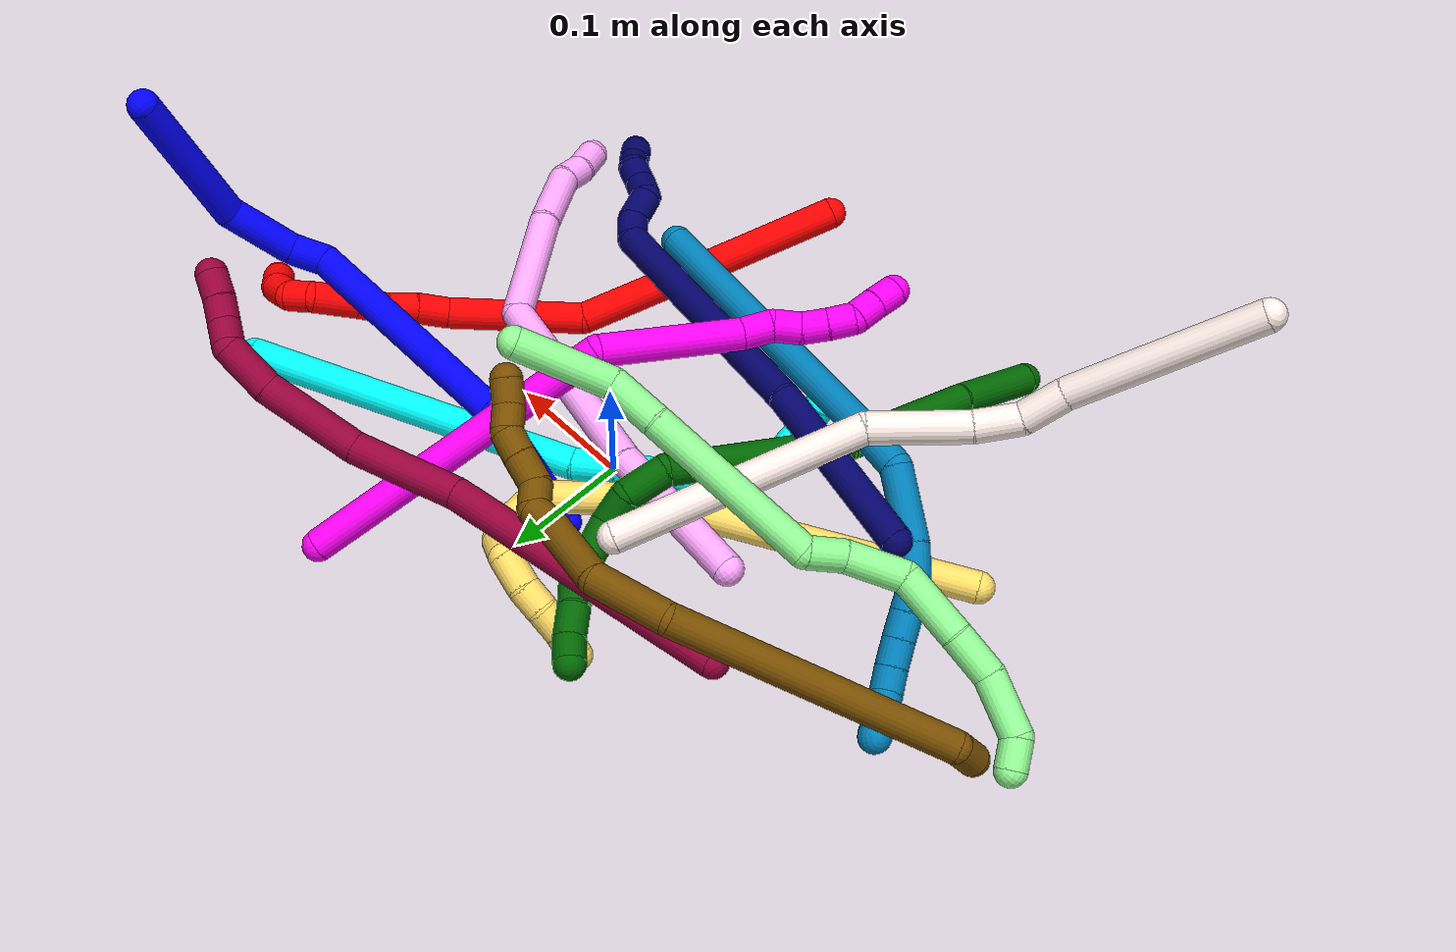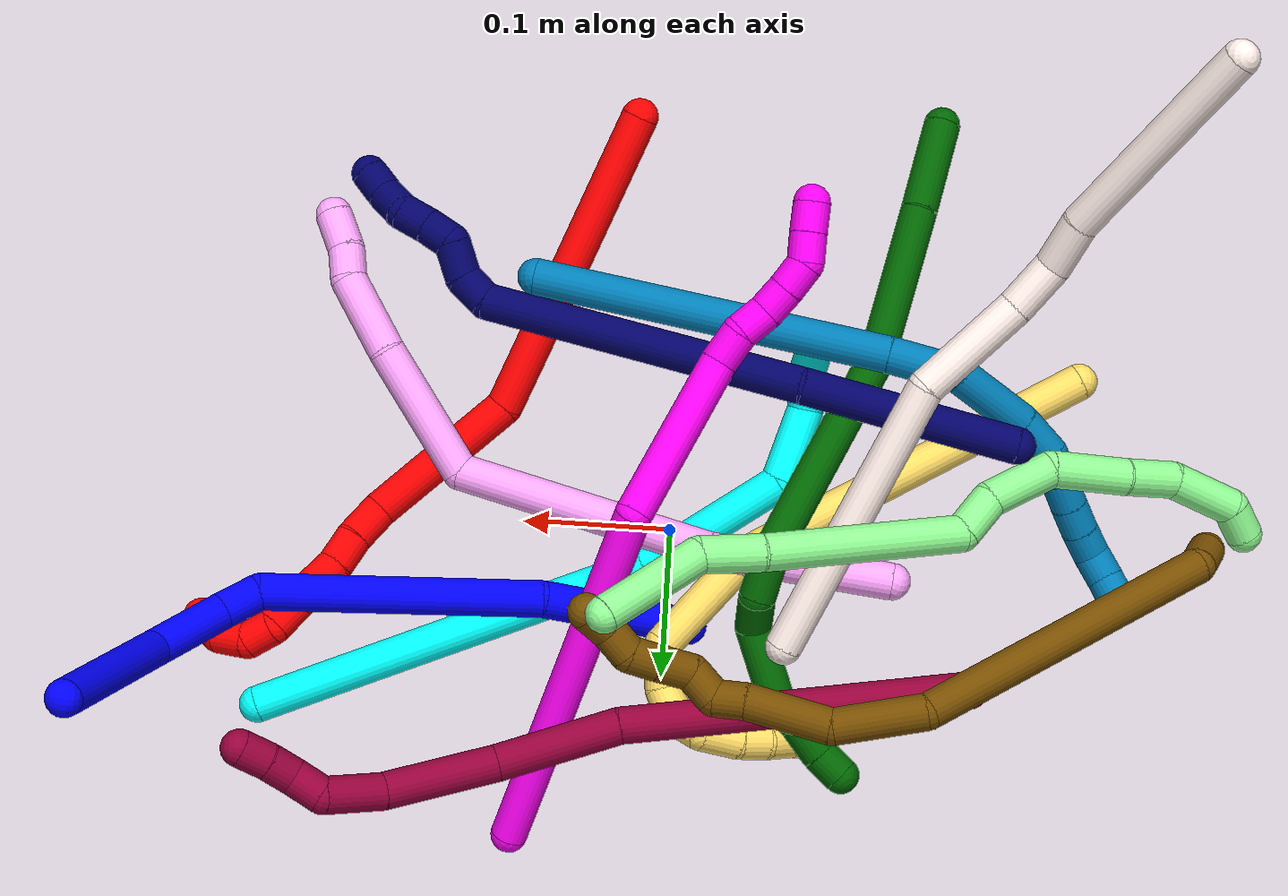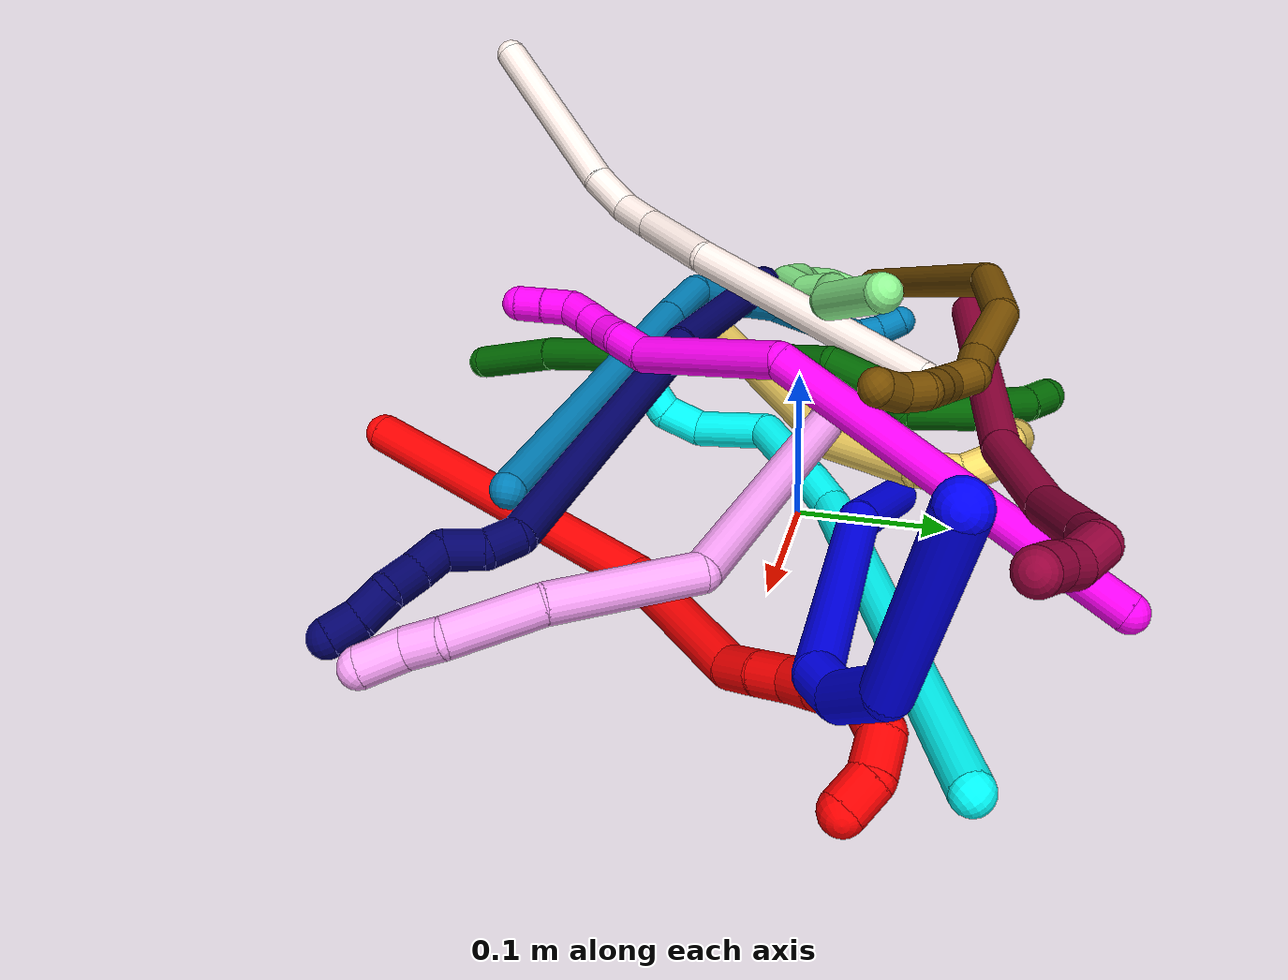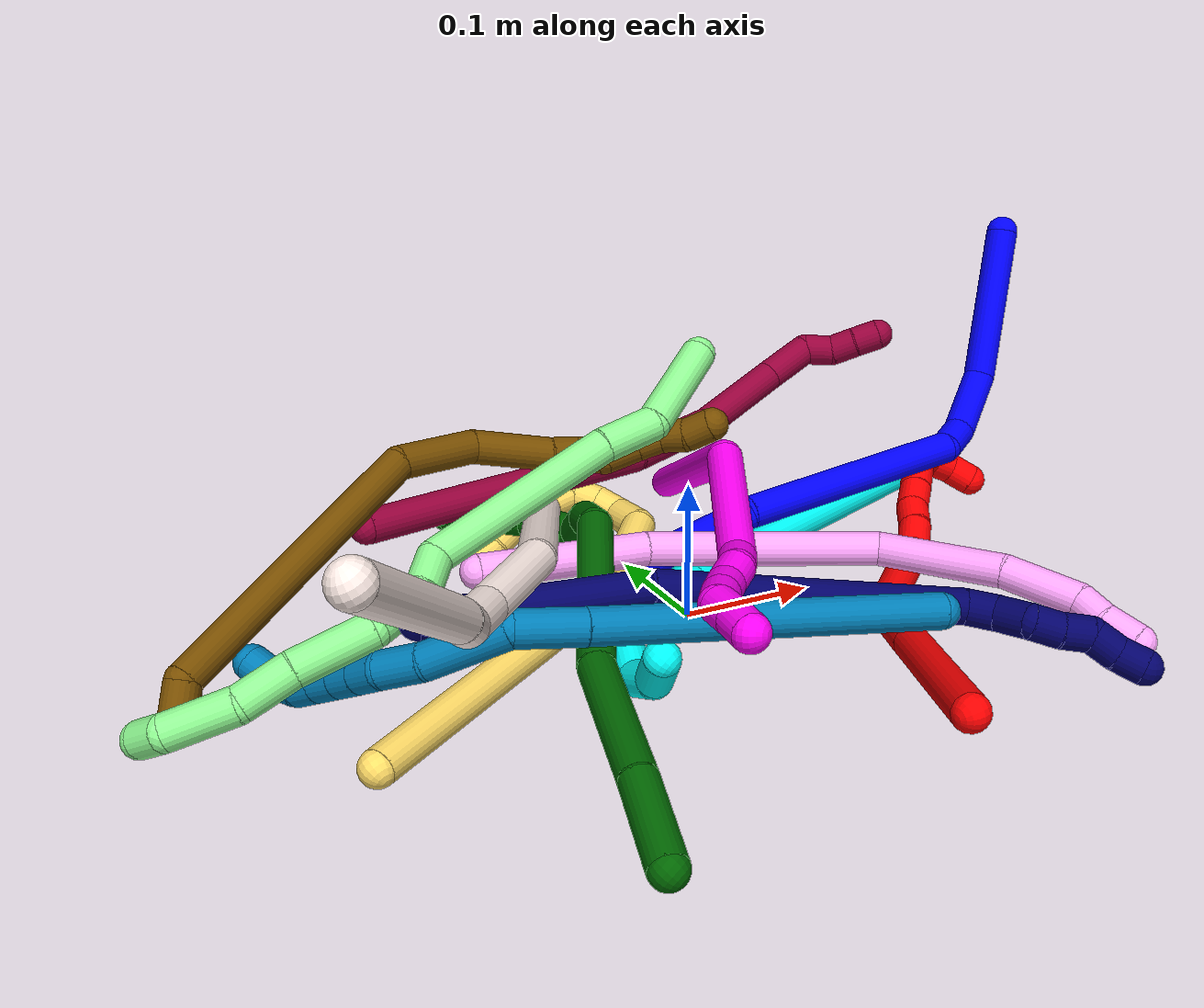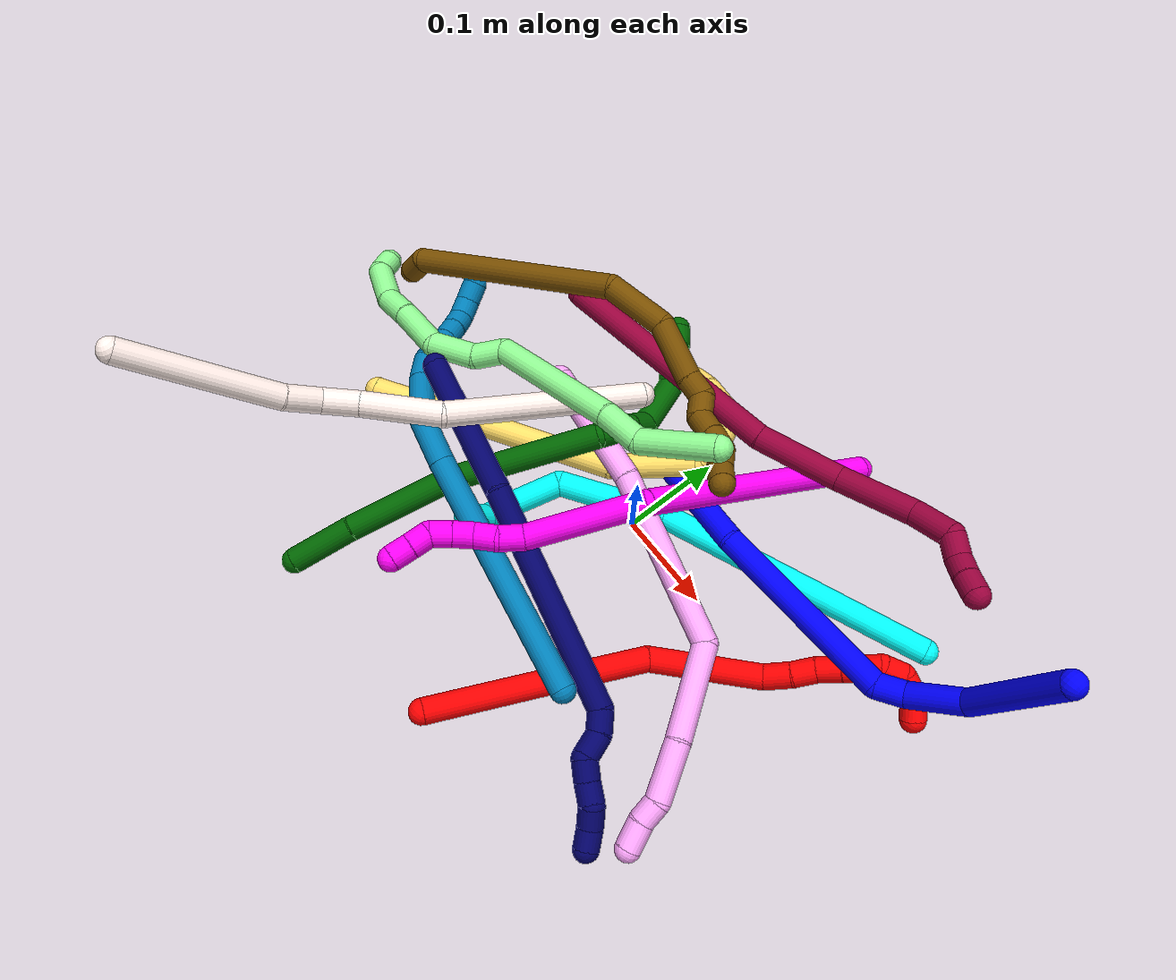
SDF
<sdf version="1.7">
 <world name="default">
  <plugin name="TubeGeneratorPlugin" filename="libtube_generator_plugin.so"/>
  <model name="photoneo_s_sensor">
   <static>1</static>
   <pose>0 0 2 1.57079 1.57079 3.14159</pose>
   <link name="link">
    <inertial><mass>0.1</mass></inertial>
    <sensor name="sensor" type="depth">
     <update_rate>30</update_rate>
     <camera>
      <horizontal_fov>1.22</horizontal_fov>
      <image><width>1920</width><height>1200</height><format>B8G8R8</format></image>
      <clip><near>0.1</near><far>4</far></clip>
      <depth_camera><output>points</output></depth_camera>
     </camera>
     <plugin name="camera_plugin" filename="libgazebo_ros_depth_camera.so">
      <baseline>0.2</baseline>
      <alwaysOn>1</alwaysOn>
      <updateRate>0.0</updateRate>
      <cameraName>camera_ir</cameraName>
      <imageTopicName>/camera/color/image_raw</imageTopicName>
      <cameraInfoTopicName>/camera/color/camera_info</cameraInfoTopicName>
      <depthImageTopicName>/camera/depth/image_raw</depthImageTopicName>
      <depthImageCameraInfoTopicName>/camera/depth/camera_info</depthImageCameraInfoTopicName>
      <pointCloudTopicName>/camera/depth/points</pointCloudTopicName>
      <frameName>fr_optical</frameName>
      <pointCloudCutoff>0.1</pointCloudCutoff>
      <pointCloudCutoffMax>2.0</pointCloudCutoffMax>
      <distortionK1>0</distortionK1>
      <distortionK2>0</distortionK2>
      <distortionK3>0</distortionK3>
      <distortionT1>0</distortionT1>
      <distortionT2>0</distortionT2>
      <CxPrime>0</CxPrime>
      <Cx>0</Cx>
      <Cy>0</Cy>
      <focalLength>0</focalLength>
      <hackBaseline>0</hackBaseline>
     </plugin>
    </sensor>
   </link>
  </model>
  <gravity>0 0 -9.8</gravity>
  <magnetic_field>6e-06 2.3e-05 -4.2e-05</magnetic_field>
  <atmosphere type="adiabatic"/>
  <physics name="default_physics" default="0" type="ode">
   <max_step_size>0.003</max_step_size>
   <real_time_factor>1</real_time_factor>
   <real_time_update_rate>1000</real_time_update_rate>
   <max_contacts>10000</max_contacts>
   <ode>
    <solver>
     <type>quick</type>
     <iters>100</iters>
     <sor>1.3</sor>
     <use_dynamic_moi_rescaling>0</use_dynamic_moi_rescaling>
    </solver>
    <constraints>
     <contact_max_correcting_vel>0</contact_max_correcting_vel>
     <contact_surface_layer>0.001</contact_surface_layer>
     <cfm>0</cfm>
     <erp>0.2</erp>
    </constraints>
   </ode>
  </physics>
  <scene><ambient>0.4 0.4 0.4 1</ambient><background>0.7 0.7 0.7 1</background><shadows>0</shadows></scene>
  <audio><device>default</device></audio>
  <spherical_coordinates>
   <surface_model>EARTH_WGS84</surface_model>
   <latitude_deg>0</latitude_deg>
   <longitude_deg>0</longitude_deg>
   <elevation>0</elevation>
   <heading_deg>0</heading_deg>
  </spherical_coordinates>
  <model name="bin">
   <static>1</static>
   <link name="bottom">
    <collision name="collision-bottom">
     <pose>0 0 -0.01 0 -0 0</pose>
     <geometry><box><size>0.8 0.6 0.02</size></box></geometry>
     <surface>
      <friction><ode><mu>100</mu><mu2>100</mu2></ode></friction>
      <contact><collide_bitmask>65535</collide_bitmask></contact>
     </surface>
    </collision>
   </link>
   <link name="west_wall">
    <collision name="collision-west_wall">
     <pose>-0.41 0 0.1 0 -0 0</pose>
     <geometry><box><size>0.02 0.6 0.2</size></box></geometry>
     <surface>
      <friction><ode><mu>100</mu><mu2>100</mu2></ode></friction>
      <contact><collide_bitmask>65535</collide_bitmask></contact>
     </surface>
    </collision>
   </link>
   <link name="east_wall">
    <collision name="collision-east_wall">
     <pose>0.41 0 0.1 0 -0 0</pose>
     <geometry><box><size>0.02 0.6 0.2</size></box></geometry>
     <surface>
      <friction><ode><mu>100</mu><mu2>100</mu2></ode></friction>
      <contact><collide_bitmask>65535</collide_bitmask></contact>
     </surface>
    </collision>
   </link>
   <link name="south_wall">
    <collision name="collision-south_wall">
     <pose>0 -0.31 0.1 0 -0 0</pose>
     <geometry><box><size>0.8 0.02 0.2</size></box></geometry>
     <surface>
      <friction><ode><mu>100</mu><mu2>100</mu2></ode></friction>
      <contact><collide_bitmask>65535</collide_bitmask></contact>
     </surface>
    </collision>
   </link>
   <link name="north_wall">
    <collision name="collision-north_wall">
     <pose>0 0.31 0.1 0 -0 0</pose>
     <geometry><box><size>0.8 0.02 0.2</size></box></geometry>
     <surface>
      <friction><ode><mu>100</mu><mu2>100</mu2></ode></friction>
      <contact><collide_bitmask>65535</collide_bitmask></contact>
     </surface>
    </collision>
   </link>
  </model>
  <model name="1">
   <static>0</static>
   <link name="1">
    <collision name="collision-cylinder-e_1_1_4">
     <pose>0.001693 -0.005132 0.052135 0.098112 0.032298 0.001586</pose>
     <geometry><cylinder><radius>0.0125</radius><length>0.104828</length></cylinder></geometry>
     <surface>
      <friction><ode><mu>1.16</mu><mu2>1.16</mu2><slip1>0</slip1><slip2>0</slip2></ode></friction>
      <contact><ode><kp>1e+06</kp><kd>1</kd><max_vel>0</max_vel><min_depth>0.001</min_depth></ode></contact>
     </surface>
    </collision>
    <visual name="visual-cylinder-e_1_1_4">
     <pose>0.001693 -0.005132 0.052135 0.098112 0.032298 0.001586</pose>
     <geometry><cylinder><radius>0.0125</radius><length>0.104828</length></cylinder></geometry>
     <material><ambient>0 0 1 1</ambient></material>
    </visual>
    <collision name="collision-cylinder-e_2_4_5">
     <pose>0.027674 -0.004273 0.194842 -0.066037 0.26146 -0.008686</pose>
     <geometry><cylinder><radius>0.0125</radius><length>0.187927</length></cylinder></geometry>
     <surface>
      <friction><ode><mu>1.16</mu><mu2>1.16</mu2><slip1>0</slip1><slip2>0</slip2></ode></friction>
      <contact><ode><kp>1e+06</kp><kd>1</kd><max_vel>0</max_vel><min_depth>0.001</min_depth></ode></contact>
     </surface>
    </collision>
    <visual name="visual-cylinder-e_2_4_5">
     <pose>0.027674 -0.004273 0.194842 -0.066037 0.26146 -0.008686</pose>
     <geometry><cylinder><radius>0.0125</radius><length>0.187927</length></cylinder></geometry>
     <material><ambient>0 0 1 1</ambient></material>
    </visual>
    <collision name="collision-cylinder-e_3_5_6">
     <pose>0.053364 0.009244 0.297232 -0.567129 0.099658 -0.029064</pose>
     <geometry><cylinder><radius>0.0125</radius><length>0.028162</length></cylinder></geometry>
     <surface>
      <friction><ode><mu>1.16</mu><mu2>1.16</mu2><slip1>0</slip1><slip2>0</slip2></ode></friction>
      <contact><ode><kp>1e+06</kp><kd>1</kd><max_vel>0</max_vel><min_depth>0.001</min_depth></ode></contact>
     </surface>
    </collision>
    <visual name="visual-cylinder-e_3_5_6">
     <pose>0.053364 0.009244 0.297232 -0.567129 0.099658 -0.029064</pose>
     <geometry><cylinder><radius>0.0125</radius><length>0.028162</length></cylinder></geometry>
     <material><ambient>0 0 1 1</ambient></material>
    </visual>
    <collision name="collision-cylinder-e_4_6_7">
     <pose>0.045604 0.030173 0.332354 -0.521902 -0.328405 0.088437</pose>
     <geometry><cylinder><radius>0.0125</radius><length>0.056804</length></cylinder></geometry>
     <surface>
      <friction><ode><mu>1.16</mu><mu2>1.16</mu2><slip1>0</slip1><slip2>0</slip2></ode></friction>
      <contact><ode><kp>1e+06</kp><kd>1</kd><max_vel>0</max_vel><min_depth>0.001</min_depth></ode></contact>
     </surface>
    </collision>
    <visual name="visual-cylinder-e_4_6_7">
     <pose>0.045604 0.030173 0.332354 -0.521902 -0.328405 0.088437</pose>
     <geometry><cylinder><radius>0.0125</radius><length>0.056804</length></cylinder></geometry>
     <material><ambient>0 0 1 1</ambient></material>
    </visual>
    <collision name="collision-cylinder-e_5_7_2">
     <pose>-0.010068 0.058386 0.392474 -0.382494 -0.864465 0.178165</pose>
     <geometry><cylinder><radius>0.0125</radius><length>0.122279</length></cylinder></geometry>
     <surface>
      <friction><ode><mu>1.16</mu><mu2>1.16</mu2><slip1>0</slip1><slip2>0</slip2></ode></friction>
      <contact><ode><kp>1e+06</kp><kd>1</kd><max_vel>0</max_vel><min_depth>0.001</min_depth></ode></contact>
     </surface>
    </collision>
    <visual name="visual-cylinder-e_5_7_2">
     <pose>-0.010068 0.058386 0.392474 -0.382494 -0.864465 0.178165</pose>
     <geometry><cylinder><radius>0.0125</radius><length>0.122279</length></cylinder></geometry>
     <material><ambient>0 0 1 1</ambient></material>
    </visual>
    <collision name="collision-sphere-2">
     <pose>-0.05658 0.073197 0.429289 0 -0 0</pose>
     <geometry><sphere><radius>0.0125</radius></sphere></geometry>
     <surface>
      <friction><ode><mu>1.16</mu><mu2>1.16</mu2><slip1>0</slip1><slip2>0</slip2></ode></friction>
      <contact><ode><kp>1e+06</kp><kd>1</kd><max_vel>0</max_vel><min_depth>0.001</min_depth></ode></contact>
     </surface>
    </collision>
    <visual name="visual-sphere-2">
     <pose>-0.05658 0.073197 0.429289 0 -0 0</pose>
     <geometry><sphere><radius>0.0125</radius></sphere></geometry>
     <material><ambient>0 0 1 1</ambient></material>
    </visual>
    <collision name="collision-sphere-7">
     <pose>0.036443 0.043576 0.355659 0 -0 0</pose>
     <geometry><sphere><radius>0.0125</radius></sphere></geometry>
     <surface>
      <friction><ode><mu>1.16</mu><mu2>1.16</mu2><slip1>0</slip1><slip2>0</slip2></ode></friction>
      <contact><ode><kp>1e+06</kp><kd>1</kd><max_vel>0</max_vel><min_depth>0.001</min_depth></ode></contact>
     </surface>
    </collision>
    <visual name="visual-sphere-7">
     <pose>0.036443 0.043576 0.355659 0 -0 0</pose>
     <geometry><sphere><radius>0.0125</radius></sphere></geometry>
     <material><ambient>0 0 1 1</ambient></material>
    </visual>
    <collision name="collision-sphere-6">
     <pose>0.054765 0.01677 0.309049 0 -0 0</pose>
     <geometry><sphere><radius>0.0125</radius></sphere></geometry>
     <surface>
      <friction><ode><mu>1.16</mu><mu2>1.16</mu2><slip1>0</slip1><slip2>0</slip2></ode></friction>
      <contact><ode><kp>1e+06</kp><kd>1</kd><max_vel>0</max_vel><min_depth>0.001</min_depth></ode></contact>
     </surface>
    </collision>
    <visual name="visual-sphere-6">
     <pose>0.054765 0.01677 0.309049 0 -0 0</pose>
     <geometry><sphere><radius>0.0125</radius></sphere></geometry>
     <material><ambient>0 0 1 1</ambient></material>
    </visual>
    <collision name="collision-sphere-5">
     <pose>0.051963 0.001717 0.285414 0 -0 0</pose>
     <geometry><sphere><radius>0.0125</radius></sphere></geometry>
     <surface>
      <friction><ode><mu>1.16</mu><mu2>1.16</mu2><slip1>0</slip1><slip2>0</slip2></ode></friction>
      <contact><ode><kp>1e+06</kp><kd>1</kd><max_vel>0</max_vel><min_depth>0.001</min_depth></ode></contact>
     </surface>
    </collision>
    <visual name="visual-sphere-5">
     <pose>0.051963 0.001717 0.285414 0 -0 0</pose>
     <geometry><sphere><radius>0.0125</radius></sphere></geometry>
     <material><ambient>0 0 1 1</ambient></material>
    </visual>
    <collision name="collision-sphere-1">
     <geometry><sphere><radius>0.0125</radius></sphere></geometry>
     <surface>
      <friction><ode><mu>1.16</mu><mu2>1.16</mu2><slip1>0</slip1><slip2>0</slip2></ode></friction>
      <contact><ode><kp>1e+06</kp><kd>1</kd><max_vel>0</max_vel><min_depth>0.001</min_depth></ode></contact>
     </surface>
    </collision>
    <visual name="visual-sphere-1">
     <geometry><sphere><radius>0.0125</radius></sphere></geometry>
     <material><ambient>0 0 1 1</ambient></material>
    </visual>
    <collision name="collision-sphere-4">
     <pose>0.003385 -0.010263 0.10427 0 -0 0</pose>
     <geometry><sphere><radius>0.0125</radius></sphere></geometry>
     <surface>
      <friction><ode><mu>1.16</mu><mu2>1.16</mu2><slip1>0</slip1><slip2>0</slip2></ode></friction>
      <contact><ode><kp>1e+06</kp><kd>1</kd><max_vel>0</max_vel><min_depth>0.001</min_depth></ode></contact>
     </surface>
    </collision>
    <visual name="visual-sphere-4">
     <pose>0.003385 -0.010263 0.10427 0 -0 0</pose>
     <geometry><sphere><radius>0.0125</radius></sphere></geometry>
     <material><ambient>0 0 1 1</ambient></material>
    </visual>
    <inertial>
     <pose>0.016481 0.015545 0.234644 0 -0 0</pose>
     <mass>0.5</mass>
     <inertia>
      <ixx>0.000772</ixx>
      <ixy>0</ixy>
      <ixz>0</ixz>
      <iyy>0.000849</iyy>
      <iyz>0</iyz>
      <izz>-6.3e-05</izz>
     </inertia>
    </inertial>
   </link>
   <pose>-0.016242 0.064601 0.011484 -0.009917 1.20515 -0.042322</pose>
  </model>
  <model name="2">
   <static>0</static>
   <link name="2">
    <collision name="collision-cylinder-e_1_1_4">
     <pose>0.049173 0.0345 0.031501 -0.830805 0.811004 -0.374266</pose>
     <geometry><cylinder><radius>0.0125</radius><length>0.135655</length></cylinder></geometry>
     <surface>
      <friction><ode><mu>1.16</mu><mu2>1.16</mu2><slip1>0</slip1><slip2>0</slip2></ode></friction>
      <contact><ode><kp>1e+06</kp><kd>1</kd><max_vel>0</max_vel><min_depth>0.001</min_depth></ode></contact>
     </surface>
    </collision>
    <visual name="visual-cylinder-e_1_1_4">
     <pose>0.049173 0.0345 0.031501 -0.830805 0.811004 -0.374266</pose>
     <geometry><cylinder><radius>0.0125</radius><length>0.135655</length></cylinder></geometry>
     <material><ambient>1 0 0 1</ambient></material>
    </visual>
    <collision name="collision-cylinder-e_2_4_5">
     <pose>0.127702 0.08966 0.082113 -0.824338 0.806451 -0.368793</pose>
     <geometry><cylinder><radius>0.0125</radius><length>0.081336</length></cylinder></geometry>
     <surface>
      <friction><ode><mu>1.16</mu><mu2>1.16</mu2><slip1>0</slip1><slip2>0</slip2></ode></friction>
      <contact><ode><kp>1e+06</kp><kd>1</kd><max_vel>0</max_vel><min_depth>0.001</min_depth></ode></contact>
     </surface>
    </collision>
    <visual name="visual-cylinder-e_2_4_5">
     <pose>0.127702 0.08966 0.082113 -0.824338 0.806451 -0.368793</pose>
     <geometry><cylinder><radius>0.0125</radius><length>0.081336</length></cylinder></geometry>
     <material><ambient>1 0 0 1</ambient></material>
    </visual>
    <collision name="collision-cylinder-e_3_5_6">
     <pose>0.18128 0.131557 0.145326 -0.448755 0.459528 -0.106658</pose>
     <geometry><cylinder><radius>0.0125</radius><length>0.109227</length></cylinder></geometry>
     <surface>
      <friction><ode><mu>1.16</mu><mu2>1.16</mu2><slip1>0</slip1><slip2>0</slip2></ode></friction>
      <contact><ode><kp>1e+06</kp><kd>1</kd><max_vel>0</max_vel><min_depth>0.001</min_depth></ode></contact>
     </surface>
    </collision>
    <visual name="visual-cylinder-e_3_5_6">
     <pose>0.18128 0.131557 0.145326 -0.448755 0.459528 -0.106658</pose>
     <geometry><cylinder><radius>0.0125</radius><length>0.109227</length></cylinder></geometry>
     <material><ambient>1 0 0 1</ambient></material>
    </visual>
    <collision name="collision-cylinder-e_4_6_7">
     <pose>0.208381 0.162078 0.198923 -0.77422 0.213452 -0.087296</pose>
     <geometry><cylinder><radius>0.0125</radius><length>0.027178</length></cylinder></geometry>
     <surface>
      <friction><ode><mu>1.16</mu><mu2>1.16</mu2><slip1>0</slip1><slip2>0</slip2></ode></friction>
      <contact><ode><kp>1e+06</kp><kd>1</kd><max_vel>0</max_vel><min_depth>0.001</min_depth></ode></contact>
     </surface>
    </collision>
    <visual name="visual-cylinder-e_4_6_7">
     <pose>0.208381 0.162078 0.198923 -0.77422 0.213452 -0.087296</pose>
     <geometry><cylinder><radius>0.0125</radius><length>0.027178</length></cylinder></geometry>
     <material><ambient>1 0 0 1</ambient></material>
    </visual>
    <collision name="collision-cylinder-e_5_7_8">
     <pose>0.215204 0.179783 0.215359 -0.881334 0.346852 -0.16486</pose>
     <geometry><cylinder><radius>0.0125</radius><length>0.023206</length></cylinder></geometry>
     <surface>
      <friction><ode><mu>1.16</mu><mu2>1.16</mu2><slip1>0</slip1><slip2>0</slip2></ode></friction>
      <contact><ode><kp>1e+06</kp><kd>1</kd><max_vel>0</max_vel><min_depth>0.001</min_depth></ode></contact>
     </surface>
    </collision>
    <visual name="visual-cylinder-e_5_7_8">
     <pose>0.215204 0.179783 0.215359 -0.881334 0.346852 -0.16486</pose>
     <geometry><cylinder><radius>0.0125</radius><length>0.023206</length></cylinder></geometry>
     <material><ambient>1 0 0 1</ambient></material>
    </visual>
    <collision name="collision-cylinder-e_6_8_9">
     <pose>0.221498 0.195683 0.230981 -0.71126 0.202257 -0.075344</pose>
     <geometry><cylinder><radius>0.0125</radius><length>0.023395</length></cylinder></geometry>
     <surface>
      <friction><ode><mu>1.16</mu><mu2>1.16</mu2><slip1>0</slip1><slip2>0</slip2></ode></friction>
      <contact><ode><kp>1e+06</kp><kd>1</kd><max_vel>0</max_vel><min_depth>0.001</min_depth></ode></contact>
     </surface>
    </collision>
    <visual name="visual-cylinder-e_6_8_9">
     <pose>0.221498 0.195683 0.230981 -0.71126 0.202257 -0.075344</pose>
     <geometry><cylinder><radius>0.0125</radius><length>0.023395</length></cylinder></geometry>
     <material><ambient>1 0 0 1</ambient></material>
    </visual>
    <collision name="collision-cylinder-e_7_9_10">
     <pose>0.228366 0.214833 0.252642 -0.732287 0.253301 -0.097569</pose>
     <geometry><cylinder><radius>0.0125</radius><length>0.036062</length></cylinder></geometry>
     <surface>
      <friction><ode><mu>1.16</mu><mu2>1.16</mu2><slip1>0</slip1><slip2>0</slip2></ode></friction>
      <contact><ode><kp>1e+06</kp><kd>1</kd><max_vel>0</max_vel><min_depth>0.001</min_depth></ode></contact>
     </surface>
    </collision>
    <visual name="visual-cylinder-e_7_9_10">
     <pose>0.228366 0.214833 0.252642 -0.732287 0.253301 -0.097569</pose>
     <geometry><cylinder><radius>0.0125</radius><length>0.036062</length></cylinder></geometry>
     <material><ambient>1 0 0 1</ambient></material>
    </visual>
    <collision name="collision-cylinder-e_8_10_11">
     <pose>0.237842 0.22764 0.274408 -0.128709 0.510162 -0.033605</pose>
     <geometry><cylinder><radius>0.0125</radius><length>0.020302</length></cylinder></geometry>
     <surface>
      <friction><ode><mu>1.16</mu><mu2>1.16</mu2><slip1>0</slip1><slip2>0</slip2></ode></friction>
      <contact><ode><kp>1e+06</kp><kd>1</kd><max_vel>0</max_vel><min_depth>0.001</min_depth></ode></contact>
     </surface>
    </collision>
    <visual name="visual-cylinder-e_8_10_11">
     <pose>0.237842 0.22764 0.274408 -0.128709 0.510162 -0.033605</pose>
     <geometry><cylinder><radius>0.0125</radius><length>0.020302</length></cylinder></geometry>
     <material><ambient>1 0 0 1</ambient></material>
    </visual>
    <collision name="collision-cylinder-e_9_11_12">
     <pose>0.245862 0.22302 0.292687 0.545143 0.269212 0.075674</pose>
     <geometry><cylinder><radius>0.0125</radius><length>0.023036</length></cylinder></geometry>
     <surface>
      <friction><ode><mu>1.16</mu><mu2>1.16</mu2><slip1>0</slip1><slip2>0</slip2></ode></friction>
      <contact><ode><kp>1e+06</kp><kd>1</kd><max_vel>0</max_vel><min_depth>0.001</min_depth></ode></contact>
     </surface>
    </collision>
    <visual name="visual-cylinder-e_9_11_12">
     <pose>0.245862 0.22302 0.292687 0.545143 0.269212 0.075674</pose>
     <geometry><cylinder><radius>0.0125</radius><length>0.023036</length></cylinder></geometry>
     <material><ambient>1 0 0 1</ambient></material>
    </visual>
    <collision name="collision-cylinder-e_10_12_2">
     <pose>0.248703 0.208769 0.308007 0.96956 -0.021564 -0.011358</pose>
     <geometry><cylinder><radius>0.0125</radius><length>0.020605</length></cylinder></geometry>
     <surface>
      <friction><ode><mu>1.16</mu><mu2>1.16</mu2><slip1>0</slip1><slip2>0</slip2></ode></friction>
      <contact><ode><kp>1e+06</kp><kd>1</kd><max_vel>0</max_vel><min_depth>0.001</min_depth></ode></contact>
     </surface>
    </collision>
    <visual name="visual-cylinder-e_10_12_2">
     <pose>0.248703 0.208769 0.308007 0.96956 -0.021564 -0.011358</pose>
     <geometry><cylinder><radius>0.0125</radius><length>0.020605</length></cylinder></geometry>
     <material><ambient>1 0 0 1</ambient></material>
    </visual>
    <collision name="collision-sphere-2">
     <pose>0.248481 0.200275 0.313833 0 -0 0</pose>
     <geometry><sphere><radius>0.0125</radius></sphere></geometry>
     <surface>
      <friction><ode><mu>1.16</mu><mu2>1.16</mu2><slip1>0</slip1><slip2>0</slip2></ode></friction>
      <contact><ode><kp>1e+06</kp><kd>1</kd><max_vel>0</max_vel><min_depth>0.001</min_depth></ode></contact>
     </surface>
    </collision>
    <visual name="visual-sphere-2">
     <pose>0.248481 0.200275 0.313833 0 -0 0</pose>
     <geometry><sphere><radius>0.0125</radius></sphere></geometry>
     <material><ambient>1 0 0 1</ambient></material>
    </visual>
    <collision name="collision-sphere-12">
     <pose>0.248925 0.217263 0.30218 0 -0 0</pose>
     <geometry><sphere><radius>0.0125</radius></sphere></geometry>
     <surface>
      <friction><ode><mu>1.16</mu><mu2>1.16</mu2><slip1>0</slip1><slip2>0</slip2></ode></friction>
      <contact><ode><kp>1e+06</kp><kd>1</kd><max_vel>0</max_vel><min_depth>0.001</min_depth></ode></contact>
     </surface>
    </collision>
    <visual name="visual-sphere-12">
     <pose>0.248925 0.217263 0.30218 0 -0 0</pose>
     <geometry><sphere><radius>0.0125</radius></sphere></geometry>
     <material><ambient>1 0 0 1</ambient></material>
    </visual>
    <collision name="collision-sphere-11">
     <pose>0.242799 0.228777 0.283193 0 -0 0</pose>
     <geometry><sphere><radius>0.0125</radius></sphere></geometry>
     <surface>
      <friction><ode><mu>1.16</mu><mu2>1.16</mu2><slip1>0</slip1><slip2>0</slip2></ode></friction>
      <contact><ode><kp>1e+06</kp><kd>1</kd><max_vel>0</max_vel><min_depth>0.001</min_depth></ode></contact>
     </surface>
    </collision>
    <visual name="visual-sphere-11">
     <pose>0.242799 0.228777 0.283193 0 -0 0</pose>
     <geometry><sphere><radius>0.0125</radius></sphere></geometry>
     <material><ambient>1 0 0 1</ambient></material>
    </visual>
    <collision name="collision-sphere-10">
     <pose>0.232885 0.226503 0.265623 0 -0 0</pose>
     <geometry><sphere><radius>0.0125</radius></sphere></geometry>
     <surface>
      <friction><ode><mu>1.16</mu><mu2>1.16</mu2><slip1>0</slip1><slip2>0</slip2></ode></friction>
      <contact><ode><kp>1e+06</kp><kd>1</kd><max_vel>0</max_vel><min_depth>0.001</min_depth></ode></contact>
     </surface>
    </collision>
    <visual name="visual-sphere-10">
     <pose>0.232885 0.226503 0.265623 0 -0 0</pose>
     <geometry><sphere><radius>0.0125</radius></sphere></geometry>
     <material><ambient>1 0 0 1</ambient></material>
    </visual>
    <collision name="collision-sphere-9">
     <pose>0.223848 0.203163 0.239662 0 -0 0</pose>
     <geometry><sphere><radius>0.0125</radius></sphere></geometry>
     <surface>
      <friction><ode><mu>1.16</mu><mu2>1.16</mu2><slip1>0</slip1><slip2>0</slip2></ode></friction>
      <contact><ode><kp>1e+06</kp><kd>1</kd><max_vel>0</max_vel><min_depth>0.001</min_depth></ode></contact>
     </surface>
    </collision>
    <visual name="visual-sphere-9">
     <pose>0.223848 0.203163 0.239662 0 -0 0</pose>
     <geometry><sphere><radius>0.0125</radius></sphere></geometry>
     <material><ambient>1 0 0 1</ambient></material>
    </visual>
    <collision name="collision-sphere-4">
     <pose>0.098347 0.068999 0.063001 0 -0 0</pose>
     <geometry><sphere><radius>0.0125</radius></sphere></geometry>
     <surface>
      <friction><ode><mu>1.16</mu><mu2>1.16</mu2><slip1>0</slip1><slip2>0</slip2></ode></friction>
      <contact><ode><kp>1e+06</kp><kd>1</kd><max_vel>0</max_vel><min_depth>0.001</min_depth></ode></contact>
     </surface>
    </collision>
    <visual name="visual-sphere-4">
     <pose>0.098347 0.068999 0.063001 0 -0 0</pose>
     <geometry><sphere><radius>0.0125</radius></sphere></geometry>
     <material><ambient>1 0 0 1</ambient></material>
    </visual>
    <collision name="collision-sphere-1">
     <geometry><sphere><radius>0.0125</radius></sphere></geometry>
     <surface>
      <friction><ode><mu>1.16</mu><mu2>1.16</mu2><slip1>0</slip1><slip2>0</slip2></ode></friction>
      <contact><ode><kp>1e+06</kp><kd>1</kd><max_vel>0</max_vel><min_depth>0.001</min_depth></ode></contact>
     </surface>
    </collision>
    <visual name="visual-sphere-1">
     <geometry><sphere><radius>0.0125</radius></sphere></geometry>
     <material><ambient>1 0 0 1</ambient></material>
    </visual>
    <collision name="collision-sphere-8">
     <pose>0.219148 0.188202 0.222301 0 -0 0</pose>
     <geometry><sphere><radius>0.0125</radius></sphere></geometry>
     <surface>
      <friction><ode><mu>1.16</mu><mu2>1.16</mu2><slip1>0</slip1><slip2>0</slip2></ode></friction>
      <contact><ode><kp>1e+06</kp><kd>1</kd><max_vel>0</max_vel><min_depth>0.001</min_depth></ode></contact>
     </surface>
    </collision>
    <visual name="visual-sphere-8">
     <pose>0.219148 0.188202 0.222301 0 -0 0</pose>
     <geometry><sphere><radius>0.0125</radius></sphere></geometry>
     <material><ambient>1 0 0 1</ambient></material>
    </visual>
    <collision name="collision-sphere-5">
     <pose>0.157058 0.110321 0.101224 0 -0 0</pose>
     <geometry><sphere><radius>0.0125</radius></sphere></geometry>
     <surface>
      <friction><ode><mu>1.16</mu><mu2>1.16</mu2><slip1>0</slip1><slip2>0</slip2></ode></friction>
      <contact><ode><kp>1e+06</kp><kd>1</kd><max_vel>0</max_vel><min_depth>0.001</min_depth></ode></contact>
     </surface>
    </collision>
    <visual name="visual-sphere-5">
     <pose>0.157058 0.110321 0.101224 0 -0 0</pose>
     <geometry><sphere><radius>0.0125</radius></sphere></geometry>
     <material><ambient>1 0 0 1</ambient></material>
    </visual>
    <collision name="collision-sphere-6">
     <pose>0.205502 0.152793 0.189427 0 -0 0</pose>
     <geometry><sphere><radius>0.0125</radius></sphere></geometry>
     <surface>
      <friction><ode><mu>1.16</mu><mu2>1.16</mu2><slip1>0</slip1><slip2>0</slip2></ode></friction>
      <contact><ode><kp>1e+06</kp><kd>1</kd><max_vel>0</max_vel><min_depth>0.001</min_depth></ode></contact>
     </surface>
    </collision>
    <visual name="visual-sphere-6">
     <pose>0.205502 0.152793 0.189427 0 -0 0</pose>
     <geometry><sphere><radius>0.0125</radius></sphere></geometry>
     <material><ambient>1 0 0 1</ambient></material>
    </visual>
    <collision name="collision-sphere-7">
     <pose>0.21126 0.171364 0.208418 0 -0 0</pose>
     <geometry><sphere><radius>0.0125</radius></sphere></geometry>
     <surface>
      <friction><ode><mu>1.16</mu><mu2>1.16</mu2><slip1>0</slip1><slip2>0</slip2></ode></friction>
      <contact><ode><kp>1e+06</kp><kd>1</kd><max_vel>0</max_vel><min_depth>0.001</min_depth></ode></contact>
     </surface>
    </collision>
    <visual name="visual-sphere-7">
     <pose>0.21126 0.171364 0.208418 0 -0 0</pose>
     <geometry><sphere><radius>0.0125</radius></sphere></geometry>
     <material><ambient>1 0 0 1</ambient></material>
    </visual>
    <inertial>
     <pose>0.153099 0.12261 0.140807 0 -0 0</pose>
     <mass>0.5</mass>
     <inertia>
      <ixx>0.000226</ixx>
      <ixy>0</ixy>
      <ixz>0</ixz>
      <iyy>0.00027</iyy>
      <iyz>0</iyz>
      <izz>-0.000402</izz>
     </inertia>
    </inertial>
   </link>
   <pose>0.03639 -0.274839 0.047328 1.4235 0.848298 1.5866</pose>
  </model>
  <model name="3">
   <static>0</static>
   <link name="3">
    <collision name="collision-cylinder-e_1_1_4">
     <pose>-0.116861 -0.06996 0.028282 1.18663 -0.997431 -0.703978</pose>
     <geometry><cylinder><radius>0.0125</radius><length>0.278215</length></cylinder></geometry>
     <surface>
      <friction><ode><mu>1.16</mu><mu2>1.16</mu2><slip1>0</slip1><slip2>0</slip2></ode></friction>
      <contact><ode><kp>1e+06</kp><kd>1</kd><max_vel>0</max_vel><min_depth>0.001</min_depth></ode></contact>
     </surface>
    </collision>
    <visual name="visual-cylinder-e_1_1_4">
     <pose>-0.116861 -0.06996 0.028282 1.18663 -0.997431 -0.703978</pose>
     <geometry><cylinder><radius>0.0125</radius><length>0.278215</length></cylinder></geometry>
     <material><ambient>0.003922 1 0.996078 1</ambient></material>
    </visual>
    <collision name="collision-cylinder-e_2_4_5">
     <pose>-0.245951 -0.150933 0.057922 1.44806 -0.833896 -0.746554</pose>
     <geometry><cylinder><radius>0.0125</radius><length>0.033025</length></cylinder></geometry>
     <surface>
      <friction><ode><mu>1.16</mu><mu2>1.16</mu2><slip1>0</slip1><slip2>0</slip2></ode></friction>
      <contact><ode><kp>1e+06</kp><kd>1</kd><max_vel>0</max_vel><min_depth>0.001</min_depth></ode></contact>
     </surface>
    </collision>
    <visual name="visual-cylinder-e_2_4_5">
     <pose>-0.245951 -0.150933 0.057922 1.44806 -0.833896 -0.746554</pose>
     <geometry><cylinder><radius>0.0125</radius><length>0.033025</length></cylinder></geometry>
     <material><ambient>0.003922 1 0.996078 1</ambient></material>
    </visual>
    <collision name="collision-cylinder-e_3_5_6">
     <pose>-0.286999 -0.185154 0.0606 1.51399 -0.89206 -0.848617</pose>
     <geometry><cylinder><radius>0.0125</radius><length>0.074051</length></cylinder></geometry>
     <surface>
      <friction><ode><mu>1.16</mu><mu2>1.16</mu2><slip1>0</slip1><slip2>0</slip2></ode></friction>
      <contact><ode><kp>1e+06</kp><kd>1</kd><max_vel>0</max_vel><min_depth>0.001</min_depth></ode></contact>
     </surface>
    </collision>
    <visual name="visual-cylinder-e_3_5_6">
     <pose>-0.286999 -0.185154 0.0606 1.51399 -0.89206 -0.848617</pose>
     <geometry><cylinder><radius>0.0125</radius><length>0.074051</length></cylinder></geometry>
     <material><ambient>0.003922 1 0.996078 1</ambient></material>
    </visual>
    <collision name="collision-cylinder-e_4_6_7">
     <pose>-0.330654 -0.224596 0.04533 2.367 -0.568701 -1.24347</pose>
     <geometry><cylinder><radius>0.0125</radius><length>0.055096</length></cylinder></geometry>
     <surface>
      <friction><ode><mu>1.16</mu><mu2>1.16</mu2><slip1>0</slip1><slip2>0</slip2></ode></friction>
      <contact><ode><kp>1e+06</kp><kd>1</kd><max_vel>0</max_vel><min_depth>0.001</min_depth></ode></contact>
     </surface>
    </collision>
    <visual name="visual-cylinder-e_4_6_7">
     <pose>-0.330654 -0.224596 0.04533 2.367 -0.568701 -1.24347</pose>
     <geometry><cylinder><radius>0.0125</radius><length>0.055096</length></cylinder></geometry>
     <material><ambient>0.003922 1 0.996078 1</ambient></material>
    </visual>
    <collision name="collision-cylinder-e_5_7_8">
     <pose>-0.345427 -0.253949 0.02257 2.01042 0.004339 0.006835</pose>
     <geometry><cylinder><radius>0.0125</radius><length>0.028992</length></cylinder></geometry>
     <surface>
      <friction><ode><mu>1.16</mu><mu2>1.16</mu2><slip1>0</slip1><slip2>0</slip2></ode></friction>
      <contact><ode><kp>1e+06</kp><kd>1</kd><max_vel>0</max_vel><min_depth>0.001</min_depth></ode></contact>
     </surface>
    </collision>
    <visual name="visual-cylinder-e_5_7_8">
     <pose>-0.345427 -0.253949 0.02257 2.01042 0.004339 0.006835</pose>
     <geometry><cylinder><radius>0.0125</radius><length>0.028992</length></cylinder></geometry>
     <material><ambient>0.003922 1 0.996078 1</ambient></material>
    </visual>
    <collision name="collision-cylinder-e_6_8_2">
     <pose>-0.342583 -0.282064 0.017723 1.48285 0.182646 0.167325</pose>
     <geometry><cylinder><radius>0.0125</radius><length>0.030621</length></cylinder></geometry>
     <surface>
      <friction><ode><mu>1.16</mu><mu2>1.16</mu2><slip1>0</slip1><slip2>0</slip2></ode></friction>
      <contact><ode><kp>1e+06</kp><kd>1</kd><max_vel>0</max_vel><min_depth>0.001</min_depth></ode></contact>
     </surface>
    </collision>
    <visual name="visual-cylinder-e_6_8_2">
     <pose>-0.342583 -0.282064 0.017723 1.48285 0.182646 0.167325</pose>
     <geometry><cylinder><radius>0.0125</radius><length>0.030621</length></cylinder></geometry>
     <material><ambient>0.003922 1 0.996078 1</ambient></material>
    </visual>
    <collision name="collision-sphere-2">
     <pose>-0.339803 -0.297061 0.019046 0 -0 0</pose>
     <geometry><sphere><radius>0.0125</radius></sphere></geometry>
     <surface>
      <friction><ode><mu>1.16</mu><mu2>1.16</mu2><slip1>0</slip1><slip2>0</slip2></ode></friction>
      <contact><ode><kp>1e+06</kp><kd>1</kd><max_vel>0</max_vel><min_depth>0.001</min_depth></ode></contact>
     </surface>
    </collision>
    <visual name="visual-sphere-2">
     <pose>-0.339803 -0.297061 0.019046 0 -0 0</pose>
     <geometry><sphere><radius>0.0125</radius></sphere></geometry>
     <material><ambient>0.003922 1 0.996078 1</ambient></material>
    </visual>
    <collision name="collision-sphere-4">
     <pose>-0.233723 -0.13992 0.056563 0 -0 0</pose>
     <geometry><sphere><radius>0.0125</radius></sphere></geometry>
     <surface>
      <friction><ode><mu>1.16</mu><mu2>1.16</mu2><slip1>0</slip1><slip2>0</slip2></ode></friction>
      <contact><ode><kp>1e+06</kp><kd>1</kd><max_vel>0</max_vel><min_depth>0.001</min_depth></ode></contact>
     </surface>
    </collision>
    <visual name="visual-sphere-4">
     <pose>-0.233723 -0.13992 0.056563 0 -0 0</pose>
     <geometry><sphere><radius>0.0125</radius></sphere></geometry>
     <material><ambient>0.003922 1 0.996078 1</ambient></material>
    </visual>
    <collision name="collision-sphere-1">
     <geometry><sphere><radius>0.0125</radius></sphere></geometry>
     <surface>
      <friction><ode><mu>1.16</mu><mu2>1.16</mu2><slip1>0</slip1><slip2>0</slip2></ode></friction>
      <contact><ode><kp>1e+06</kp><kd>1</kd><max_vel>0</max_vel><min_depth>0.001</min_depth></ode></contact>
     </surface>
    </collision>
    <visual name="visual-sphere-1">
     <geometry><sphere><radius>0.0125</radius></sphere></geometry>
     <material><ambient>0.003922 1 0.996078 1</ambient></material>
    </visual>
    <collision name="collision-sphere-8">
     <pose>-0.345364 -0.267067 0.016401 0 -0 0</pose>
     <geometry><sphere><radius>0.0125</radius></sphere></geometry>
     <surface>
      <friction><ode><mu>1.16</mu><mu2>1.16</mu2><slip1>0</slip1><slip2>0</slip2></ode></friction>
      <contact><ode><kp>1e+06</kp><kd>1</kd><max_vel>0</max_vel><min_depth>0.001</min_depth></ode></contact>
     </surface>
    </collision>
    <visual name="visual-sphere-8">
     <pose>-0.345364 -0.267067 0.016401 0 -0 0</pose>
     <geometry><sphere><radius>0.0125</radius></sphere></geometry>
     <material><ambient>0.003922 1 0.996078 1</ambient></material>
    </visual>
    <collision name="collision-sphere-5">
     <pose>-0.25818 -0.161946 0.05928 0 -0 0</pose>
     <geometry><sphere><radius>0.0125</radius></sphere></geometry>
     <surface>
      <friction><ode><mu>1.16</mu><mu2>1.16</mu2><slip1>0</slip1><slip2>0</slip2></ode></friction>
      <contact><ode><kp>1e+06</kp><kd>1</kd><max_vel>0</max_vel><min_depth>0.001</min_depth></ode></contact>
     </surface>
    </collision>
    <visual name="visual-sphere-5">
     <pose>-0.25818 -0.161946 0.05928 0 -0 0</pose>
     <geometry><sphere><radius>0.0125</radius></sphere></geometry>
     <material><ambient>0.003922 1 0.996078 1</ambient></material>
    </visual>
    <collision name="collision-sphere-6">
     <pose>-0.315819 -0.208361 0.06192 0 -0 0</pose>
     <geometry><sphere><radius>0.0125</radius></sphere></geometry>
     <surface>
      <friction><ode><mu>1.16</mu><mu2>1.16</mu2><slip1>0</slip1><slip2>0</slip2></ode></friction>
      <contact><ode><kp>1e+06</kp><kd>1</kd><max_vel>0</max_vel><min_depth>0.001</min_depth></ode></contact>
     </surface>
    </collision>
    <visual name="visual-sphere-6">
     <pose>-0.315819 -0.208361 0.06192 0 -0 0</pose>
     <geometry><sphere><radius>0.0125</radius></sphere></geometry>
     <material><ambient>0.003922 1 0.996078 1</ambient></material>
    </visual>
    <collision name="collision-sphere-7">
     <pose>-0.34549 -0.240831 0.02874 0 -0 0</pose>
     <geometry><sphere><radius>0.0125</radius></sphere></geometry>
     <surface>
      <friction><ode><mu>1.16</mu><mu2>1.16</mu2><slip1>0</slip1><slip2>0</slip2></ode></friction>
      <contact><ode><kp>1e+06</kp><kd>1</kd><max_vel>0</max_vel><min_depth>0.001</min_depth></ode></contact>
     </surface>
    </collision>
    <visual name="visual-sphere-7">
     <pose>-0.34549 -0.240831 0.02874 0 -0 0</pose>
     <geometry><sphere><radius>0.0125</radius></sphere></geometry>
     <material><ambient>0.003922 1 0.996078 1</ambient></material>
    </visual>
    <inertial>
     <pose>-0.201221 -0.133067 0.035927 0 -0 0</pose>
     <mass>0.5</mass>
     <inertia>
      <ixx>8.3e-05</ixx>
      <ixy>0</ixy>
      <ixz>0</ixz>
      <iyy>0.000764</iyy>
      <iyz>0</iyz>
      <izz>0.002508</izz>
     </inertia>
    </inertial>
   </link>
   <pose>0.27206 0.134457 0.0115 -0.901314 -0.539129 0.248104</pose>
  </model>
  <model name="4">
   <static>0</static>
   <link name="4">
    <collision name="collision-cylinder-e_1_1_4">
     <pose>0.018922 -0.053253 0.024342 1.14205 0.312576 0.201767</pose>
     <geometry><cylinder><radius>0.0125</radius><length>0.123068</length></cylinder></geometry>
     <surface>
      <friction><ode><mu>1.16</mu><mu2>1.16</mu2><slip1>0</slip1><slip2>0</slip2></ode></friction>
      <contact><ode><kp>1e+06</kp><kd>1</kd><max_vel>0</max_vel><min_depth>0.001</min_depth></ode></contact>
     </surface>
    </collision>
    <visual name="visual-cylinder-e_1_1_4">
     <pose>0.018922 -0.053253 0.024342 1.14205 0.312576 0.201767</pose>
     <geometry><cylinder><radius>0.0125</radius><length>0.123068</length></cylinder></geometry>
     <material><ambient>1 0.65098 0.996078 1</ambient></material>
    </visual>
    <collision name="collision-cylinder-e_2_4_5">
     <pose>0.077298 -0.179467 0.078582 1.18189 0.463934 0.314357</pose>
     <geometry><cylinder><radius>0.0125</radius><length>0.176339</length></cylinder></geometry>
     <surface>
      <friction><ode><mu>1.16</mu><mu2>1.16</mu2><slip1>0</slip1><slip2>0</slip2></ode></friction>
      <contact><ode><kp>1e+06</kp><kd>1</kd><max_vel>0</max_vel><min_depth>0.001</min_depth></ode></contact>
     </surface>
    </collision>
    <visual name="visual-cylinder-e_2_4_5">
     <pose>0.077298 -0.179467 0.078582 1.18189 0.463934 0.314357</pose>
     <geometry><cylinder><radius>0.0125</radius><length>0.176339</length></cylinder></geometry>
     <material><ambient>1 0.65098 0.996078 1</ambient></material>
    </visual>
    <collision name="collision-cylinder-e_3_5_6">
     <pose>0.150055 -0.282926 0.094485 2.00104 0.781638 1.14204</pose>
     <geometry><cylinder><radius>0.0125</radius><length>0.094552</length></cylinder></geometry>
     <surface>
      <friction><ode><mu>1.16</mu><mu2>1.16</mu2><slip1>0</slip1><slip2>0</slip2></ode></friction>
      <contact><ode><kp>1e+06</kp><kd>1</kd><max_vel>0</max_vel><min_depth>0.001</min_depth></ode></contact>
     </surface>
    </collision>
    <visual name="visual-cylinder-e_3_5_6">
     <pose>0.150055 -0.282926 0.094485 2.00104 0.781638 1.14204</pose>
     <geometry><cylinder><radius>0.0125</radius><length>0.094552</length></cylinder></geometry>
     <material><ambient>1 0.65098 0.996078 1</ambient></material>
    </visual>
    <collision name="collision-cylinder-e_4_6_7">
     <pose>0.206675 -0.327983 0.074219 1.97744 0.973709 1.35474</pose>
     <geometry><cylinder><radius>0.0125</radius><length>0.056392</length></cylinder></geometry>
     <surface>
      <friction><ode><mu>1.16</mu><mu2>1.16</mu2><slip1>0</slip1><slip2>0</slip2></ode></friction>
      <contact><ode><kp>1e+06</kp><kd>1</kd><max_vel>0</max_vel><min_depth>0.001</min_depth></ode></contact>
     </surface>
    </collision>
    <visual name="visual-cylinder-e_4_6_7">
     <pose>0.206675 -0.327983 0.074219 1.97744 0.973709 1.35474</pose>
     <geometry><cylinder><radius>0.0125</radius><length>0.056392</length></cylinder></geometry>
     <material><ambient>1 0.65098 0.996078 1</ambient></material>
    </visual>
    <collision name="collision-cylinder-e_5_7_8">
     <pose>0.240265 -0.344201 0.063858 2.75637 1.16489 2.56585</pose>
     <geometry><cylinder><radius>0.0125</radius><length>0.022361</length></cylinder></geometry>
     <surface>
      <friction><ode><mu>1.16</mu><mu2>1.16</mu2><slip1>0</slip1><slip2>0</slip2></ode></friction>
      <contact><ode><kp>1e+06</kp><kd>1</kd><max_vel>0</max_vel><min_depth>0.001</min_depth></ode></contact>
     </surface>
    </collision>
    <visual name="visual-cylinder-e_5_7_8">
     <pose>0.240265 -0.344201 0.063858 2.75637 1.16489 2.56585</pose>
     <geometry><cylinder><radius>0.0125</radius><length>0.022361</length></cylinder></geometry>
     <material><ambient>1 0.65098 0.996078 1</ambient></material>
    </visual>
    <collision name="collision-cylinder-e_6_8_2">
     <pose>0.26301 -0.350546 0.056833 2.13009 1.1536 1.73122</pose>
     <geometry><cylinder><radius>0.0125</radius><length>0.027287</length></cylinder></geometry>
     <surface>
      <friction><ode><mu>1.16</mu><mu2>1.16</mu2><slip1>0</slip1><slip2>0</slip2></ode></friction>
      <contact><ode><kp>1e+06</kp><kd>1</kd><max_vel>0</max_vel><min_depth>0.001</min_depth></ode></contact>
     </surface>
    </collision>
    <visual name="visual-cylinder-e_6_8_2">
     <pose>0.26301 -0.350546 0.056833 2.13009 1.1536 1.73122</pose>
     <geometry><cylinder><radius>0.0125</radius><length>0.027287</length></cylinder></geometry>
     <material><ambient>1 0.65098 0.996078 1</ambient></material>
    </visual>
    <collision name="collision-sphere-2">
     <pose>0.275484 -0.355232 0.0539 0 -0 0</pose>
     <geometry><sphere><radius>0.0125</radius></sphere></geometry>
     <surface>
      <friction><ode><mu>1.16</mu><mu2>1.16</mu2><slip1>0</slip1><slip2>0</slip2></ode></friction>
      <contact><ode><kp>1e+06</kp><kd>1</kd><max_vel>0</max_vel><min_depth>0.001</min_depth></ode></contact>
     </surface>
    </collision>
    <visual name="visual-sphere-2">
     <pose>0.275484 -0.355232 0.0539 0 -0 0</pose>
     <geometry><sphere><radius>0.0125</radius></sphere></geometry>
     <material><ambient>1 0.65098 0.996078 1</ambient></material>
    </visual>
    <collision name="collision-sphere-4">
     <pose>0.037845 -0.106506 0.048684 0 -0 0</pose>
     <geometry><sphere><radius>0.0125</radius></sphere></geometry>
     <surface>
      <friction><ode><mu>1.16</mu><mu2>1.16</mu2><slip1>0</slip1><slip2>0</slip2></ode></friction>
      <contact><ode><kp>1e+06</kp><kd>1</kd><max_vel>0</max_vel><min_depth>0.001</min_depth></ode></contact>
     </surface>
    </collision>
    <visual name="visual-sphere-4">
     <pose>0.037845 -0.106506 0.048684 0 -0 0</pose>
     <geometry><sphere><radius>0.0125</radius></sphere></geometry>
     <material><ambient>1 0.65098 0.996078 1</ambient></material>
    </visual>
    <collision name="collision-sphere-1">
     <geometry><sphere><radius>0.0125</radius></sphere></geometry>
     <surface>
      <friction><ode><mu>1.16</mu><mu2>1.16</mu2><slip1>0</slip1><slip2>0</slip2></ode></friction>
      <contact><ode><kp>1e+06</kp><kd>1</kd><max_vel>0</max_vel><min_depth>0.001</min_depth></ode></contact>
     </surface>
    </collision>
    <visual name="visual-sphere-1">
     <geometry><sphere><radius>0.0125</radius></sphere></geometry>
     <material><ambient>1 0.65098 0.996078 1</ambient></material>
    </visual>
    <collision name="collision-sphere-8">
     <pose>0.250537 -0.34586 0.059766 0 -0 0</pose>
     <geometry><sphere><radius>0.0125</radius></sphere></geometry>
     <surface>
      <friction><ode><mu>1.16</mu><mu2>1.16</mu2><slip1>0</slip1><slip2>0</slip2></ode></friction>
      <contact><ode><kp>1e+06</kp><kd>1</kd><max_vel>0</max_vel><min_depth>0.001</min_depth></ode></contact>
     </surface>
    </collision>
    <visual name="visual-sphere-8">
     <pose>0.250537 -0.34586 0.059766 0 -0 0</pose>
     <geometry><sphere><radius>0.0125</radius></sphere></geometry>
     <material><ambient>1 0.65098 0.996078 1</ambient></material>
    </visual>
    <collision name="collision-sphere-5">
     <pose>0.116751 -0.252429 0.10848 0 -0 0</pose>
     <geometry><sphere><radius>0.0125</radius></sphere></geometry>
     <surface>
      <friction><ode><mu>1.16</mu><mu2>1.16</mu2><slip1>0</slip1><slip2>0</slip2></ode></friction>
      <contact><ode><kp>1e+06</kp><kd>1</kd><max_vel>0</max_vel><min_depth>0.001</min_depth></ode></contact>
     </surface>
    </collision>
    <visual name="visual-sphere-5">
     <pose>0.116751 -0.252429 0.10848 0 -0 0</pose>
     <geometry><sphere><radius>0.0125</radius></sphere></geometry>
     <material><ambient>1 0.65098 0.996078 1</ambient></material>
    </visual>
    <collision name="collision-sphere-6">
     <pose>0.183358 -0.313423 0.080489 0 -0 0</pose>
     <geometry><sphere><radius>0.0125</radius></sphere></geometry>
     <surface>
      <friction><ode><mu>1.16</mu><mu2>1.16</mu2><slip1>0</slip1><slip2>0</slip2></ode></friction>
      <contact><ode><kp>1e+06</kp><kd>1</kd><max_vel>0</max_vel><min_depth>0.001</min_depth></ode></contact>
     </surface>
    </collision>
    <visual name="visual-sphere-6">
     <pose>0.183358 -0.313423 0.080489 0 -0 0</pose>
     <geometry><sphere><radius>0.0125</radius></sphere></geometry>
     <material><ambient>1 0.65098 0.996078 1</ambient></material>
    </visual>
    <collision name="collision-sphere-7">
     <pose>0.229993 -0.342543 0.067949 0 -0 0</pose>
     <geometry><sphere><radius>0.0125</radius></sphere></geometry>
     <surface>
      <friction><ode><mu>1.16</mu><mu2>1.16</mu2><slip1>0</slip1><slip2>0</slip2></ode></friction>
      <contact><ode><kp>1e+06</kp><kd>1</kd><max_vel>0</max_vel><min_depth>0.001</min_depth></ode></contact>
     </surface>
    </collision>
    <visual name="visual-sphere-7">
     <pose>0.229993 -0.342543 0.067949 0 -0 0</pose>
     <geometry><sphere><radius>0.0125</radius></sphere></geometry>
     <material><ambient>1 0.65098 0.996078 1</ambient></material>
    </visual>
    <inertial>
     <pose>0.108703 -0.20142 0.065901 0 -0 0</pose>
     <mass>0.5</mass>
     <inertia>
      <ixx>0.000806</ixx>
      <ixy>0</ixy>
      <ixz>0</ixz>
      <iyy>0.000536</iyy>
      <iyz>0</iyz>
      <izz>0.000257</izz>
     </inertia>
    </inertial>
   </link>
   <pose>-0.149708 0.025445 0.055211 -2.45705 0.718578 -1.2798</pose>
  </model>
  <model name="5">
   <static>0</static>
   <link name="5">
    <collision name="collision-cylinder-e_1_1_4">
     <pose>0.088936 0.084197 0.035632 -1.17045 0.771593 -0.525821</pose>
     <geometry><cylinder><radius>0.0125</radius><length>0.255095</length></cylinder></geometry>
     <surface>
      <friction><ode><mu>1.16</mu><mu2>1.16</mu2><slip1>0</slip1><slip2>0</slip2></ode></friction>
      <contact><ode><kp>1e+06</kp><kd>1</kd><max_vel>0</max_vel><min_depth>0.001</min_depth></ode></contact>
     </surface>
    </collision>
    <visual name="visual-cylinder-e_1_1_4">
     <pose>0.088936 0.084197 0.035632 -1.17045 0.771593 -0.525821</pose>
     <geometry><cylinder><radius>0.0125</radius><length>0.255095</length></cylinder></geometry>
     <material><ambient>1 0.858824 0.4 1</ambient></material>
    </visual>
    <collision name="collision-cylinder-e_2_4_5">
     <pose>0.200073 0.193962 0.095574 -0.810628 0.561661 -0.246282</pose>
     <geometry><cylinder><radius>0.0125</radius><length>0.08337</length></cylinder></geometry>
     <surface>
      <friction><ode><mu>1.16</mu><mu2>1.16</mu2><slip1>0</slip1><slip2>0</slip2></ode></friction>
      <contact><ode><kp>1e+06</kp><kd>1</kd><max_vel>0</max_vel><min_depth>0.001</min_depth></ode></contact>
     </surface>
    </collision>
    <visual name="visual-cylinder-e_2_4_5">
     <pose>0.200073 0.193962 0.095574 -0.810628 0.561661 -0.246282</pose>
     <geometry><cylinder><radius>0.0125</radius><length>0.08337</length></cylinder></geometry>
     <material><ambient>1 0.858824 0.4 1</ambient></material>
    </visual>
    <collision name="collision-cylinder-e_3_5_6">
     <pose>0.219553 0.227338 0.132478 -0.554938 -0.181626 0.051861</pose>
     <geometry><cylinder><radius>0.0125</radius><length>0.03013</length></cylinder></geometry>
     <surface>
      <friction><ode><mu>1.16</mu><mu2>1.16</mu2><slip1>0</slip1><slip2>0</slip2></ode></friction>
      <contact><ode><kp>1e+06</kp><kd>1</kd><max_vel>0</max_vel><min_depth>0.001</min_depth></ode></contact>
     </surface>
    </collision>
    <visual name="visual-cylinder-e_3_5_6">
     <pose>0.219553 0.227338 0.132478 -0.554938 -0.181626 0.051861</pose>
     <geometry><cylinder><radius>0.0125</radius><length>0.03013</length></cylinder></geometry>
     <material><ambient>1 0.858824 0.4 1</ambient></material>
    </visual>
    <collision name="collision-cylinder-e_4_6_7">
     <pose>0.213376 0.235502 0.155118 -0.035499 -0.331168 0.005933</pose>
     <geometry><cylinder><radius>0.0125</radius><length>0.02126</length></cylinder></geometry>
     <surface>
      <friction><ode><mu>1.16</mu><mu2>1.16</mu2><slip1>0</slip1><slip2>0</slip2></ode></friction>
      <contact><ode><kp>1e+06</kp><kd>1</kd><max_vel>0</max_vel><min_depth>0.001</min_depth></ode></contact>
     </surface>
    </collision>
    <visual name="visual-cylinder-e_4_6_7">
     <pose>0.213376 0.235502 0.155118 -0.035499 -0.331168 0.005933</pose>
     <geometry><cylinder><radius>0.0125</radius><length>0.02126</length></cylinder></geometry>
     <material><ambient>1 0.858824 0.4 1</ambient></material>
    </visual>
    <collision name="collision-cylinder-e_5_7_8">
     <pose>0.204532 0.231154 0.172308 0.582393 -0.562036 -0.172601</pose>
     <geometry><cylinder><radius>0.0125</radius><length>0.020219</length></cylinder></geometry>
     <surface>
      <friction><ode><mu>1.16</mu><mu2>1.16</mu2><slip1>0</slip1><slip2>0</slip2></ode></friction>
      <contact><ode><kp>1e+06</kp><kd>1</kd><max_vel>0</max_vel><min_depth>0.001</min_depth></ode></contact>
     </surface>
    </collision>
    <visual name="visual-cylinder-e_5_7_8">
     <pose>0.204532 0.231154 0.172308 0.582393 -0.562036 -0.172601</pose>
     <geometry><cylinder><radius>0.0125</radius><length>0.020219</length></cylinder></geometry>
     <material><ambient>1 0.858824 0.4 1</ambient></material>
    </visual>
    <collision name="collision-cylinder-e_6_8_9">
     <pose>0.185729 0.224232 0.182035 0.709348 -1.32232 -0.561021</pose>
     <geometry><cylinder><radius>0.0125</radius><length>0.027681</length></cylinder></geometry>
     <surface>
      <friction><ode><mu>1.16</mu><mu2>1.16</mu2><slip1>0</slip1><slip2>0</slip2></ode></friction>
      <contact><ode><kp>1e+06</kp><kd>1</kd><max_vel>0</max_vel><min_depth>0.001</min_depth></ode></contact>
     </surface>
    </collision>
    <visual name="visual-cylinder-e_6_8_9">
     <pose>0.185729 0.224232 0.182035 0.709348 -1.32232 -0.561021</pose>
     <geometry><cylinder><radius>0.0125</radius><length>0.027681</length></cylinder></geometry>
     <material><ambient>1 0.858824 0.4 1</ambient></material>
    </visual>
    <collision name="collision-cylinder-e_7_9_10">
     <pose>0.162517 0.219948 0.18453 1.61319 -1.36264 -1.40431</pose>
     <geometry><cylinder><radius>0.0125</radius><length>0.020025</length></cylinder></geometry>
     <surface>
      <friction><ode><mu>1.16</mu><mu2>1.16</mu2><slip1>0</slip1><slip2>0</slip2></ode></friction>
      <contact><ode><kp>1e+06</kp><kd>1</kd><max_vel>0</max_vel><min_depth>0.001</min_depth></ode></contact>
     </surface>
    </collision>
    <visual name="visual-cylinder-e_7_9_10">
     <pose>0.162517 0.219948 0.18453 1.61319 -1.36264 -1.40431</pose>
     <geometry><cylinder><radius>0.0125</radius><length>0.020025</length></cylinder></geometry>
     <material><ambient>1 0.858824 0.4 1</ambient></material>
    </visual>
    <collision name="collision-cylinder-e_8_10_11">
     <pose>0.142014 0.217161 0.182548 2.77868 -1.3838 -2.70573</pose>
     <geometry><cylinder><radius>0.0125</radius><length>0.021793</length></cylinder></geometry>
     <surface>
      <friction><ode><mu>1.16</mu><mu2>1.16</mu2><slip1>0</slip1><slip2>0</slip2></ode></friction>
      <contact><ode><kp>1e+06</kp><kd>1</kd><max_vel>0</max_vel><min_depth>0.001</min_depth></ode></contact>
     </surface>
    </collision>
    <visual name="visual-cylinder-e_8_10_11">
     <pose>0.142014 0.217161 0.182548 2.77868 -1.3838 -2.70573</pose>
     <geometry><cylinder><radius>0.0125</radius><length>0.021793</length></cylinder></geometry>
     <material><ambient>1 0.858824 0.4 1</ambient></material>
    </visual>
    <collision name="collision-cylinder-e_9_11_2">
     <pose>0.12113 0.216596 0.179811 -2.96066 -1.48677 2.94488</pose>
     <geometry><cylinder><radius>0.0125</radius><length>0.020426</length></cylinder></geometry>
     <surface>
      <friction><ode><mu>1.16</mu><mu2>1.16</mu2><slip1>0</slip1><slip2>0</slip2></ode></friction>
      <contact><ode><kp>1e+06</kp><kd>1</kd><max_vel>0</max_vel><min_depth>0.001</min_depth></ode></contact>
     </surface>
    </collision>
    <visual name="visual-cylinder-e_9_11_2">
     <pose>0.12113 0.216596 0.179811 -2.96066 -1.48677 2.94488</pose>
     <geometry><cylinder><radius>0.0125</radius><length>0.020426</length></cylinder></geometry>
     <material><ambient>1 0.858824 0.4 1</ambient></material>
    </visual>
    <collision name="collision-sphere-2">
     <pose>0.110953 0.216751 0.178968 0 -0 0</pose>
     <geometry><sphere><radius>0.0125</radius></sphere></geometry>
     <surface>
      <friction><ode><mu>1.16</mu><mu2>1.16</mu2><slip1>0</slip1><slip2>0</slip2></ode></friction>
      <contact><ode><kp>1e+06</kp><kd>1</kd><max_vel>0</max_vel><min_depth>0.001</min_depth></ode></contact>
     </surface>
    </collision>
    <visual name="visual-sphere-2">
     <pose>0.110953 0.216751 0.178968 0 -0 0</pose>
     <geometry><sphere><radius>0.0125</radius></sphere></geometry>
     <material><ambient>1 0.858824 0.4 1</ambient></material>
    </visual>
    <collision name="collision-sphere-11">
     <pose>0.131308 0.216442 0.180655 0 -0 0</pose>
     <geometry><sphere><radius>0.0125</radius></sphere></geometry>
     <surface>
      <friction><ode><mu>1.16</mu><mu2>1.16</mu2><slip1>0</slip1><slip2>0</slip2></ode></friction>
      <contact><ode><kp>1e+06</kp><kd>1</kd><max_vel>0</max_vel><min_depth>0.001</min_depth></ode></contact>
     </surface>
    </collision>
    <visual name="visual-sphere-11">
     <pose>0.131308 0.216442 0.180655 0 -0 0</pose>
     <geometry><sphere><radius>0.0125</radius></sphere></geometry>
     <material><ambient>1 0.858824 0.4 1</ambient></material>
    </visual>
    <collision name="collision-sphere-10">
     <pose>0.152721 0.21788 0.184442 0 -0 0</pose>
     <geometry><sphere><radius>0.0125</radius></sphere></geometry>
     <surface>
      <friction><ode><mu>1.16</mu><mu2>1.16</mu2><slip1>0</slip1><slip2>0</slip2></ode></friction>
      <contact><ode><kp>1e+06</kp><kd>1</kd><max_vel>0</max_vel><min_depth>0.001</min_depth></ode></contact>
     </surface>
    </collision>
    <visual name="visual-sphere-10">
     <pose>0.152721 0.21788 0.184442 0 -0 0</pose>
     <geometry><sphere><radius>0.0125</radius></sphere></geometry>
     <material><ambient>1 0.858824 0.4 1</ambient></material>
    </visual>
    <collision name="collision-sphere-9">
     <pose>0.172314 0.222015 0.184618 0 -0 0</pose>
     <geometry><sphere><radius>0.0125</radius></sphere></geometry>
     <surface>
      <friction><ode><mu>1.16</mu><mu2>1.16</mu2><slip1>0</slip1><slip2>0</slip2></ode></friction>
      <contact><ode><kp>1e+06</kp><kd>1</kd><max_vel>0</max_vel><min_depth>0.001</min_depth></ode></contact>
     </surface>
    </collision>
    <visual name="visual-sphere-9">
     <pose>0.172314 0.222015 0.184618 0 -0 0</pose>
     <geometry><sphere><radius>0.0125</radius></sphere></geometry>
     <material><ambient>1 0.858824 0.4 1</ambient></material>
    </visual>
    <collision name="collision-sphere-4">
     <pose>0.177872 0.168394 0.071264 0 -0 0</pose>
     <geometry><sphere><radius>0.0125</radius></sphere></geometry>
     <surface>
      <friction><ode><mu>1.16</mu><mu2>1.16</mu2><slip1>0</slip1><slip2>0</slip2></ode></friction>
      <contact><ode><kp>1e+06</kp><kd>1</kd><max_vel>0</max_vel><min_depth>0.001</min_depth></ode></contact>
     </surface>
    </collision>
    <visual name="visual-sphere-4">
     <pose>0.177872 0.168394 0.071264 0 -0 0</pose>
     <geometry><sphere><radius>0.0125</radius></sphere></geometry>
     <material><ambient>1 0.858824 0.4 1</ambient></material>
    </visual>
    <collision name="collision-sphere-1">
     <geometry><sphere><radius>0.0125</radius></sphere></geometry>
     <surface>
      <friction><ode><mu>1.16</mu><mu2>1.16</mu2><slip1>0</slip1><slip2>0</slip2></ode></friction>
      <contact><ode><kp>1e+06</kp><kd>1</kd><max_vel>0</max_vel><min_depth>0.001</min_depth></ode></contact>
     </surface>
    </collision>
    <visual name="visual-sphere-1">
     <geometry><sphere><radius>0.0125</radius></sphere></geometry>
     <material><ambient>1 0.858824 0.4 1</ambient></material>
    </visual>
    <collision name="collision-sphere-8">
     <pose>0.199145 0.226449 0.179452 0 -0 0</pose>
     <geometry><sphere><radius>0.0125</radius></sphere></geometry>
     <surface>
      <friction><ode><mu>1.16</mu><mu2>1.16</mu2><slip1>0</slip1><slip2>0</slip2></ode></friction>
      <contact><ode><kp>1e+06</kp><kd>1</kd><max_vel>0</max_vel><min_depth>0.001</min_depth></ode></contact>
     </surface>
    </collision>
    <visual name="visual-sphere-8">
     <pose>0.199145 0.226449 0.179452 0 -0 0</pose>
     <geometry><sphere><radius>0.0125</radius></sphere></geometry>
     <material><ambient>1 0.858824 0.4 1</ambient></material>
    </visual>
    <collision name="collision-sphere-5">
     <pose>0.222275 0.219531 0.119885 0 -0 0</pose>
     <geometry><sphere><radius>0.0125</radius></sphere></geometry>
     <surface>
      <friction><ode><mu>1.16</mu><mu2>1.16</mu2><slip1>0</slip1><slip2>0</slip2></ode></friction>
      <contact><ode><kp>1e+06</kp><kd>1</kd><max_vel>0</max_vel><min_depth>0.001</min_depth></ode></contact>
     </surface>
    </collision>
    <visual name="visual-sphere-5">
     <pose>0.222275 0.219531 0.119885 0 -0 0</pose>
     <geometry><sphere><radius>0.0125</radius></sphere></geometry>
     <material><ambient>1 0.858824 0.4 1</ambient></material>
    </visual>
    <collision name="collision-sphere-6">
     <pose>0.216832 0.235145 0.145072 0 -0 0</pose>
     <geometry><sphere><radius>0.0125</radius></sphere></geometry>
     <surface>
      <friction><ode><mu>1.16</mu><mu2>1.16</mu2><slip1>0</slip1><slip2>0</slip2></ode></friction>
      <contact><ode><kp>1e+06</kp><kd>1</kd><max_vel>0</max_vel><min_depth>0.001</min_depth></ode></contact>
     </surface>
    </collision>
    <visual name="visual-sphere-6">
     <pose>0.216832 0.235145 0.145072 0 -0 0</pose>
     <geometry><sphere><radius>0.0125</radius></sphere></geometry>
     <material><ambient>1 0.858824 0.4 1</ambient></material>
    </visual>
    <collision name="collision-sphere-7">
     <pose>0.20992 0.235859 0.165164 0 -0 0</pose>
     <geometry><sphere><radius>0.0125</radius></sphere></geometry>
     <surface>
      <friction><ode><mu>1.16</mu><mu2>1.16</mu2><slip1>0</slip1><slip2>0</slip2></ode></friction>
      <contact><ode><kp>1e+06</kp><kd>1</kd><max_vel>0</max_vel><min_depth>0.001</min_depth></ode></contact>
     </surface>
    </collision>
    <visual name="visual-sphere-7">
     <pose>0.20992 0.235859 0.165164 0 -0 0</pose>
     <geometry><sphere><radius>0.0125</radius></sphere></geometry>
     <material><ambient>1 0.858824 0.4 1</ambient></material>
    </visual>
    <inertial>
     <pose>0.137238 0.147895 0.088433 0 -0 0</pose>
     <mass>0.5</mass>
     <inertia>
      <ixx>0.000408</ixx>
      <ixy>0</ixy>
      <ixz>0</ixz>
      <iyy>0.000475</iyy>
      <iyz>0</iyz>
      <izz>-0.001927</izz>
     </inertia>
    </inertial>
   </link>
   <pose>-0.271364 -0.116719 0.011497 -0.94964 -0.576285 -0.122893</pose>
  </model>
  <model name="6">
   <static>0</static>
   <link name="6">
    <collision name="collision-cylinder-e_1_1_4">
     <pose>0.009539 0.022155 0.021513 -0.800082 0.299583 -0.127459</pose>
     <geometry><cylinder><radius>0.0125</radius><length>0.064642</length></cylinder></geometry>
     <surface>
      <friction><ode><mu>1.16</mu><mu2>1.16</mu2><slip1>0</slip1><slip2>0</slip2></ode></friction>
      <contact><ode><kp>1e+06</kp><kd>1</kd><max_vel>0</max_vel><min_depth>0.001</min_depth></ode></contact>
     </surface>
    </collision>
    <visual name="visual-cylinder-e_1_1_4">
     <pose>0.009539 0.022155 0.021513 -0.800082 0.299583 -0.127459</pose>
     <geometry><cylinder><radius>0.0125</radius><length>0.064642</length></cylinder></geometry>
     <material><ambient>0 0.392157 0.003922 1</ambient></material>
    </visual>
    <collision name="collision-cylinder-e_2_4_5">
     <pose>0.030899 0.084822 0.075084 -0.901395 0.224966 -0.109217</pose>
     <geometry><cylinder><radius>0.0125</radius><length>0.105994</length></cylinder></geometry>
     <surface>
      <friction><ode><mu>1.16</mu><mu2>1.16</mu2><slip1>0</slip1><slip2>0</slip2></ode></friction>
      <contact><ode><kp>1e+06</kp><kd>1</kd><max_vel>0</max_vel><min_depth>0.001</min_depth></ode></contact>
     </surface>
    </collision>
    <visual name="visual-cylinder-e_2_4_5">
     <pose>0.030899 0.084822 0.075084 -0.901395 0.224966 -0.109217</pose>
     <geometry><cylinder><radius>0.0125</radius><length>0.105994</length></cylinder></geometry>
     <material><ambient>0 0.392157 0.003922 1</ambient></material>
    </visual>
    <collision name="collision-cylinder-e_3_5_6">
     <pose>0.073526 0.183238 0.143546 -1.00953 0.423165 -0.236247</pose>
     <geometry><cylinder><radius>0.0125</radius><length>0.150029</length></cylinder></geometry>
     <surface>
      <friction><ode><mu>1.16</mu><mu2>1.16</mu2><slip1>0</slip1><slip2>0</slip2></ode></friction>
      <contact><ode><kp>1e+06</kp><kd>1</kd><max_vel>0</max_vel><min_depth>0.001</min_depth></ode></contact>
     </surface>
    </collision>
    <visual name="visual-cylinder-e_3_5_6">
     <pose>0.073526 0.183238 0.143546 -1.00953 0.423165 -0.236247</pose>
     <geometry><cylinder><radius>0.0125</radius><length>0.150029</length></cylinder></geometry>
     <material><ambient>0 0.392157 0.003922 1</ambient></material>
    </visual>
    <collision name="collision-cylinder-e_4_6_7">
     <pose>0.103584 0.257021 0.185875 -1.21371 -0.044033 0.030573</pose>
     <geometry><cylinder><radius>0.0125</radius><length>0.033927</length></cylinder></geometry>
     <surface>
      <friction><ode><mu>1.16</mu><mu2>1.16</mu2><slip1>0</slip1><slip2>0</slip2></ode></friction>
      <contact><ode><kp>1e+06</kp><kd>1</kd><max_vel>0</max_vel><min_depth>0.001</min_depth></ode></contact>
     </surface>
    </collision>
    <visual name="visual-cylinder-e_4_6_7">
     <pose>0.103584 0.257021 0.185875 -1.21371 -0.044033 0.030573</pose>
     <geometry><cylinder><radius>0.0125</radius><length>0.033927</length></cylinder></geometry>
     <material><ambient>0 0.392157 0.003922 1</ambient></material>
    </visual>
    <collision name="collision-cylinder-e_5_7_8">
     <pose>0.096358 0.284814 0.192628 -1.50136 -0.497057 0.464917</pose>
     <geometry><cylinder><radius>0.0125</radius><length>0.027177</length></cylinder></geometry>
     <surface>
      <friction><ode><mu>1.16</mu><mu2>1.16</mu2><slip1>0</slip1><slip2>0</slip2></ode></friction>
      <contact><ode><kp>1e+06</kp><kd>1</kd><max_vel>0</max_vel><min_depth>0.001</min_depth></ode></contact>
     </surface>
    </collision>
    <visual name="visual-cylinder-e_5_7_8">
     <pose>0.096358 0.284814 0.192628 -1.50136 -0.497057 0.464917</pose>
     <geometry><cylinder><radius>0.0125</radius><length>0.027177</length></cylinder></geometry>
     <material><ambient>0 0.392157 0.003922 1</ambient></material>
    </visual>
    <collision name="collision-cylinder-e_6_8_9">
     <pose>0.08055 0.311444 0.212021 -0.670226 -0.375123 0.131997</pose>
     <geometry><cylinder><radius>0.0125</radius><length>0.05092</length></cylinder></geometry>
     <surface>
      <friction><ode><mu>1.16</mu><mu2>1.16</mu2><slip1>0</slip1><slip2>0</slip2></ode></friction>
      <contact><ode><kp>1e+06</kp><kd>1</kd><max_vel>0</max_vel><min_depth>0.001</min_depth></ode></contact>
     </surface>
    </collision>
    <visual name="visual-cylinder-e_6_8_9">
     <pose>0.08055 0.311444 0.212021 -0.670226 -0.375123 0.131997</pose>
     <geometry><cylinder><radius>0.0125</radius><length>0.05092</length></cylinder></geometry>
     <material><ambient>0 0.392157 0.003922 1</ambient></material>
    </visual>
    <collision name="collision-cylinder-e_7_9_10">
     <pose>0.065205 0.328498 0.239262 -0.263365 -0.590106 0.080465</pose>
     <geometry><cylinder><radius>0.0125</radius><length>0.021628</length></cylinder></geometry>
     <surface>
      <friction><ode><mu>1.16</mu><mu2>1.16</mu2><slip1>0</slip1><slip2>0</slip2></ode></friction>
      <contact><ode><kp>1e+06</kp><kd>1</kd><max_vel>0</max_vel><min_depth>0.001</min_depth></ode></contact>
     </surface>
    </collision>
    <visual name="visual-cylinder-e_7_9_10">
     <pose>0.065205 0.328498 0.239262 -0.263365 -0.590106 0.080465</pose>
     <geometry><cylinder><radius>0.0125</radius><length>0.021628</length></cylinder></geometry>
     <material><ambient>0 0.392157 0.003922 1</ambient></material>
    </visual>
    <collision name="collision-cylinder-e_8_10_11">
     <pose>0.051635 0.335376 0.257094 -0.460172 -0.636433 0.154014</pose>
     <geometry><cylinder><radius>0.0125</radius><length>0.025416</length></cylinder></geometry>
     <surface>
      <friction><ode><mu>1.16</mu><mu2>1.16</mu2><slip1>0</slip1><slip2>0</slip2></ode></friction>
      <contact><ode><kp>1e+06</kp><kd>1</kd><max_vel>0</max_vel><min_depth>0.001</min_depth></ode></contact>
     </surface>
    </collision>
    <visual name="visual-cylinder-e_8_10_11">
     <pose>0.051635 0.335376 0.257094 -0.460172 -0.636433 0.154014</pose>
     <geometry><cylinder><radius>0.0125</radius><length>0.025416</length></cylinder></geometry>
     <material><ambient>0 0.392157 0.003922 1</ambient></material>
    </visual>
    <collision name="collision-cylinder-e_9_11_2">
     <pose>0.038406 0.341293 0.274532 -0.164874 -0.594474 0.050607</pose>
     <geometry><cylinder><radius>0.0125</radius><length>0.020269</length></cylinder></geometry>
     <surface>
      <friction><ode><mu>1.16</mu><mu2>1.16</mu2><slip1>0</slip1><slip2>0</slip2></ode></friction>
      <contact><ode><kp>1e+06</kp><kd>1</kd><max_vel>0</max_vel><min_depth>0.001</min_depth></ode></contact>
     </surface>
    </collision>
    <visual name="visual-cylinder-e_9_11_2">
     <pose>0.038406 0.341293 0.274532 -0.164874 -0.594474 0.050607</pose>
     <geometry><cylinder><radius>0.0125</radius><length>0.020269</length></cylinder></geometry>
     <material><ambient>0 0.392157 0.003922 1</ambient></material>
    </visual>
    <collision name="collision-sphere-2">
     <pose>0.03273 0.342671 0.282814 0 -0 0</pose>
     <geometry><sphere><radius>0.0125</radius></sphere></geometry>
     <surface>
      <friction><ode><mu>1.16</mu><mu2>1.16</mu2><slip1>0</slip1><slip2>0</slip2></ode></friction>
      <contact><ode><kp>1e+06</kp><kd>1</kd><max_vel>0</max_vel><min_depth>0.001</min_depth></ode></contact>
     </surface>
    </collision>
    <visual name="visual-sphere-2">
     <pose>0.03273 0.342671 0.282814 0 -0 0</pose>
     <geometry><sphere><radius>0.0125</radius></sphere></geometry>
     <material><ambient>0 0.392157 0.003922 1</ambient></material>
    </visual>
    <collision name="collision-sphere-11">
     <pose>0.044082 0.339915 0.26625 0 -0 0</pose>
     <geometry><sphere><radius>0.0125</radius></sphere></geometry>
     <surface>
      <friction><ode><mu>1.16</mu><mu2>1.16</mu2><slip1>0</slip1><slip2>0</slip2></ode></friction>
      <contact><ode><kp>1e+06</kp><kd>1</kd><max_vel>0</max_vel><min_depth>0.001</min_depth></ode></contact>
     </surface>
    </collision>
    <visual name="visual-sphere-11">
     <pose>0.044082 0.339915 0.26625 0 -0 0</pose>
     <geometry><sphere><radius>0.0125</radius></sphere></geometry>
     <material><ambient>0 0.392157 0.003922 1</ambient></material>
    </visual>
    <collision name="collision-sphere-10">
     <pose>0.059187 0.330837 0.247937 0 -0 0</pose>
     <geometry><sphere><radius>0.0125</radius></sphere></geometry>
     <surface>
      <friction><ode><mu>1.16</mu><mu2>1.16</mu2><slip1>0</slip1><slip2>0</slip2></ode></friction>
      <contact><ode><kp>1e+06</kp><kd>1</kd><max_vel>0</max_vel><min_depth>0.001</min_depth></ode></contact>
     </surface>
    </collision>
    <visual name="visual-sphere-10">
     <pose>0.059187 0.330837 0.247937 0 -0 0</pose>
     <geometry><sphere><radius>0.0125</radius></sphere></geometry>
     <material><ambient>0 0.392157 0.003922 1</ambient></material>
    </visual>
    <collision name="collision-sphere-9">
     <pose>0.071222 0.326159 0.230586 0 -0 0</pose>
     <geometry><sphere><radius>0.0125</radius></sphere></geometry>
     <surface>
      <friction><ode><mu>1.16</mu><mu2>1.16</mu2><slip1>0</slip1><slip2>0</slip2></ode></friction>
      <contact><ode><kp>1e+06</kp><kd>1</kd><max_vel>0</max_vel><min_depth>0.001</min_depth></ode></contact>
     </surface>
    </collision>
    <visual name="visual-sphere-9">
     <pose>0.071222 0.326159 0.230586 0 -0 0</pose>
     <geometry><sphere><radius>0.0125</radius></sphere></geometry>
     <material><ambient>0 0.392157 0.003922 1</ambient></material>
    </visual>
    <collision name="collision-sphere-4">
     <pose>0.019077 0.044309 0.043027 0 -0 0</pose>
     <geometry><sphere><radius>0.0125</radius></sphere></geometry>
     <surface>
      <friction><ode><mu>1.16</mu><mu2>1.16</mu2><slip1>0</slip1><slip2>0</slip2></ode></friction>
      <contact><ode><kp>1e+06</kp><kd>1</kd><max_vel>0</max_vel><min_depth>0.001</min_depth></ode></contact>
     </surface>
    </collision>
    <visual name="visual-sphere-4">
     <pose>0.019077 0.044309 0.043027 0 -0 0</pose>
     <geometry><sphere><radius>0.0125</radius></sphere></geometry>
     <material><ambient>0 0.392157 0.003922 1</ambient></material>
    </visual>
    <collision name="collision-sphere-1">
     <geometry><sphere><radius>0.0125</radius></sphere></geometry>
     <surface>
      <friction><ode><mu>1.16</mu><mu2>1.16</mu2><slip1>0</slip1><slip2>0</slip2></ode></friction>
      <contact><ode><kp>1e+06</kp><kd>1</kd><max_vel>0</max_vel><min_depth>0.001</min_depth></ode></contact>
     </surface>
    </collision>
    <visual name="visual-sphere-1">
     <geometry><sphere><radius>0.0125</radius></sphere></geometry>
     <material><ambient>0 0.392157 0.003922 1</ambient></material>
    </visual>
    <collision name="collision-sphere-8">
     <pose>0.089878 0.296729 0.193456 0 -0 0</pose>
     <geometry><sphere><radius>0.0125</radius></sphere></geometry>
     <surface>
      <friction><ode><mu>1.16</mu><mu2>1.16</mu2><slip1>0</slip1><slip2>0</slip2></ode></friction>
      <contact><ode><kp>1e+06</kp><kd>1</kd><max_vel>0</max_vel><min_depth>0.001</min_depth></ode></contact>
     </surface>
    </collision>
    <visual name="visual-sphere-8">
     <pose>0.089878 0.296729 0.193456 0 -0 0</pose>
     <geometry><sphere><radius>0.0125</radius></sphere></geometry>
     <material><ambient>0 0.392157 0.003922 1</ambient></material>
    </visual>
    <collision name="collision-sphere-5">
     <pose>0.042722 0.125334 0.10714 0 -0 0</pose>
     <geometry><sphere><radius>0.0125</radius></sphere></geometry>
     <surface>
      <friction><ode><mu>1.16</mu><mu2>1.16</mu2><slip1>0</slip1><slip2>0</slip2></ode></friction>
      <contact><ode><kp>1e+06</kp><kd>1</kd><max_vel>0</max_vel><min_depth>0.001</min_depth></ode></contact>
     </surface>
    </collision>
    <visual name="visual-sphere-5">
     <pose>0.042722 0.125334 0.10714 0 -0 0</pose>
     <geometry><sphere><radius>0.0125</radius></sphere></geometry>
     <material><ambient>0 0.392157 0.003922 1</ambient></material>
    </visual>
    <collision name="collision-sphere-6">
     <pose>0.104331 0.241142 0.179952 0 -0 0</pose>
     <geometry><sphere><radius>0.0125</radius></sphere></geometry>
     <surface>
      <friction><ode><mu>1.16</mu><mu2>1.16</mu2><slip1>0</slip1><slip2>0</slip2></ode></friction>
      <contact><ode><kp>1e+06</kp><kd>1</kd><max_vel>0</max_vel><min_depth>0.001</min_depth></ode></contact>
     </surface>
    </collision>
    <visual name="visual-sphere-6">
     <pose>0.104331 0.241142 0.179952 0 -0 0</pose>
     <geometry><sphere><radius>0.0125</radius></sphere></geometry>
     <material><ambient>0 0.392157 0.003922 1</ambient></material>
    </visual>
    <collision name="collision-sphere-7">
     <pose>0.102837 0.272899 0.191799 0 -0 0</pose>
     <geometry><sphere><radius>0.0125</radius></sphere></geometry>
     <surface>
      <friction><ode><mu>1.16</mu><mu2>1.16</mu2><slip1>0</slip1><slip2>0</slip2></ode></friction>
      <contact><ode><kp>1e+06</kp><kd>1</kd><max_vel>0</max_vel><min_depth>0.001</min_depth></ode></contact>
     </surface>
    </collision>
    <visual name="visual-sphere-7">
     <pose>0.102837 0.272899 0.191799 0 -0 0</pose>
     <geometry><sphere><radius>0.0125</radius></sphere></geometry>
     <material><ambient>0 0.392157 0.003922 1</ambient></material>
    </visual>
    <inertial>
     <pose>0.057317 0.185557 0.140991 0 -0 0</pose>
     <mass>0.5</mass>
     <inertia>
      <ixx>0.000332</ixx>
      <ixy>0</ixy>
      <ixz>0</ixz>
      <iyy>0.000229</iyy>
      <iyz>0</iyz>
      <izz>-0.00045</izz>
     </inertia>
    </inertial>
   </link>
   <pose>-0.16816 -0.285307 0.011497 -0.654951 -0.754932 -0.070392</pose>
  </model>
  <model name="7">
   <static>0</static>
   <link name="7">
    <collision name="collision-cylinder-e_1_1_4">
     <pose>0.042384 -0.058658 -0.014348 1.8107 0.611977 0.765318</pose>
     <geometry><cylinder><radius>0.0125</radius><length>0.147554</length></cylinder></geometry>
     <surface>
      <friction><ode><mu>1.16</mu><mu2>1.16</mu2><slip1>0</slip1><slip2>0</slip2></ode></friction>
      <contact><ode><kp>1e+06</kp><kd>1</kd><max_vel>0</max_vel><min_depth>0.001</min_depth></ode></contact>
     </surface>
    </collision>
    <visual name="visual-cylinder-e_1_1_4">
     <pose>0.042384 -0.058658 -0.014348 1.8107 0.611977 0.765318</pose>
     <geometry><cylinder><radius>0.0125</radius><length>0.147554</length></cylinder></geometry>
     <material><ambient>0.003922 0 0.403922 1</ambient></material>
    </visual>
    <collision name="collision-cylinder-e_2_4_5">
     <pose>0.15591 -0.202928 -0.028163 1.56456 0.693339 0.689365</pose>
     <geometry><cylinder><radius>0.0125</radius><length>0.222629</length></cylinder></geometry>
     <surface>
      <friction><ode><mu>1.16</mu><mu2>1.16</mu2><slip1>0</slip1><slip2>0</slip2></ode></friction>
      <contact><ode><kp>1e+06</kp><kd>1</kd><max_vel>0</max_vel><min_depth>0.001</min_depth></ode></contact>
     </surface>
    </collision>
    <visual name="visual-cylinder-e_2_4_5">
     <pose>0.15591 -0.202928 -0.028163 1.56456 0.693339 0.689365</pose>
     <geometry><cylinder><radius>0.0125</radius><length>0.222629</length></cylinder></geometry>
     <material><ambient>0.003922 0 0.403922 1</ambient></material>
    </visual>
    <collision name="collision-cylinder-e_3_5_6">
     <pose>0.237169 -0.292635 -0.029991 2.09382 1.13373 1.6676</pose>
     <geometry><cylinder><radius>0.0125</radius><length>0.022334</length></cylinder></geometry>
     <surface>
      <friction><ode><mu>1.16</mu><mu2>1.16</mu2><slip1>0</slip1><slip2>0</slip2></ode></friction>
      <contact><ode><kp>1e+06</kp><kd>1</kd><max_vel>0</max_vel><min_depth>0.001</min_depth></ode></contact>
     </surface>
    </collision>
    <visual name="visual-cylinder-e_3_5_6">
     <pose>0.237169 -0.292635 -0.029991 2.09382 1.13373 1.6676</pose>
     <geometry><cylinder><radius>0.0125</radius><length>0.022334</length></cylinder></geometry>
     <material><ambient>0.003922 0 0.403922 1</ambient></material>
    </visual>
    <collision name="collision-cylinder-e_4_6_7">
     <pose>0.258492 -0.295796 -0.037713 -2.96901 1.11873 -2.86698</pose>
     <geometry><cylinder><radius>0.0125</radius><length>0.024915</length></cylinder></geometry>
     <surface>
      <friction><ode><mu>1.16</mu><mu2>1.16</mu2><slip1>0</slip1><slip2>0</slip2></ode></friction>
      <contact><ode><kp>1e+06</kp><kd>1</kd><max_vel>0</max_vel><min_depth>0.001</min_depth></ode></contact>
     </surface>
    </collision>
    <visual name="visual-cylinder-e_4_6_7">
     <pose>0.258492 -0.295796 -0.037713 -2.96901 1.11873 -2.86698</pose>
     <geometry><cylinder><radius>0.0125</radius><length>0.024915</length></cylinder></geometry>
     <material><ambient>0.003922 0 0.403922 1</ambient></material>
    </visual>
    <collision name="collision-cylinder-e_5_7_8">
     <pose>0.278611 -0.300222 -0.042886 1.53591 1.02899 0.999362</pose>
     <geometry><cylinder><radius>0.0125</radius><length>0.020805</length></cylinder></geometry>
     <surface>
      <friction><ode><mu>1.16</mu><mu2>1.16</mu2><slip1>0</slip1><slip2>0</slip2></ode></friction>
      <contact><ode><kp>1e+06</kp><kd>1</kd><max_vel>0</max_vel><min_depth>0.001</min_depth></ode></contact>
     </surface>
    </collision>
    <visual name="visual-cylinder-e_5_7_8">
     <pose>0.278611 -0.300222 -0.042886 1.53591 1.02899 0.999362</pose>
     <geometry><cylinder><radius>0.0125</radius><length>0.020805</length></cylinder></geometry>
     <material><ambient>0.003922 0 0.403922 1</ambient></material>
    </visual>
    <collision name="collision-cylinder-e_6_8_9">
     <pose>0.295781 -0.311878 -0.043798 1.74356 0.912251 1.05665</pose>
     <geometry><cylinder><radius>0.0125</radius><length>0.020882</length></cylinder></geometry>
     <surface>
      <friction><ode><mu>1.16</mu><mu2>1.16</mu2><slip1>0</slip1><slip2>0</slip2></ode></friction>
      <contact><ode><kp>1e+06</kp><kd>1</kd><max_vel>0</max_vel><min_depth>0.001</min_depth></ode></contact>
     </surface>
    </collision>
    <visual name="visual-cylinder-e_6_8_9">
     <pose>0.295781 -0.311878 -0.043798 1.74356 0.912251 1.05665</pose>
     <geometry><cylinder><radius>0.0125</radius><length>0.020882</length></cylinder></geometry>
     <material><ambient>0.003922 0 0.403922 1</ambient></material>
    </visual>
    <collision name="collision-cylinder-e_7_9_10">
     <pose>0.313685 -0.321054 -0.042269 0.831644 1.18662 0.578833</pose>
     <geometry><cylinder><radius>0.0125</radius><length>0.020809</length></cylinder></geometry>
     <surface>
      <friction><ode><mu>1.16</mu><mu2>1.16</mu2><slip1>0</slip1><slip2>0</slip2></ode></friction>
      <contact><ode><kp>1e+06</kp><kd>1</kd><max_vel>0</max_vel><min_depth>0.001</min_depth></ode></contact>
     </surface>
    </collision>
    <visual name="visual-cylinder-e_7_9_10">
     <pose>0.313685 -0.321054 -0.042269 0.831644 1.18662 0.578833</pose>
     <geometry><cylinder><radius>0.0125</radius><length>0.020809</length></cylinder></geometry>
     <material><ambient>0.003922 0 0.403922 1</ambient></material>
    </visual>
    <collision name="collision-cylinder-e_8_10_2">
     <pose>0.333083 -0.326306 -0.039502 1.51172 1.33201 1.275</pose>
     <geometry><cylinder><radius>0.0125</radius><length>0.020073</length></cylinder></geometry>
     <surface>
      <friction><ode><mu>1.16</mu><mu2>1.16</mu2><slip1>0</slip1><slip2>0</slip2></ode></friction>
      <contact><ode><kp>1e+06</kp><kd>1</kd><max_vel>0</max_vel><min_depth>0.001</min_depth></ode></contact>
     </surface>
    </collision>
    <visual name="visual-cylinder-e_8_10_2">
     <pose>0.333083 -0.326306 -0.039502 1.51172 1.33201 1.275</pose>
     <geometry><cylinder><radius>0.0125</radius><length>0.020073</length></cylinder></geometry>
     <material><ambient>0.003922 0 0.403922 1</ambient></material>
    </visual>
    <collision name="collision-sphere-2">
     <pose>0.342834 -0.328675 -0.039362 0 -0 0</pose>
     <geometry><sphere><radius>0.0125</radius></sphere></geometry>
     <surface>
      <friction><ode><mu>1.16</mu><mu2>1.16</mu2><slip1>0</slip1><slip2>0</slip2></ode></friction>
      <contact><ode><kp>1e+06</kp><kd>1</kd><max_vel>0</max_vel><min_depth>0.001</min_depth></ode></contact>
     </surface>
    </collision>
    <visual name="visual-sphere-2">
     <pose>0.342834 -0.328675 -0.039362 0 -0 0</pose>
     <geometry><sphere><radius>0.0125</radius></sphere></geometry>
     <material><ambient>0.003922 0 0.403922 1</ambient></material>
    </visual>
    <collision name="collision-sphere-10">
     <pose>0.323331 -0.323936 -0.039642 0 -0 0</pose>
     <geometry><sphere><radius>0.0125</radius></sphere></geometry>
     <surface>
      <friction><ode><mu>1.16</mu><mu2>1.16</mu2><slip1>0</slip1><slip2>0</slip2></ode></friction>
      <contact><ode><kp>1e+06</kp><kd>1</kd><max_vel>0</max_vel><min_depth>0.001</min_depth></ode></contact>
     </surface>
    </collision>
    <visual name="visual-sphere-10">
     <pose>0.323331 -0.323936 -0.039642 0 -0 0</pose>
     <geometry><sphere><radius>0.0125</radius></sphere></geometry>
     <material><ambient>0.003922 0 0.403922 1</ambient></material>
    </visual>
    <collision name="collision-sphere-9">
     <pose>0.304038 -0.318172 -0.044896 0 -0 0</pose>
     <geometry><sphere><radius>0.0125</radius></sphere></geometry>
     <surface>
      <friction><ode><mu>1.16</mu><mu2>1.16</mu2><slip1>0</slip1><slip2>0</slip2></ode></friction>
      <contact><ode><kp>1e+06</kp><kd>1</kd><max_vel>0</max_vel><min_depth>0.001</min_depth></ode></contact>
     </surface>
    </collision>
    <visual name="visual-sphere-9">
     <pose>0.304038 -0.318172 -0.044896 0 -0 0</pose>
     <geometry><sphere><radius>0.0125</radius></sphere></geometry>
     <material><ambient>0.003922 0 0.403922 1</ambient></material>
    </visual>
    <collision name="collision-sphere-4">
     <pose>0.084768 -0.117316 -0.028697 0 -0 0</pose>
     <geometry><sphere><radius>0.0125</radius></sphere></geometry>
     <surface>
      <friction><ode><mu>1.16</mu><mu2>1.16</mu2><slip1>0</slip1><slip2>0</slip2></ode></friction>
      <contact><ode><kp>1e+06</kp><kd>1</kd><max_vel>0</max_vel><min_depth>0.001</min_depth></ode></contact>
     </surface>
    </collision>
    <visual name="visual-sphere-4">
     <pose>0.084768 -0.117316 -0.028697 0 -0 0</pose>
     <geometry><sphere><radius>0.0125</radius></sphere></geometry>
     <material><ambient>0.003922 0 0.403922 1</ambient></material>
    </visual>
    <collision name="collision-sphere-1">
     <geometry><sphere><radius>0.0125</radius></sphere></geometry>
     <surface>
      <friction><ode><mu>1.16</mu><mu2>1.16</mu2><slip1>0</slip1><slip2>0</slip2></ode></friction>
      <contact><ode><kp>1e+06</kp><kd>1</kd><max_vel>0</max_vel><min_depth>0.001</min_depth></ode></contact>
     </surface>
    </collision>
    <visual name="visual-sphere-1">
     <geometry><sphere><radius>0.0125</radius></sphere></geometry>
     <material><ambient>0.003922 0 0.403922 1</ambient></material>
    </visual>
    <collision name="collision-sphere-8">
     <pose>0.287524 -0.305583 -0.042699 0 -0 0</pose>
     <geometry><sphere><radius>0.0125</radius></sphere></geometry>
     <surface>
      <friction><ode><mu>1.16</mu><mu2>1.16</mu2><slip1>0</slip1><slip2>0</slip2></ode></friction>
      <contact><ode><kp>1e+06</kp><kd>1</kd><max_vel>0</max_vel><min_depth>0.001</min_depth></ode></contact>
     </surface>
    </collision>
    <visual name="visual-sphere-8">
     <pose>0.287524 -0.305583 -0.042699 0 -0 0</pose>
     <geometry><sphere><radius>0.0125</radius></sphere></geometry>
     <material><ambient>0.003922 0 0.403922 1</ambient></material>
    </visual>
    <collision name="collision-sphere-5">
     <pose>0.227052 -0.28854 -0.02763 0 -0 0</pose>
     <geometry><sphere><radius>0.0125</radius></sphere></geometry>
     <surface>
      <friction><ode><mu>1.16</mu><mu2>1.16</mu2><slip1>0</slip1><slip2>0</slip2></ode></friction>
      <contact><ode><kp>1e+06</kp><kd>1</kd><max_vel>0</max_vel><min_depth>0.001</min_depth></ode></contact>
     </surface>
    </collision>
    <visual name="visual-sphere-5">
     <pose>0.227052 -0.28854 -0.02763 0 -0 0</pose>
     <geometry><sphere><radius>0.0125</radius></sphere></geometry>
     <material><ambient>0.003922 0 0.403922 1</ambient></material>
    </visual>
    <collision name="collision-sphere-6">
     <pose>0.247287 -0.29673 -0.032352 0 -0 0</pose>
     <geometry><sphere><radius>0.0125</radius></sphere></geometry>
     <surface>
      <friction><ode><mu>1.16</mu><mu2>1.16</mu2><slip1>0</slip1><slip2>0</slip2></ode></friction>
      <contact><ode><kp>1e+06</kp><kd>1</kd><max_vel>0</max_vel><min_depth>0.001</min_depth></ode></contact>
     </surface>
    </collision>
    <visual name="visual-sphere-6">
     <pose>0.247287 -0.29673 -0.032352 0 -0 0</pose>
     <geometry><sphere><radius>0.0125</radius></sphere></geometry>
     <material><ambient>0.003922 0 0.403922 1</ambient></material>
    </visual>
    <collision name="collision-sphere-7">
     <pose>0.269698 -0.294861 -0.043074 0 -0 0</pose>
     <geometry><sphere><radius>0.0125</radius></sphere></geometry>
     <surface>
      <friction><ode><mu>1.16</mu><mu2>1.16</mu2><slip1>0</slip1><slip2>0</slip2></ode></friction>
      <contact><ode><kp>1e+06</kp><kd>1</kd><max_vel>0</max_vel><min_depth>0.001</min_depth></ode></contact>
     </surface>
    </collision>
    <visual name="visual-sphere-7">
     <pose>0.269698 -0.294861 -0.043074 0 -0 0</pose>
     <geometry><sphere><radius>0.0125</radius></sphere></geometry>
     <material><ambient>0.003922 0 0.403922 1</ambient></material>
    </visual>
    <inertial>
     <pose>0.155775 -0.187455 -0.026952 0 -0 0</pose>
     <mass>0.5</mass>
     <inertia>
      <ixx>0.001351</ixx>
      <ixy>0</ixy>
      <ixz>0</ixz>
      <iyy>0.001035</iyy>
      <iyz>0</iyz>
      <izz>0.000172</izz>
     </inertia>
    </inertial>
   </link>
   <pose>-0.225859 -0.069022 0.076245 -3.07441 0.363861 -1.10692</pose>
  </model>
  <model name="8">
   <static>0</static>
   <link name="8">
    <collision name="collision-cylinder-e_1_1_4">
     <pose>0.029229 0.055454 0.097784 -0.515879 0.254377 -0.067447</pose>
     <geometry><cylinder><radius>0.0125</radius><length>0.232302</length></cylinder></geometry>
     <surface>
      <friction><ode><mu>1.16</mu><mu2>1.16</mu2><slip1>0</slip1><slip2>0</slip2></ode></friction>
      <contact><ode><kp>1e+06</kp><kd>1</kd><max_vel>0</max_vel><min_depth>0.001</min_depth></ode></contact>
     </surface>
    </collision>
    <visual name="visual-cylinder-e_1_1_4">
     <pose>0.029229 0.055454 0.097784 -0.515879 0.254377 -0.067447</pose>
     <geometry><cylinder><radius>0.0125</radius><length>0.232302</length></cylinder></geometry>
     <material><ambient>0.584314 0 0.227451 1</ambient></material>
    </visual>
    <collision name="collision-cylinder-e_2_4_5">
     <pose>0.062157 0.135637 0.22985 -0.624925 0.087297 -0.028217</pose>
     <geometry><cylinder><radius>0.0125</radius><length>0.084865</length></cylinder></geometry>
     <surface>
      <friction><ode><mu>1.16</mu><mu2>1.16</mu2><slip1>0</slip1><slip2>0</slip2></ode></friction>
      <contact><ode><kp>1e+06</kp><kd>1</kd><max_vel>0</max_vel><min_depth>0.001</min_depth></ode></contact>
     </surface>
    </collision>
    <visual name="visual-cylinder-e_2_4_5">
     <pose>0.062157 0.135637 0.22985 -0.624925 0.087297 -0.028217</pose>
     <geometry><cylinder><radius>0.0125</radius><length>0.084865</length></cylinder></geometry>
     <material><ambient>0.584314 0 0.227451 1</ambient></material>
    </visual>
    <collision name="collision-cylinder-e_3_5_6">
     <pose>0.063584 0.17599 0.299912 -0.41169 -0.058123 0.012139</pose>
     <geometry><cylinder><radius>0.0125</radius><length>0.078216</length></cylinder></geometry>
     <surface>
      <friction><ode><mu>1.16</mu><mu2>1.16</mu2><slip1>0</slip1><slip2>0</slip2></ode></friction>
      <contact><ode><kp>1e+06</kp><kd>1</kd><max_vel>0</max_vel><min_depth>0.001</min_depth></ode></contact>
     </surface>
    </collision>
    <visual name="visual-cylinder-e_3_5_6">
     <pose>0.063584 0.17599 0.299912 -0.41169 -0.058123 0.012139</pose>
     <geometry><cylinder><radius>0.0125</radius><length>0.078216</length></cylinder></geometry>
     <material><ambient>0.584314 0 0.227451 1</ambient></material>
    </visual>
    <collision name="collision-cylinder-e_4_6_7">
     <pose>0.060621 0.19575 0.35576 -0.203306 -0.033748 0.003443</pose>
     <geometry><cylinder><radius>0.0125</radius><length>0.041004</length></cylinder></geometry>
     <surface>
      <friction><ode><mu>1.16</mu><mu2>1.16</mu2><slip1>0</slip1><slip2>0</slip2></ode></friction>
      <contact><ode><kp>1e+06</kp><kd>1</kd><max_vel>0</max_vel><min_depth>0.001</min_depth></ode></contact>
     </surface>
    </collision>
    <visual name="visual-cylinder-e_4_6_7">
     <pose>0.060621 0.19575 0.35576 -0.203306 -0.033748 0.003443</pose>
     <geometry><cylinder><radius>0.0125</radius><length>0.041004</length></cylinder></geometry>
     <material><ambient>0.584314 0 0.227451 1</ambient></material>
    </visual>
    <collision name="collision-cylinder-e_5_7_8">
     <pose>0.067044 0.199088 0.384867 0.088206 0.664987 0.030476</pose>
     <geometry><cylinder><radius>0.0125</radius><length>0.023063</length></cylinder></geometry>
     <surface>
      <friction><ode><mu>1.16</mu><mu2>1.16</mu2><slip1>0</slip1><slip2>0</slip2></ode></friction>
      <contact><ode><kp>1e+06</kp><kd>1</kd><max_vel>0</max_vel><min_depth>0.001</min_depth></ode></contact>
     </surface>
    </collision>
    <visual name="visual-cylinder-e_5_7_8">
     <pose>0.067044 0.199088 0.384867 0.088206 0.664987 0.030476</pose>
     <geometry><cylinder><radius>0.0125</radius><length>0.023063</length></cylinder></geometry>
     <material><ambient>0.584314 0 0.227451 1</ambient></material>
    </visual>
    <collision name="collision-cylinder-e_6_8_9">
     <pose>0.076974 0.19567 0.40326 0.272976 0.28204 0.03899</pose>
     <geometry><cylinder><radius>0.0125</radius><length>0.020226</length></cylinder></geometry>
     <surface>
      <friction><ode><mu>1.16</mu><mu2>1.16</mu2><slip1>0</slip1><slip2>0</slip2></ode></friction>
      <contact><ode><kp>1e+06</kp><kd>1</kd><max_vel>0</max_vel><min_depth>0.001</min_depth></ode></contact>
     </surface>
    </collision>
    <visual name="visual-cylinder-e_6_8_9">
     <pose>0.076974 0.19567 0.40326 0.272976 0.28204 0.03899</pose>
     <geometry><cylinder><radius>0.0125</radius><length>0.020226</length></cylinder></geometry>
     <material><ambient>0.584314 0 0.227451 1</ambient></material>
    </visual>
    <collision name="collision-cylinder-e_7_9_2">
     <pose>0.082731 0.191534 0.422222 0.156578 0.293733 0.023209</pose>
     <geometry><cylinder><radius>0.0125</radius><length>0.020324</length></cylinder></geometry>
     <surface>
      <friction><ode><mu>1.16</mu><mu2>1.16</mu2><slip1>0</slip1><slip2>0</slip2></ode></friction>
      <contact><ode><kp>1e+06</kp><kd>1</kd><max_vel>0</max_vel><min_depth>0.001</min_depth></ode></contact>
     </surface>
    </collision>
    <visual name="visual-cylinder-e_7_9_2">
     <pose>0.082731 0.191534 0.422222 0.156578 0.293733 0.023209</pose>
     <geometry><cylinder><radius>0.0125</radius><length>0.020324</length></cylinder></geometry>
     <material><ambient>0.584314 0 0.227451 1</ambient></material>
    </visual>
    <collision name="collision-sphere-2">
     <pose>0.085673 0.190018 0.431829 0 -0 0</pose>
     <geometry><sphere><radius>0.0125</radius></sphere></geometry>
     <surface>
      <friction><ode><mu>1.16</mu><mu2>1.16</mu2><slip1>0</slip1><slip2>0</slip2></ode></friction>
      <contact><ode><kp>1e+06</kp><kd>1</kd><max_vel>0</max_vel><min_depth>0.001</min_depth></ode></contact>
     </surface>
    </collision>
    <visual name="visual-sphere-2">
     <pose>0.085673 0.190018 0.431829 0 -0 0</pose>
     <geometry><sphere><radius>0.0125</radius></sphere></geometry>
     <material><ambient>0.584314 0 0.227451 1</ambient></material>
    </visual>
    <collision name="collision-sphere-9">
     <pose>0.079789 0.193051 0.412614 0 -0 0</pose>
     <geometry><sphere><radius>0.0125</radius></sphere></geometry>
     <surface>
      <friction><ode><mu>1.16</mu><mu2>1.16</mu2><slip1>0</slip1><slip2>0</slip2></ode></friction>
      <contact><ode><kp>1e+06</kp><kd>1</kd><max_vel>0</max_vel><min_depth>0.001</min_depth></ode></contact>
     </surface>
    </collision>
    <visual name="visual-sphere-9">
     <pose>0.079789 0.193051 0.412614 0 -0 0</pose>
     <geometry><sphere><radius>0.0125</radius></sphere></geometry>
     <material><ambient>0.584314 0 0.227451 1</ambient></material>
    </visual>
    <collision name="collision-sphere-4">
     <pose>0.058457 0.110907 0.195568 0 -0 0</pose>
     <geometry><sphere><radius>0.0125</radius></sphere></geometry>
     <surface>
      <friction><ode><mu>1.16</mu><mu2>1.16</mu2><slip1>0</slip1><slip2>0</slip2></ode></friction>
      <contact><ode><kp>1e+06</kp><kd>1</kd><max_vel>0</max_vel><min_depth>0.001</min_depth></ode></contact>
     </surface>
    </collision>
    <visual name="visual-sphere-4">
     <pose>0.058457 0.110907 0.195568 0 -0 0</pose>
     <geometry><sphere><radius>0.0125</radius></sphere></geometry>
     <material><ambient>0.584314 0 0.227451 1</ambient></material>
    </visual>
    <collision name="collision-sphere-1">
     <geometry><sphere><radius>0.0125</radius></sphere></geometry>
     <surface>
      <friction><ode><mu>1.16</mu><mu2>1.16</mu2><slip1>0</slip1><slip2>0</slip2></ode></friction>
      <contact><ode><kp>1e+06</kp><kd>1</kd><max_vel>0</max_vel><min_depth>0.001</min_depth></ode></contact>
     </surface>
    </collision>
    <visual name="visual-sphere-1">
     <geometry><sphere><radius>0.0125</radius></sphere></geometry>
     <material><ambient>0.584314 0 0.227451 1</ambient></material>
    </visual>
    <collision name="collision-sphere-8">
     <pose>0.07416 0.198289 0.393906 0 -0 0</pose>
     <geometry><sphere><radius>0.0125</radius></sphere></geometry>
     <surface>
      <friction><ode><mu>1.16</mu><mu2>1.16</mu2><slip1>0</slip1><slip2>0</slip2></ode></friction>
      <contact><ode><kp>1e+06</kp><kd>1</kd><max_vel>0</max_vel><min_depth>0.001</min_depth></ode></contact>
     </surface>
    </collision>
    <visual name="visual-sphere-8">
     <pose>0.07416 0.198289 0.393906 0 -0 0</pose>
     <geometry><sphere><radius>0.0125</radius></sphere></geometry>
     <material><ambient>0.584314 0 0.227451 1</ambient></material>
    </visual>
    <collision name="collision-sphere-5">
     <pose>0.065856 0.160367 0.264132 0 -0 0</pose>
     <geometry><sphere><radius>0.0125</radius></sphere></geometry>
     <surface>
      <friction><ode><mu>1.16</mu><mu2>1.16</mu2><slip1>0</slip1><slip2>0</slip2></ode></friction>
      <contact><ode><kp>1e+06</kp><kd>1</kd><max_vel>0</max_vel><min_depth>0.001</min_depth></ode></contact>
     </surface>
    </collision>
    <visual name="visual-sphere-5">
     <pose>0.065856 0.160367 0.264132 0 -0 0</pose>
     <geometry><sphere><radius>0.0125</radius></sphere></geometry>
     <material><ambient>0.584314 0 0.227451 1</ambient></material>
    </visual>
    <collision name="collision-sphere-6">
     <pose>0.061313 0.191613 0.335692 0 -0 0</pose>
     <geometry><sphere><radius>0.0125</radius></sphere></geometry>
     <surface>
      <friction><ode><mu>1.16</mu><mu2>1.16</mu2><slip1>0</slip1><slip2>0</slip2></ode></friction>
      <contact><ode><kp>1e+06</kp><kd>1</kd><max_vel>0</max_vel><min_depth>0.001</min_depth></ode></contact>
     </surface>
    </collision>
    <visual name="visual-sphere-6">
     <pose>0.061313 0.191613 0.335692 0 -0 0</pose>
     <geometry><sphere><radius>0.0125</radius></sphere></geometry>
     <material><ambient>0.584314 0 0.227451 1</ambient></material>
    </visual>
    <collision name="collision-sphere-7">
     <pose>0.059929 0.199888 0.375828 0 -0 0</pose>
     <geometry><sphere><radius>0.0125</radius></sphere></geometry>
     <surface>
      <friction><ode><mu>1.16</mu><mu2>1.16</mu2><slip1>0</slip1><slip2>0</slip2></ode></friction>
      <contact><ode><kp>1e+06</kp><kd>1</kd><max_vel>0</max_vel><min_depth>0.001</min_depth></ode></contact>
     </surface>
    </collision>
    <visual name="visual-sphere-7">
     <pose>0.059929 0.199888 0.375828 0 -0 0</pose>
     <geometry><sphere><radius>0.0125</radius></sphere></geometry>
     <material><ambient>0.584314 0 0.227451 1</ambient></material>
    </visual>
    <inertial>
     <pose>0.048617 0.117253 0.211761 0 -0 0</pose>
     <mass>0.5</mass>
     <inertia>
      <ixx>0.001063</ixx>
      <ixy>0</ixy>
      <ixz>0</ixz>
      <iyy>0.000964</iyy>
      <iyz>0</iyz>
      <izz>-0.000788</izz>
     </inertia>
    </inertial>
   </link>
   <pose>-0.204293 0.093772 0.07336 -0.757765 0.826563 -1.02197</pose>
  </model>
  <model name="9">
   <static>0</static>
   <link name="9">
    <collision name="collision-cylinder-e_1_1_4">
     <pose>-0.079319 0.039698 0.082547 -0.448256 -0.713686 0.169559</pose>
     <geometry><cylinder><radius>0.0125</radius><length>0.242334</length></cylinder></geometry>
     <surface>
      <friction><ode><mu>1.16</mu><mu2>1.16</mu2><slip1>0</slip1><slip2>0</slip2></ode></friction>
      <contact><ode><kp>1e+06</kp><kd>1</kd><max_vel>0</max_vel><min_depth>0.001</min_depth></ode></contact>
     </surface>
    </collision>
    <visual name="visual-cylinder-e_1_1_4">
     <pose>-0.079319 0.039698 0.082547 -0.448256 -0.713686 0.169559</pose>
     <geometry><cylinder><radius>0.0125</radius><length>0.242334</length></cylinder></geometry>
     <material><ambient>0 0.490196 0.709804 1</ambient></material>
    </visual>
    <collision name="collision-cylinder-e_2_4_5">
     <pose>-0.173352 0.088173 0.180644 -0.513919 -0.689252 0.188085</pose>
     <geometry><cylinder><radius>0.0125</radius><length>0.046275</length></cylinder></geometry>
     <surface>
      <friction><ode><mu>1.16</mu><mu2>1.16</mu2><slip1>0</slip1><slip2>0</slip2></ode></friction>
      <contact><ode><kp>1e+06</kp><kd>1</kd><max_vel>0</max_vel><min_depth>0.001</min_depth></ode></contact>
     </surface>
    </collision>
    <visual name="visual-cylinder-e_2_4_5">
     <pose>-0.173352 0.088173 0.180644 -0.513919 -0.689252 0.188085</pose>
     <geometry><cylinder><radius>0.0125</radius><length>0.046275</length></cylinder></geometry>
     <material><ambient>0 0.490196 0.709804 1</ambient></material>
    </visual>
    <collision name="collision-cylinder-e_3_5_6">
     <pose>-0.208778 0.117283 0.201016 -1.3379 -0.78093 0.629167</pose>
     <geometry><cylinder><radius>0.0125</radius><length>0.058843</length></cylinder></geometry>
     <surface>
      <friction><ode><mu>1.16</mu><mu2>1.16</mu2><slip1>0</slip1><slip2>0</slip2></ode></friction>
      <contact><ode><kp>1e+06</kp><kd>1</kd><max_vel>0</max_vel><min_depth>0.001</min_depth></ode></contact>
     </surface>
    </collision>
    <visual name="visual-cylinder-e_3_5_6">
     <pose>-0.208778 0.117283 0.201016 -1.3379 -0.78093 0.629167</pose>
     <geometry><cylinder><radius>0.0125</radius><length>0.058843</length></cylinder></geometry>
     <material><ambient>0 0.490196 0.709804 1</ambient></material>
    </visual>
    <collision name="collision-cylinder-e_4_6_7">
     <pose>-0.237691 0.150109 0.208627 -1.35119 -0.569823 0.46108</pose>
     <geometry><cylinder><radius>0.0125</radius><length>0.030406</length></cylinder></geometry>
     <surface>
      <friction><ode><mu>1.16</mu><mu2>1.16</mu2><slip1>0</slip1><slip2>0</slip2></ode></friction>
      <contact><ode><kp>1e+06</kp><kd>1</kd><max_vel>0</max_vel><min_depth>0.001</min_depth></ode></contact>
     </surface>
    </collision>
    <visual name="visual-cylinder-e_4_6_7">
     <pose>-0.237691 0.150109 0.208627 -1.35119 -0.569823 0.46108</pose>
     <geometry><cylinder><radius>0.0125</radius><length>0.030406</length></cylinder></geometry>
     <material><ambient>0 0.490196 0.709804 1</ambient></material>
    </visual>
    <collision name="collision-cylinder-e_5_7_8">
     <pose>-0.249456 0.172313 0.210671 -1.64741 -0.350782 0.378103</pose>
     <geometry><cylinder><radius>0.0125</radius><length>0.02074</length></cylinder></geometry>
     <surface>
      <friction><ode><mu>1.16</mu><mu2>1.16</mu2><slip1>0</slip1><slip2>0</slip2></ode></friction>
      <contact><ode><kp>1e+06</kp><kd>1</kd><max_vel>0</max_vel><min_depth>0.001</min_depth></ode></contact>
     </surface>
    </collision>
    <visual name="visual-cylinder-e_5_7_8">
     <pose>-0.249456 0.172313 0.210671 -1.64741 -0.350782 0.378103</pose>
     <geometry><cylinder><radius>0.0125</radius><length>0.02074</length></cylinder></geometry>
     <material><ambient>0 0.490196 0.709804 1</ambient></material>
    </visual>
    <collision name="collision-cylinder-e_6_8_9">
     <pose>-0.256587 0.191588 0.209285 -1.63761 -0.356265 0.38033</pose>
     <geometry><cylinder><radius>0.0125</radius><length>0.020459</length></cylinder></geometry>
     <surface>
      <friction><ode><mu>1.16</mu><mu2>1.16</mu2><slip1>0</slip1><slip2>0</slip2></ode></friction>
      <contact><ode><kp>1e+06</kp><kd>1</kd><max_vel>0</max_vel><min_depth>0.001</min_depth></ode></contact>
     </surface>
    </collision>
    <visual name="visual-cylinder-e_6_8_9">
     <pose>-0.256587 0.191588 0.209285 -1.63761 -0.356265 0.38033</pose>
     <geometry><cylinder><radius>0.0125</radius><length>0.020459</length></cylinder></geometry>
     <material><ambient>0 0.490196 0.709804 1</ambient></material>
    </visual>
    <collision name="collision-cylinder-e_7_9_10">
     <pose>-0.263907 0.21082 0.208302 -1.60624 -0.370053 0.38309</pose>
     <geometry><cylinder><radius>0.0125</radius><length>0.020749</length></cylinder></geometry>
     <surface>
      <friction><ode><mu>1.16</mu><mu2>1.16</mu2><slip1>0</slip1><slip2>0</slip2></ode></friction>
      <contact><ode><kp>1e+06</kp><kd>1</kd><max_vel>0</max_vel><min_depth>0.001</min_depth></ode></contact>
     </surface>
    </collision>
    <visual name="visual-cylinder-e_7_9_10">
     <pose>-0.263907 0.21082 0.208302 -1.60624 -0.370053 0.38309</pose>
     <geometry><cylinder><radius>0.0125</radius><length>0.020749</length></cylinder></geometry>
     <material><ambient>0 0.490196 0.709804 1</ambient></material>
    </visual>
    <collision name="collision-cylinder-e_8_10_11">
     <pose>-0.271615 0.229722 0.207924 -1.57466 -0.404702 0.406228</pose>
     <geometry><cylinder><radius>0.0125</radius><length>0.020095</length></cylinder></geometry>
     <surface>
      <friction><ode><mu>1.16</mu><mu2>1.16</mu2><slip1>0</slip1><slip2>0</slip2></ode></friction>
      <contact><ode><kp>1e+06</kp><kd>1</kd><max_vel>0</max_vel><min_depth>0.001</min_depth></ode></contact>
     </surface>
    </collision>
    <visual name="visual-cylinder-e_8_10_11">
     <pose>-0.271615 0.229722 0.207924 -1.57466 -0.404702 0.406228</pose>
     <geometry><cylinder><radius>0.0125</radius><length>0.020095</length></cylinder></geometry>
     <material><ambient>0 0.490196 0.709804 1</ambient></material>
    </visual>
    <collision name="collision-cylinder-e_9_11_12">
     <pose>-0.277069 0.247945 0.212025 -1.13939 -0.150271 0.096361</pose>
     <geometry><cylinder><radius>0.0125</radius><length>0.020011</length></cylinder></geometry>
     <surface>
      <friction><ode><mu>1.16</mu><mu2>1.16</mu2><slip1>0</slip1><slip2>0</slip2></ode></friction>
      <contact><ode><kp>1e+06</kp><kd>1</kd><max_vel>0</max_vel><min_depth>0.001</min_depth></ode></contact>
     </surface>
    </collision>
    <visual name="visual-cylinder-e_9_11_12">
     <pose>-0.277069 0.247945 0.212025 -1.13939 -0.150271 0.096361</pose>
     <geometry><cylinder><radius>0.0125</radius><length>0.020011</length></cylinder></geometry>
     <material><ambient>0 0.490196 0.709804 1</ambient></material>
    </visual>
    <collision name="collision-cylinder-e_10_12_2">
     <pose>-0.278043 0.265233 0.22179 -0.97499 0.052183 -0.02767</pose>
     <geometry><cylinder><radius>0.0125</radius><length>0.020088</length></cylinder></geometry>
     <surface>
      <friction><ode><mu>1.16</mu><mu2>1.16</mu2><slip1>0</slip1><slip2>0</slip2></ode></friction>
      <contact><ode><kp>1e+06</kp><kd>1</kd><max_vel>0</max_vel><min_depth>0.001</min_depth></ode></contact>
     </surface>
    </collision>
    <visual name="visual-cylinder-e_10_12_2">
     <pose>-0.278043 0.265233 0.22179 -0.97499 0.052183 -0.02767</pose>
     <geometry><cylinder><radius>0.0125</radius><length>0.020088</length></cylinder></geometry>
     <material><ambient>0 0.490196 0.709804 1</ambient></material>
    </visual>
    <collision name="collision-sphere-2">
     <pose>-0.277519 0.273535 0.227419 0 -0 0</pose>
     <geometry><sphere><radius>0.0125</radius></sphere></geometry>
     <surface>
      <friction><ode><mu>1.16</mu><mu2>1.16</mu2><slip1>0</slip1><slip2>0</slip2></ode></friction>
      <contact><ode><kp>1e+06</kp><kd>1</kd><max_vel>0</max_vel><min_depth>0.001</min_depth></ode></contact>
     </surface>
    </collision>
    <visual name="visual-sphere-2">
     <pose>-0.277519 0.273535 0.227419 0 -0 0</pose>
     <geometry><sphere><radius>0.0125</radius></sphere></geometry>
     <material><ambient>0 0.490196 0.709804 1</ambient></material>
    </visual>
    <collision name="collision-sphere-12">
     <pose>-0.278567 0.256931 0.216161 0 -0 0</pose>
     <geometry><sphere><radius>0.0125</radius></sphere></geometry>
     <surface>
      <friction><ode><mu>1.16</mu><mu2>1.16</mu2><slip1>0</slip1><slip2>0</slip2></ode></friction>
      <contact><ode><kp>1e+06</kp><kd>1</kd><max_vel>0</max_vel><min_depth>0.001</min_depth></ode></contact>
     </surface>
    </collision>
    <visual name="visual-sphere-12">
     <pose>-0.278567 0.256931 0.216161 0 -0 0</pose>
     <geometry><sphere><radius>0.0125</radius></sphere></geometry>
     <material><ambient>0 0.490196 0.709804 1</ambient></material>
    </visual>
    <collision name="collision-sphere-11">
     <pose>-0.275571 0.238958 0.207888 0 -0 0</pose>
     <geometry><sphere><radius>0.0125</radius></sphere></geometry>
     <surface>
      <friction><ode><mu>1.16</mu><mu2>1.16</mu2><slip1>0</slip1><slip2>0</slip2></ode></friction>
      <contact><ode><kp>1e+06</kp><kd>1</kd><max_vel>0</max_vel><min_depth>0.001</min_depth></ode></contact>
     </surface>
    </collision>
    <visual name="visual-sphere-11">
     <pose>-0.275571 0.238958 0.207888 0 -0 0</pose>
     <geometry><sphere><radius>0.0125</radius></sphere></geometry>
     <material><ambient>0 0.490196 0.709804 1</ambient></material>
    </visual>
    <collision name="collision-sphere-10">
     <pose>-0.267659 0.220487 0.20796 0 -0 0</pose>
     <geometry><sphere><radius>0.0125</radius></sphere></geometry>
     <surface>
      <friction><ode><mu>1.16</mu><mu2>1.16</mu2><slip1>0</slip1><slip2>0</slip2></ode></friction>
      <contact><ode><kp>1e+06</kp><kd>1</kd><max_vel>0</max_vel><min_depth>0.001</min_depth></ode></contact>
     </surface>
    </collision>
    <visual name="visual-sphere-10">
     <pose>-0.267659 0.220487 0.20796 0 -0 0</pose>
     <geometry><sphere><radius>0.0125</radius></sphere></geometry>
     <material><ambient>0 0.490196 0.709804 1</ambient></material>
    </visual>
    <collision name="collision-sphere-9">
     <pose>-0.260155 0.201154 0.208645 0 -0 0</pose>
     <geometry><sphere><radius>0.0125</radius></sphere></geometry>
     <surface>
      <friction><ode><mu>1.16</mu><mu2>1.16</mu2><slip1>0</slip1><slip2>0</slip2></ode></friction>
      <contact><ode><kp>1e+06</kp><kd>1</kd><max_vel>0</max_vel><min_depth>0.001</min_depth></ode></contact>
     </surface>
    </collision>
    <visual name="visual-sphere-9">
     <pose>-0.260155 0.201154 0.208645 0 -0 0</pose>
     <geometry><sphere><radius>0.0125</radius></sphere></geometry>
     <material><ambient>0 0.490196 0.709804 1</ambient></material>
    </visual>
    <collision name="collision-sphere-4">
     <pose>-0.158638 0.079395 0.165095 0 -0 0</pose>
     <geometry><sphere><radius>0.0125</radius></sphere></geometry>
     <surface>
      <friction><ode><mu>1.16</mu><mu2>1.16</mu2><slip1>0</slip1><slip2>0</slip2></ode></friction>
      <contact><ode><kp>1e+06</kp><kd>1</kd><max_vel>0</max_vel><min_depth>0.001</min_depth></ode></contact>
     </surface>
    </collision>
    <visual name="visual-sphere-4">
     <pose>-0.158638 0.079395 0.165095 0 -0 0</pose>
     <geometry><sphere><radius>0.0125</radius></sphere></geometry>
     <material><ambient>0 0.490196 0.709804 1</ambient></material>
    </visual>
    <collision name="collision-sphere-1">
     <geometry><sphere><radius>0.0125</radius></sphere></geometry>
     <surface>
      <friction><ode><mu>1.16</mu><mu2>1.16</mu2><slip1>0</slip1><slip2>0</slip2></ode></friction>
      <contact><ode><kp>1e+06</kp><kd>1</kd><max_vel>0</max_vel><min_depth>0.001</min_depth></ode></contact>
     </surface>
    </collision>
    <visual name="visual-sphere-1">
     <geometry><sphere><radius>0.0125</radius></sphere></geometry>
     <material><ambient>0 0.490196 0.709804 1</ambient></material>
    </visual>
    <collision name="collision-sphere-8">
     <pose>-0.253019 0.182023 0.209925 0 -0 0</pose>
     <geometry><sphere><radius>0.0125</radius></sphere></geometry>
     <surface>
      <friction><ode><mu>1.16</mu><mu2>1.16</mu2><slip1>0</slip1><slip2>0</slip2></ode></friction>
      <contact><ode><kp>1e+06</kp><kd>1</kd><max_vel>0</max_vel><min_depth>0.001</min_depth></ode></contact>
     </surface>
    </collision>
    <visual name="visual-sphere-8">
     <pose>-0.253019 0.182023 0.209925 0 -0 0</pose>
     <geometry><sphere><radius>0.0125</radius></sphere></geometry>
     <material><ambient>0 0.490196 0.709804 1</ambient></material>
    </visual>
    <collision name="collision-sphere-5">
     <pose>-0.188067 0.096951 0.196193 0 -0 0</pose>
     <geometry><sphere><radius>0.0125</radius></sphere></geometry>
     <surface>
      <friction><ode><mu>1.16</mu><mu2>1.16</mu2><slip1>0</slip1><slip2>0</slip2></ode></friction>
      <contact><ode><kp>1e+06</kp><kd>1</kd><max_vel>0</max_vel><min_depth>0.001</min_depth></ode></contact>
     </surface>
    </collision>
    <visual name="visual-sphere-5">
     <pose>-0.188067 0.096951 0.196193 0 -0 0</pose>
     <geometry><sphere><radius>0.0125</radius></sphere></geometry>
     <material><ambient>0 0.490196 0.709804 1</ambient></material>
    </visual>
    <collision name="collision-sphere-6">
     <pose>-0.229489 0.137616 0.205839 0 -0 0</pose>
     <geometry><sphere><radius>0.0125</radius></sphere></geometry>
     <surface>
      <friction><ode><mu>1.16</mu><mu2>1.16</mu2><slip1>0</slip1><slip2>0</slip2></ode></friction>
      <contact><ode><kp>1e+06</kp><kd>1</kd><max_vel>0</max_vel><min_depth>0.001</min_depth></ode></contact>
     </surface>
    </collision>
    <visual name="visual-sphere-6">
     <pose>-0.229489 0.137616 0.205839 0 -0 0</pose>
     <geometry><sphere><radius>0.0125</radius></sphere></geometry>
     <material><ambient>0 0.490196 0.709804 1</ambient></material>
    </visual>
    <collision name="collision-sphere-7">
     <pose>-0.245892 0.162603 0.211416 0 -0 0</pose>
     <geometry><sphere><radius>0.0125</radius></sphere></geometry>
     <surface>
      <friction><ode><mu>1.16</mu><mu2>1.16</mu2><slip1>0</slip1><slip2>0</slip2></ode></friction>
      <contact><ode><kp>1e+06</kp><kd>1</kd><max_vel>0</max_vel><min_depth>0.001</min_depth></ode></contact>
     </surface>
    </collision>
    <visual name="visual-sphere-7">
     <pose>-0.245892 0.162603 0.211416 0 -0 0</pose>
     <geometry><sphere><radius>0.0125</radius></sphere></geometry>
     <material><ambient>0 0.490196 0.709804 1</ambient></material>
    </visual>
    <inertial>
     <pose>-0.158486 0.103879 0.144769 0 -0 0</pose>
     <mass>0.5</mass>
     <inertia>
      <ixx>0.001064</ixx>
      <ixy>0</ixy>
      <ixz>0</ixz>
      <iyy>0.00133</iyy>
      <iyz>0</iyz>
      <izz>0.000405</izz>
     </inertia>
    </inertial>
   </link>
   <pose>0.099227 -0.163362 0.050884 -0.241546 -0.607663 0.340559</pose>
  </model>
  <model name="10">
   <static>0</static>
   <link name="10">
    <collision name="collision-cylinder-e_1_1_4">
     <pose>0.022661 -0.104882 -0.070084 2.15987 0.177752 0.3304</pose>
     <geometry><cylinder><radius>0.0125</radius><length>0.256325</length></cylinder></geometry>
     <surface>
      <friction><ode><mu>1.16</mu><mu2>1.16</mu2><slip1>0</slip1><slip2>0</slip2></ode></friction>
      <contact><ode><kp>1e+06</kp><kd>1</kd><max_vel>0</max_vel><min_depth>0.001</min_depth></ode></contact>
     </surface>
    </collision>
    <visual name="visual-cylinder-e_1_1_4">
     <pose>0.022661 -0.104882 -0.070084 2.15987 0.177752 0.3304</pose>
     <geometry><cylinder><radius>0.0125</radius><length>0.256325</length></cylinder></geometry>
     <material><ambient>1 0 0.964706 1</ambient></material>
    </visual>
    <collision name="collision-cylinder-e_2_4_5">
     <pose>0.017999 -0.25435 -0.165644 2.08992 -0.488993 -0.812026</pose>
     <geometry><cylinder><radius>0.0125</radius><length>0.116335</length></cylinder></geometry>
     <surface>
      <friction><ode><mu>1.16</mu><mu2>1.16</mu2><slip1>0</slip1><slip2>0</slip2></ode></friction>
      <contact><ode><kp>1e+06</kp><kd>1</kd><max_vel>0</max_vel><min_depth>0.001</min_depth></ode></contact>
     </surface>
    </collision>
    <visual name="visual-cylinder-e_2_4_5">
     <pose>0.017999 -0.25435 -0.165644 2.08992 -0.488993 -0.812026</pose>
     <geometry><cylinder><radius>0.0125</radius><length>0.116335</length></cylinder></geometry>
     <material><ambient>1 0 0.964706 1</ambient></material>
    </visual>
    <collision name="collision-cylinder-e_3_5_6">
     <pose>-0.010672 -0.310363 -0.195649 1.94815 -0.109229 -0.160603</pose>
     <geometry><cylinder><radius>0.0125</radius><length>0.024732</length></cylinder></geometry>
     <surface>
      <friction><ode><mu>1.16</mu><mu2>1.16</mu2><slip1>0</slip1><slip2>0</slip2></ode></friction>
      <contact><ode><kp>1e+06</kp><kd>1</kd><max_vel>0</max_vel><min_depth>0.001</min_depth></ode></contact>
     </surface>
    </collision>
    <visual name="visual-cylinder-e_3_5_6">
     <pose>-0.010672 -0.310363 -0.195649 1.94815 -0.109229 -0.160603</pose>
     <geometry><cylinder><radius>0.0125</radius><length>0.024732</length></cylinder></geometry>
     <material><ambient>1 0 0.964706 1</ambient></material>
    </visual>
    <collision name="collision-cylinder-e_4_6_7">
     <pose>-0.015802 -0.331783 -0.201143 1.66703 -0.36025 -0.395799</pose>
     <geometry><cylinder><radius>0.0125</radius><length>0.021456</length></cylinder></geometry>
     <surface>
      <friction><ode><mu>1.16</mu><mu2>1.16</mu2><slip1>0</slip1><slip2>0</slip2></ode></friction>
      <contact><ode><kp>1e+06</kp><kd>1</kd><max_vel>0</max_vel><min_depth>0.001</min_depth></ode></contact>
     </surface>
    </collision>
    <visual name="visual-cylinder-e_4_6_7">
     <pose>-0.015802 -0.331783 -0.201143 1.66703 -0.36025 -0.395799</pose>
     <geometry><cylinder><radius>0.0125</radius><length>0.021456</length></cylinder></geometry>
     <material><ambient>1 0 0.964706 1</ambient></material>
    </visual>
    <collision name="collision-cylinder-e_5_7_8">
     <pose>-0.021042 -0.351479 -0.204744 1.83611 -0.144005 -0.188125</pose>
     <geometry><cylinder><radius>0.0125</radius><length>0.020319</length></cylinder></geometry>
     <surface>
      <friction><ode><mu>1.16</mu><mu2>1.16</mu2><slip1>0</slip1><slip2>0</slip2></ode></friction>
      <contact><ode><kp>1e+06</kp><kd>1</kd><max_vel>0</max_vel><min_depth>0.001</min_depth></ode></contact>
     </surface>
    </collision>
    <visual name="visual-cylinder-e_5_7_8">
     <pose>-0.021042 -0.351479 -0.204744 1.83611 -0.144005 -0.188125</pose>
     <geometry><cylinder><radius>0.0125</radius><length>0.020319</length></cylinder></geometry>
     <material><ambient>1 0 0.964706 1</ambient></material>
    </visual>
    <collision name="collision-cylinder-e_6_8_9">
     <pose>-0.023878 -0.370849 -0.210796 1.91034 -0.133619 -0.188629</pose>
     <geometry><cylinder><radius>0.0125</radius><length>0.02069</length></cylinder></geometry>
     <surface>
      <friction><ode><mu>1.16</mu><mu2>1.16</mu2><slip1>0</slip1><slip2>0</slip2></ode></friction>
      <contact><ode><kp>1e+06</kp><kd>1</kd><max_vel>0</max_vel><min_depth>0.001</min_depth></ode></contact>
     </surface>
    </collision>
    <visual name="visual-cylinder-e_6_8_9">
     <pose>-0.023878 -0.370849 -0.210796 1.91034 -0.133619 -0.188629</pose>
     <geometry><cylinder><radius>0.0125</radius><length>0.02069</length></cylinder></geometry>
     <material><ambient>1 0 0.964706 1</ambient></material>
    </visual>
    <collision name="collision-cylinder-e_7_9_10">
     <pose>-0.027389 -0.386415 -0.222049 2.49656 -0.214075 -0.622172</pose>
     <geometry><cylinder><radius>0.0125</radius><length>0.020078</length></cylinder></geometry>
     <surface>
      <friction><ode><mu>1.16</mu><mu2>1.16</mu2><slip1>0</slip1><slip2>0</slip2></ode></friction>
      <contact><ode><kp>1e+06</kp><kd>1</kd><max_vel>0</max_vel><min_depth>0.001</min_depth></ode></contact>
     </surface>
    </collision>
    <visual name="visual-cylinder-e_7_9_10">
     <pose>-0.027389 -0.386415 -0.222049 2.49656 -0.214075 -0.622172</pose>
     <geometry><cylinder><radius>0.0125</radius><length>0.020078</length></cylinder></geometry>
     <material><ambient>1 0 0.964706 1</ambient></material>
    </visual>
    <collision name="collision-cylinder-e_8_10_2">
     <pose>-0.031916 -0.398384 -0.237507 2.46872 -0.241028 -0.66669</pose>
     <geometry><cylinder><radius>0.0125</radius><length>0.020064</length></cylinder></geometry>
     <surface>
      <friction><ode><mu>1.16</mu><mu2>1.16</mu2><slip1>0</slip1><slip2>0</slip2></ode></friction>
      <contact><ode><kp>1e+06</kp><kd>1</kd><max_vel>0</max_vel><min_depth>0.001</min_depth></ode></contact>
     </surface>
    </collision>
    <visual name="visual-cylinder-e_8_10_2">
     <pose>-0.031916 -0.398384 -0.237507 2.46872 -0.241028 -0.66669</pose>
     <geometry><cylinder><radius>0.0125</radius><length>0.020064</length></cylinder></geometry>
     <material><ambient>1 0 0.964706 1</ambient></material>
    </visual>
    <collision name="collision-sphere-2">
     <pose>-0.034311 -0.404456 -0.245126 0 -0 0</pose>
     <geometry><sphere><radius>0.0125</radius></sphere></geometry>
     <surface>
      <friction><ode><mu>1.16</mu><mu2>1.16</mu2><slip1>0</slip1><slip2>0</slip2></ode></friction>
      <contact><ode><kp>1e+06</kp><kd>1</kd><max_vel>0</max_vel><min_depth>0.001</min_depth></ode></contact>
     </surface>
    </collision>
    <visual name="visual-sphere-2">
     <pose>-0.034311 -0.404456 -0.245126 0 -0 0</pose>
     <geometry><sphere><radius>0.0125</radius></sphere></geometry>
     <material><ambient>1 0 0.964706 1</ambient></material>
    </visual>
    <collision name="collision-sphere-10">
     <pose>-0.029522 -0.392313 -0.229888 0 -0 0</pose>
     <geometry><sphere><radius>0.0125</radius></sphere></geometry>
     <surface>
      <friction><ode><mu>1.16</mu><mu2>1.16</mu2><slip1>0</slip1><slip2>0</slip2></ode></friction>
      <contact><ode><kp>1e+06</kp><kd>1</kd><max_vel>0</max_vel><min_depth>0.001</min_depth></ode></contact>
     </surface>
    </collision>
    <visual name="visual-sphere-10">
     <pose>-0.029522 -0.392313 -0.229888 0 -0 0</pose>
     <geometry><sphere><radius>0.0125</radius></sphere></geometry>
     <material><ambient>1 0 0.964706 1</ambient></material>
    </visual>
    <collision name="collision-sphere-9">
     <pose>-0.025256 -0.380517 -0.21421 0 -0 0</pose>
     <geometry><sphere><radius>0.0125</radius></sphere></geometry>
     <surface>
      <friction><ode><mu>1.16</mu><mu2>1.16</mu2><slip1>0</slip1><slip2>0</slip2></ode></friction>
      <contact><ode><kp>1e+06</kp><kd>1</kd><max_vel>0</max_vel><min_depth>0.001</min_depth></ode></contact>
     </surface>
    </collision>
    <visual name="visual-sphere-9">
     <pose>-0.025256 -0.380517 -0.21421 0 -0 0</pose>
     <geometry><sphere><radius>0.0125</radius></sphere></geometry>
     <material><ambient>1 0 0.964706 1</ambient></material>
    </visual>
    <collision name="collision-sphere-4">
     <pose>0.045323 -0.209764 -0.140168 0 -0 0</pose>
     <geometry><sphere><radius>0.0125</radius></sphere></geometry>
     <surface>
      <friction><ode><mu>1.16</mu><mu2>1.16</mu2><slip1>0</slip1><slip2>0</slip2></ode></friction>
      <contact><ode><kp>1e+06</kp><kd>1</kd><max_vel>0</max_vel><min_depth>0.001</min_depth></ode></contact>
     </surface>
    </collision>
    <visual name="visual-sphere-4">
     <pose>0.045323 -0.209764 -0.140168 0 -0 0</pose>
     <geometry><sphere><radius>0.0125</radius></sphere></geometry>
     <material><ambient>1 0 0.964706 1</ambient></material>
    </visual>
    <collision name="collision-sphere-1">
     <geometry><sphere><radius>0.0125</radius></sphere></geometry>
     <surface>
      <friction><ode><mu>1.16</mu><mu2>1.16</mu2><slip1>0</slip1><slip2>0</slip2></ode></friction>
      <contact><ode><kp>1e+06</kp><kd>1</kd><max_vel>0</max_vel><min_depth>0.001</min_depth></ode></contact>
     </surface>
    </collision>
    <visual name="visual-sphere-1">
     <geometry><sphere><radius>0.0125</radius></sphere></geometry>
     <material><ambient>1 0 0.964706 1</ambient></material>
    </visual>
    <collision name="collision-sphere-8">
     <pose>-0.0225 -0.361182 -0.207381 0 -0 0</pose>
     <geometry><sphere><radius>0.0125</radius></sphere></geometry>
     <surface>
      <friction><ode><mu>1.16</mu><mu2>1.16</mu2><slip1>0</slip1><slip2>0</slip2></ode></friction>
      <contact><ode><kp>1e+06</kp><kd>1</kd><max_vel>0</max_vel><min_depth>0.001</min_depth></ode></contact>
     </surface>
    </collision>
    <visual name="visual-sphere-8">
     <pose>-0.0225 -0.361182 -0.207381 0 -0 0</pose>
     <geometry><sphere><radius>0.0125</radius></sphere></geometry>
     <material><ambient>1 0 0.964706 1</ambient></material>
    </visual>
    <collision name="collision-sphere-5">
     <pose>-0.009324 -0.298936 -0.19112 0 -0 0</pose>
     <geometry><sphere><radius>0.0125</radius></sphere></geometry>
     <surface>
      <friction><ode><mu>1.16</mu><mu2>1.16</mu2><slip1>0</slip1><slip2>0</slip2></ode></friction>
      <contact><ode><kp>1e+06</kp><kd>1</kd><max_vel>0</max_vel><min_depth>0.001</min_depth></ode></contact>
     </surface>
    </collision>
    <visual name="visual-sphere-5">
     <pose>-0.009324 -0.298936 -0.19112 0 -0 0</pose>
     <geometry><sphere><radius>0.0125</radius></sphere></geometry>
     <material><ambient>1 0 0.964706 1</ambient></material>
    </visual>
    <collision name="collision-sphere-6">
     <pose>-0.01202 -0.32179 -0.200179 0 -0 0</pose>
     <geometry><sphere><radius>0.0125</radius></sphere></geometry>
     <surface>
      <friction><ode><mu>1.16</mu><mu2>1.16</mu2><slip1>0</slip1><slip2>0</slip2></ode></friction>
      <contact><ode><kp>1e+06</kp><kd>1</kd><max_vel>0</max_vel><min_depth>0.001</min_depth></ode></contact>
     </surface>
    </collision>
    <visual name="visual-sphere-6">
     <pose>-0.01202 -0.32179 -0.200179 0 -0 0</pose>
     <geometry><sphere><radius>0.0125</radius></sphere></geometry>
     <material><ambient>1 0 0.964706 1</ambient></material>
    </visual>
    <collision name="collision-sphere-7">
     <pose>-0.019584 -0.341776 -0.202108 0 -0 0</pose>
     <geometry><sphere><radius>0.0125</radius></sphere></geometry>
     <surface>
      <friction><ode><mu>1.16</mu><mu2>1.16</mu2><slip1>0</slip1><slip2>0</slip2></ode></friction>
      <contact><ode><kp>1e+06</kp><kd>1</kd><max_vel>0</max_vel><min_depth>0.001</min_depth></ode></contact>
     </surface>
    </collision>
    <visual name="visual-sphere-7">
     <pose>-0.019584 -0.341776 -0.202108 0 -0 0</pose>
     <geometry><sphere><radius>0.0125</radius></sphere></geometry>
     <material><ambient>1 0 0.964706 1</ambient></material>
    </visual>
    <inertial>
     <pose>0.010375 -0.20367 -0.128269 0 -0 0</pose>
     <mass>0.5</mass>
     <inertia>
      <ixx>0.001766</ixx>
      <ixy>0</ixy>
      <ixz>0</ixz>
      <iyy>-0.000355</iyy>
      <iyz>0</iyz>
      <izz>0.001066</izz>
     </inertia>
    </inertial>
   </link>
   <pose>0.096487 0.212036 0.012299 -1.80447 -1.29711 0.865397</pose>
  </model>
  <model name="11">
   <static>0</static>
   <link name="11">
    <collision name="collision-cylinder-e_1_1_4">
     <pose>0.044026 0.030616 -0.05457 -2.63031 0.613151 -1.76124</pose>
     <geometry><cylinder><radius>0.0125</radius><length>0.153016</length></cylinder></geometry>
     <surface>
      <friction><ode><mu>1.16</mu><mu2>1.16</mu2><slip1>0</slip1><slip2>0</slip2></ode></friction>
      <contact><ode><kp>1e+06</kp><kd>1</kd><max_vel>0</max_vel><min_depth>0.001</min_depth></ode></contact>
     </surface>
    </collision>
    <visual name="visual-cylinder-e_1_1_4">
     <pose>0.044026 0.030616 -0.05457 -2.63031 0.613151 -1.76124</pose>
     <geometry><cylinder><radius>0.0125</radius><length>0.153016</length></cylinder></geometry>
     <material><ambient>1 0.933333 0.909804 1</ambient></material>
    </visual>
    <collision name="collision-cylinder-e_2_4_5">
     <pose>0.09745 0.07138 -0.120581 -2.41604 0.550948 -1.28016</pose>
     <geometry><cylinder><radius>0.0125</radius><length>0.035901</length></cylinder></geometry>
     <surface>
      <friction><ode><mu>1.16</mu><mu2>1.16</mu2><slip1>0</slip1><slip2>0</slip2></ode></friction>
      <contact><ode><kp>1e+06</kp><kd>1</kd><max_vel>0</max_vel><min_depth>0.001</min_depth></ode></contact>
     </surface>
    </collision>
    <visual name="visual-cylinder-e_2_4_5">
     <pose>0.09745 0.07138 -0.120581 -2.41604 0.550948 -1.28016</pose>
     <geometry><cylinder><radius>0.0125</radius><length>0.035901</length></cylinder></geometry>
     <material><ambient>1 0.933333 0.909804 1</ambient></material>
    </visual>
    <collision name="collision-cylinder-e_3_5_6">
     <pose>0.121751 0.088333 -0.139525 -2.40488 0.97398 -1.88186</pose>
     <geometry><cylinder><radius>0.0125</radius><length>0.036039</length></cylinder></geometry>
     <surface>
      <friction><ode><mu>1.16</mu><mu2>1.16</mu2><slip1>0</slip1><slip2>0</slip2></ode></friction>
      <contact><ode><kp>1e+06</kp><kd>1</kd><max_vel>0</max_vel><min_depth>0.001</min_depth></ode></contact>
     </surface>
    </collision>
    <visual name="visual-cylinder-e_3_5_6">
     <pose>0.121751 0.088333 -0.139525 -2.40488 0.97398 -1.88186</pose>
     <geometry><cylinder><radius>0.0125</radius><length>0.036039</length></cylinder></geometry>
     <material><ambient>1 0.933333 0.909804 1</ambient></material>
    </visual>
    <collision name="collision-cylinder-e_4_6_7">
     <pose>0.171423 0.105093 -0.160746 -2.51388 1.11713 -2.18353</pose>
     <geometry><cylinder><radius>0.0125</radius><length>0.07736</length></cylinder></geometry>
     <surface>
      <friction><ode><mu>1.16</mu><mu2>1.16</mu2><slip1>0</slip1><slip2>0</slip2></ode></friction>
      <contact><ode><kp>1e+06</kp><kd>1</kd><max_vel>0</max_vel><min_depth>0.001</min_depth></ode></contact>
     </surface>
    </collision>
    <visual name="visual-cylinder-e_4_6_7">
     <pose>0.171423 0.105093 -0.160746 -2.51388 1.11713 -2.18353</pose>
     <geometry><cylinder><radius>0.0125</radius><length>0.07736</length></cylinder></geometry>
     <material><ambient>1 0.933333 0.909804 1</ambient></material>
    </visual>
    <collision name="collision-cylinder-e_5_7_2">
     <pose>0.275391 0.173685 -0.213745 -2.16102 0.775555 -1.30638</pose>
     <geometry><cylinder><radius>0.0125</radius><length>0.197684</length></cylinder></geometry>
     <surface>
      <friction><ode><mu>1.16</mu><mu2>1.16</mu2><slip1>0</slip1><slip2>0</slip2></ode></friction>
      <contact><ode><kp>1e+06</kp><kd>1</kd><max_vel>0</max_vel><min_depth>0.001</min_depth></ode></contact>
     </surface>
    </collision>
    <visual name="visual-cylinder-e_5_7_2">
     <pose>0.275391 0.173685 -0.213745 -2.16102 0.775555 -1.30638</pose>
     <geometry><cylinder><radius>0.0125</radius><length>0.197684</length></cylinder></geometry>
     <material><ambient>1 0.933333 0.909804 1</ambient></material>
    </visual>
    <collision name="collision-sphere-2">
     <pose>0.344591 0.232321 -0.253024 0 -0 0</pose>
     <geometry><sphere><radius>0.0125</radius></sphere></geometry>
     <surface>
      <friction><ode><mu>1.16</mu><mu2>1.16</mu2><slip1>0</slip1><slip2>0</slip2></ode></friction>
      <contact><ode><kp>1e+06</kp><kd>1</kd><max_vel>0</max_vel><min_depth>0.001</min_depth></ode></contact>
     </surface>
    </collision>
    <visual name="visual-sphere-2">
     <pose>0.344591 0.232321 -0.253024 0 -0 0</pose>
     <geometry><sphere><radius>0.0125</radius></sphere></geometry>
     <material><ambient>1 0.933333 0.909804 1</ambient></material>
    </visual>
    <collision name="collision-sphere-7">
     <pose>0.20619 0.115049 -0.174466 0 -0 0</pose>
     <geometry><sphere><radius>0.0125</radius></sphere></geometry>
     <surface>
      <friction><ode><mu>1.16</mu><mu2>1.16</mu2><slip1>0</slip1><slip2>0</slip2></ode></friction>
      <contact><ode><kp>1e+06</kp><kd>1</kd><max_vel>0</max_vel><min_depth>0.001</min_depth></ode></contact>
     </surface>
    </collision>
    <visual name="visual-sphere-7">
     <pose>0.20619 0.115049 -0.174466 0 -0 0</pose>
     <geometry><sphere><radius>0.0125</radius></sphere></geometry>
     <material><ambient>1 0.933333 0.909804 1</ambient></material>
    </visual>
    <collision name="collision-sphere-6">
     <pose>0.136656 0.095137 -0.147026 0 -0 0</pose>
     <geometry><sphere><radius>0.0125</radius></sphere></geometry>
     <surface>
      <friction><ode><mu>1.16</mu><mu2>1.16</mu2><slip1>0</slip1><slip2>0</slip2></ode></friction>
      <contact><ode><kp>1e+06</kp><kd>1</kd><max_vel>0</max_vel><min_depth>0.001</min_depth></ode></contact>
     </surface>
    </collision>
    <visual name="visual-sphere-6">
     <pose>0.136656 0.095137 -0.147026 0 -0 0</pose>
     <geometry><sphere><radius>0.0125</radius></sphere></geometry>
     <material><ambient>1 0.933333 0.909804 1</ambient></material>
    </visual>
    <collision name="collision-sphere-5">
     <pose>0.106847 0.081529 -0.132024 0 -0 0</pose>
     <geometry><sphere><radius>0.0125</radius></sphere></geometry>
     <surface>
      <friction><ode><mu>1.16</mu><mu2>1.16</mu2><slip1>0</slip1><slip2>0</slip2></ode></friction>
      <contact><ode><kp>1e+06</kp><kd>1</kd><max_vel>0</max_vel><min_depth>0.001</min_depth></ode></contact>
     </surface>
    </collision>
    <visual name="visual-sphere-5">
     <pose>0.106847 0.081529 -0.132024 0 -0 0</pose>
     <geometry><sphere><radius>0.0125</radius></sphere></geometry>
     <material><ambient>1 0.933333 0.909804 1</ambient></material>
    </visual>
    <collision name="collision-sphere-1">
     <geometry><sphere><radius>0.0125</radius></sphere></geometry>
     <surface>
      <friction><ode><mu>1.16</mu><mu2>1.16</mu2><slip1>0</slip1><slip2>0</slip2></ode></friction>
      <contact><ode><kp>1e+06</kp><kd>1</kd><max_vel>0</max_vel><min_depth>0.001</min_depth></ode></contact>
     </surface>
    </collision>
    <visual name="visual-sphere-1">
     <geometry><sphere><radius>0.0125</radius></sphere></geometry>
     <material><ambient>1 0.933333 0.909804 1</ambient></material>
    </visual>
    <collision name="collision-sphere-4">
     <pose>0.088053 0.061232 -0.109139 0 -0 0</pose>
     <geometry><sphere><radius>0.0125</radius></sphere></geometry>
     <surface>
      <friction><ode><mu>1.16</mu><mu2>1.16</mu2><slip1>0</slip1><slip2>0</slip2></ode></friction>
      <contact><ode><kp>1e+06</kp><kd>1</kd><max_vel>0</max_vel><min_depth>0.001</min_depth></ode></contact>
     </surface>
    </collision>
    <visual name="visual-sphere-4">
     <pose>0.088053 0.061232 -0.109139 0 -0 0</pose>
     <geometry><sphere><radius>0.0125</radius></sphere></geometry>
     <material><ambient>1 0.933333 0.909804 1</ambient></material>
    </visual>
    <inertial>
     <pose>0.164649 0.105791 -0.144793 0 -0 0</pose>
     <mass>0.5</mass>
     <inertia>
      <ixx>-0.000624</ixx>
      <ixy>0</ixy>
      <ixz>0</ixz>
      <iyy>-0.00025</iyy>
      <iyz>0</iyz>
      <izz>-0.00122</izz>
     </inertia>
    </inertial>
   </link>
   <pose>-0.33546 -0.312011 0.224271 -0.261065 -0.382422 0.631667</pose>
  </model>
  <model name="12">
   <static>0</static>
   <link name="12">
    <collision name="collision-cylinder-e_1_1_4">
     <pose>0.009359 0.006418 0.005261 -0.884132 0.845375 -0.419523</pose>
     <geometry><cylinder><radius>0.0125</radius><length>0.025017</length></cylinder></geometry>
     <surface>
      <friction><ode><mu>1.16</mu><mu2>1.16</mu2><slip1>0</slip1><slip2>0</slip2></ode></friction>
      <contact><ode><kp>1e+06</kp><kd>1</kd><max_vel>0</max_vel><min_depth>0.001</min_depth></ode></contact>
     </surface>
    </collision>
    <visual name="visual-cylinder-e_1_1_4">
     <pose>0.009359 0.006418 0.005261 -0.884132 0.845375 -0.419523</pose>
     <geometry><cylinder><radius>0.0125</radius><length>0.025017</length></cylinder></geometry>
     <material><ambient>0.466667 0.301961 0 1</ambient></material>
    </visual>
    <collision name="collision-cylinder-e_2_4_5">
     <pose>0.130409 0.017884 0.008427 -1.96421 1.5219 -1.91862</pose>
     <geometry><cylinder><radius>0.0125</radius><length>0.22365</length></cylinder></geometry>
     <surface>
      <friction><ode><mu>1.16</mu><mu2>1.16</mu2><slip1>0</slip1><slip2>0</slip2></ode></friction>
      <contact><ode><kp>1e+06</kp><kd>1</kd><max_vel>0</max_vel><min_depth>0.001</min_depth></ode></contact>
     </surface>
    </collision>
    <visual name="visual-cylinder-e_2_4_5">
     <pose>0.130409 0.017884 0.008427 -1.96421 1.5219 -1.91862</pose>
     <geometry><cylinder><radius>0.0125</radius><length>0.22365</length></cylinder></geometry>
     <material><ambient>0.466667 0.301961 0 1</ambient></material>
    </visual>
    <collision name="collision-cylinder-e_3_5_6">
     <pose>0.270077 0.010363 0.000529 2.00332 1.11131 1.54091</pose>
     <geometry><cylinder><radius>0.0125</radius><length>0.062427</length></cylinder></geometry>
     <surface>
      <friction><ode><mu>1.16</mu><mu2>1.16</mu2><slip1>0</slip1><slip2>0</slip2></ode></friction>
      <contact><ode><kp>1e+06</kp><kd>1</kd><max_vel>0</max_vel><min_depth>0.001</min_depth></ode></contact>
     </surface>
    </collision>
    <visual name="visual-cylinder-e_3_5_6">
     <pose>0.270077 0.010363 0.000529 2.00332 1.11131 1.54091</pose>
     <geometry><cylinder><radius>0.0125</radius><length>0.062427</length></cylinder></geometry>
     <material><ambient>0.466667 0.301961 0 1</ambient></material>
    </visual>
    <collision name="collision-cylinder-e_4_6_7">
     <pose>0.316931 -0.024523 -0.006981 1.64719 0.700643 0.75139</pose>
     <geometry><cylinder><radius>0.0125</radius><length>0.058563</length></cylinder></geometry>
     <surface>
      <friction><ode><mu>1.16</mu><mu2>1.16</mu2><slip1>0</slip1><slip2>0</slip2></ode></friction>
      <contact><ode><kp>1e+06</kp><kd>1</kd><max_vel>0</max_vel><min_depth>0.001</min_depth></ode></contact>
     </surface>
    </collision>
    <visual name="visual-cylinder-e_4_6_7">
     <pose>0.316931 -0.024523 -0.006981 1.64719 0.700643 0.75139</pose>
     <geometry><cylinder><radius>0.0125</radius><length>0.058563</length></cylinder></geometry>
     <material><ambient>0.466667 0.301961 0 1</ambient></material>
    </visual>
    <collision name="collision-cylinder-e_5_7_8">
     <pose>0.344255 -0.053762 -0.009735 1.72074 0.878806 1.00015</pose>
     <geometry><cylinder><radius>0.0125</radius><length>0.021937</length></cylinder></geometry>
     <surface>
      <friction><ode><mu>1.16</mu><mu2>1.16</mu2><slip1>0</slip1><slip2>0</slip2></ode></friction>
      <contact><ode><kp>1e+06</kp><kd>1</kd><max_vel>0</max_vel><min_depth>0.001</min_depth></ode></contact>
     </surface>
    </collision>
    <visual name="visual-cylinder-e_5_7_8">
     <pose>0.344255 -0.053762 -0.009735 1.72074 0.878806 1.00015</pose>
     <geometry><cylinder><radius>0.0125</radius><length>0.021937</length></cylinder></geometry>
     <material><ambient>0.466667 0.301961 0 1</ambient></material>
    </visual>
    <collision name="collision-cylinder-e_6_8_9">
     <pose>0.355578 -0.070515 -0.006709 1.17822 0.264094 0.177055</pose>
     <geometry><cylinder><radius>0.0125</radius><length>0.022049</length></cylinder></geometry>
     <surface>
      <friction><ode><mu>1.16</mu><mu2>1.16</mu2><slip1>0</slip1><slip2>0</slip2></ode></friction>
      <contact><ode><kp>1e+06</kp><kd>1</kd><max_vel>0</max_vel><min_depth>0.001</min_depth></ode></contact>
     </surface>
    </collision>
    <visual name="visual-cylinder-e_6_8_9">
     <pose>0.355578 -0.070515 -0.006709 1.17822 0.264094 0.177055</pose>
     <geometry><cylinder><radius>0.0125</radius><length>0.022049</length></cylinder></geometry>
     <material><ambient>0.466667 0.301961 0 1</ambient></material>
    </visual>
    <collision name="collision-cylinder-e_7_9_10">
     <pose>0.368265 -0.086594 0.001489 0.987019 0.91889 0.520207</pose>
     <geometry><cylinder><radius>0.0125</radius><length>0.024678</length></cylinder></geometry>
     <surface>
      <friction><ode><mu>1.16</mu><mu2>1.16</mu2><slip1>0</slip1><slip2>0</slip2></ode></friction>
      <contact><ode><kp>1e+06</kp><kd>1</kd><max_vel>0</max_vel><min_depth>0.001</min_depth></ode></contact>
     </surface>
    </collision>
    <visual name="visual-cylinder-e_7_9_10">
     <pose>0.368265 -0.086594 0.001489 0.987019 0.91889 0.520207</pose>
     <geometry><cylinder><radius>0.0125</radius><length>0.024678</length></cylinder></geometry>
     <material><ambient>0.466667 0.301961 0 1</ambient></material>
    </visual>
    <collision name="collision-cylinder-e_8_10_11">
     <pose>0.385887 -0.098344 0.009049 1.01295 0.877914 0.509589</pose>
     <geometry><cylinder><radius>0.0125</radius><length>0.02031</length></cylinder></geometry>
     <surface>
      <friction><ode><mu>1.16</mu><mu2>1.16</mu2><slip1>0</slip1><slip2>0</slip2></ode></friction>
      <contact><ode><kp>1e+06</kp><kd>1</kd><max_vel>0</max_vel><min_depth>0.001</min_depth></ode></contact>
     </surface>
    </collision>
    <visual name="visual-cylinder-e_8_10_11">
     <pose>0.385887 -0.098344 0.009049 1.01295 0.877914 0.509589</pose>
     <geometry><cylinder><radius>0.0125</radius><length>0.02031</length></cylinder></geometry>
     <material><ambient>0.466667 0.301961 0 1</ambient></material>
    </visual>
    <collision name="collision-cylinder-e_9_11_12">
     <pose>0.396964 -0.111951 0.017923 0.979533 0.322722 0.173114</pose>
     <geometry><cylinder><radius>0.0125</radius><length>0.020584</length></cylinder></geometry>
     <surface>
      <friction><ode><mu>1.16</mu><mu2>1.16</mu2><slip1>0</slip1><slip2>0</slip2></ode></friction>
      <contact><ode><kp>1e+06</kp><kd>1</kd><max_vel>0</max_vel><min_depth>0.001</min_depth></ode></contact>
     </surface>
    </collision>
    <visual name="visual-cylinder-e_9_11_12">
     <pose>0.396964 -0.111951 0.017923 0.979533 0.322722 0.173114</pose>
     <geometry><cylinder><radius>0.0125</radius><length>0.020584</length></cylinder></geometry>
     <material><ambient>0.466667 0.301961 0 1</ambient></material>
    </visual>
    <collision name="collision-cylinder-e_10_12_2">
     <pose>0.40557 -0.125653 0.0303 0.679133 0.539902 0.194873</pose>
     <geometry><cylinder><radius>0.0125</radius><length>0.020784</length></cylinder></geometry>
     <surface>
      <friction><ode><mu>1.16</mu><mu2>1.16</mu2><slip1>0</slip1><slip2>0</slip2></ode></friction>
      <contact><ode><kp>1e+06</kp><kd>1</kd><max_vel>0</max_vel><min_depth>0.001</min_depth></ode></contact>
     </surface>
    </collision>
    <visual name="visual-cylinder-e_10_12_2">
     <pose>0.40557 -0.125653 0.0303 0.679133 0.539902 0.194873</pose>
     <geometry><cylinder><radius>0.0125</radius><length>0.020784</length></cylinder></geometry>
     <material><ambient>0.466667 0.301961 0 1</ambient></material>
    </visual>
    <collision name="collision-sphere-2">
     <pose>0.410912 -0.131252 0.037236 0 -0 0</pose>
     <geometry><sphere><radius>0.0125</radius></sphere></geometry>
     <surface>
      <friction><ode><mu>1.16</mu><mu2>1.16</mu2><slip1>0</slip1><slip2>0</slip2></ode></friction>
      <contact><ode><kp>1e+06</kp><kd>1</kd><max_vel>0</max_vel><min_depth>0.001</min_depth></ode></contact>
     </surface>
    </collision>
    <visual name="visual-sphere-2">
     <pose>0.410912 -0.131252 0.037236 0 -0 0</pose>
     <geometry><sphere><radius>0.0125</radius></sphere></geometry>
     <material><ambient>0.466667 0.301961 0 1</ambient></material>
    </visual>
    <collision name="collision-sphere-12">
     <pose>0.400228 -0.120054 0.023363 0 -0 0</pose>
     <geometry><sphere><radius>0.0125</radius></sphere></geometry>
     <surface>
      <friction><ode><mu>1.16</mu><mu2>1.16</mu2><slip1>0</slip1><slip2>0</slip2></ode></friction>
      <contact><ode><kp>1e+06</kp><kd>1</kd><max_vel>0</max_vel><min_depth>0.001</min_depth></ode></contact>
     </surface>
    </collision>
    <visual name="visual-sphere-12">
     <pose>0.400228 -0.120054 0.023363 0 -0 0</pose>
     <geometry><sphere><radius>0.0125</radius></sphere></geometry>
     <material><ambient>0.466667 0.301961 0 1</ambient></material>
    </visual>
    <collision name="collision-sphere-11">
     <pose>0.3937 -0.103847 0.012482 0 -0 0</pose>
     <geometry><sphere><radius>0.0125</radius></sphere></geometry>
     <surface>
      <friction><ode><mu>1.16</mu><mu2>1.16</mu2><slip1>0</slip1><slip2>0</slip2></ode></friction>
      <contact><ode><kp>1e+06</kp><kd>1</kd><max_vel>0</max_vel><min_depth>0.001</min_depth></ode></contact>
     </surface>
    </collision>
    <visual name="visual-sphere-11">
     <pose>0.3937 -0.103847 0.012482 0 -0 0</pose>
     <geometry><sphere><radius>0.0125</radius></sphere></geometry>
     <material><ambient>0.466667 0.301961 0 1</ambient></material>
    </visual>
    <collision name="collision-sphere-10">
     <pose>0.378073 -0.092841 0.005615 0 -0 0</pose>
     <geometry><sphere><radius>0.0125</radius></sphere></geometry>
     <surface>
      <friction><ode><mu>1.16</mu><mu2>1.16</mu2><slip1>0</slip1><slip2>0</slip2></ode></friction>
      <contact><ode><kp>1e+06</kp><kd>1</kd><max_vel>0</max_vel><min_depth>0.001</min_depth></ode></contact>
     </surface>
    </collision>
    <visual name="visual-sphere-10">
     <pose>0.378073 -0.092841 0.005615 0 -0 0</pose>
     <geometry><sphere><radius>0.0125</radius></sphere></geometry>
     <material><ambient>0.466667 0.301961 0 1</ambient></material>
    </visual>
    <collision name="collision-sphere-9">
     <pose>0.358456 -0.080348 -0.002638 0 -0 0</pose>
     <geometry><sphere><radius>0.0125</radius></sphere></geometry>
     <surface>
      <friction><ode><mu>1.16</mu><mu2>1.16</mu2><slip1>0</slip1><slip2>0</slip2></ode></friction>
      <contact><ode><kp>1e+06</kp><kd>1</kd><max_vel>0</max_vel><min_depth>0.001</min_depth></ode></contact>
     </surface>
    </collision>
    <visual name="visual-sphere-9">
     <pose>0.358456 -0.080348 -0.002638 0 -0 0</pose>
     <geometry><sphere><radius>0.0125</radius></sphere></geometry>
     <material><ambient>0.466667 0.301961 0 1</ambient></material>
    </visual>
    <collision name="collision-sphere-4">
     <pose>0.018718 0.012836 0.010522 0 -0 0</pose>
     <geometry><sphere><radius>0.0125</radius></sphere></geometry>
     <surface>
      <friction><ode><mu>1.16</mu><mu2>1.16</mu2><slip1>0</slip1><slip2>0</slip2></ode></friction>
      <contact><ode><kp>1e+06</kp><kd>1</kd><max_vel>0</max_vel><min_depth>0.001</min_depth></ode></contact>
     </surface>
    </collision>
    <visual name="visual-sphere-4">
     <pose>0.018718 0.012836 0.010522 0 -0 0</pose>
     <geometry><sphere><radius>0.0125</radius></sphere></geometry>
     <material><ambient>0.466667 0.301961 0 1</ambient></material>
    </visual>
    <collision name="collision-sphere-1">
     <geometry><sphere><radius>0.0125</radius></sphere></geometry>
     <surface>
      <friction><ode><mu>1.16</mu><mu2>1.16</mu2><slip1>0</slip1><slip2>0</slip2></ode></friction>
      <contact><ode><kp>1e+06</kp><kd>1</kd><max_vel>0</max_vel><min_depth>0.001</min_depth></ode></contact>
     </surface>
    </collision>
    <visual name="visual-sphere-1">
     <geometry><sphere><radius>0.0125</radius></sphere></geometry>
     <material><ambient>0.466667 0.301961 0 1</ambient></material>
    </visual>
    <collision name="collision-sphere-8">
     <pose>0.3527 -0.060682 -0.010781 0 -0 0</pose>
     <geometry><sphere><radius>0.0125</radius></sphere></geometry>
     <surface>
      <friction><ode><mu>1.16</mu><mu2>1.16</mu2><slip1>0</slip1><slip2>0</slip2></ode></friction>
      <contact><ode><kp>1e+06</kp><kd>1</kd><max_vel>0</max_vel><min_depth>0.001</min_depth></ode></contact>
     </surface>
    </collision>
    <visual name="visual-sphere-8">
     <pose>0.3527 -0.060682 -0.010781 0 -0 0</pose>
     <geometry><sphere><radius>0.0125</radius></sphere></geometry>
     <material><ambient>0.466667 0.301961 0 1</ambient></material>
    </visual>
    <collision name="collision-sphere-5">
     <pose>0.2421 0.022931 0.006332 0 -0 0</pose>
     <geometry><sphere><radius>0.0125</radius></sphere></geometry>
     <surface>
      <friction><ode><mu>1.16</mu><mu2>1.16</mu2><slip1>0</slip1><slip2>0</slip2></ode></friction>
      <contact><ode><kp>1e+06</kp><kd>1</kd><max_vel>0</max_vel><min_depth>0.001</min_depth></ode></contact>
     </surface>
    </collision>
    <visual name="visual-sphere-5">
     <pose>0.2421 0.022931 0.006332 0 -0 0</pose>
     <geometry><sphere><radius>0.0125</radius></sphere></geometry>
     <material><ambient>0.466667 0.301961 0 1</ambient></material>
    </visual>
    <collision name="collision-sphere-6">
     <pose>0.298053 -0.002205 -0.005273 0 -0 0</pose>
     <geometry><sphere><radius>0.0125</radius></sphere></geometry>
     <surface>
      <friction><ode><mu>1.16</mu><mu2>1.16</mu2><slip1>0</slip1><slip2>0</slip2></ode></friction>
      <contact><ode><kp>1e+06</kp><kd>1</kd><max_vel>0</max_vel><min_depth>0.001</min_depth></ode></contact>
     </surface>
    </collision>
    <visual name="visual-sphere-6">
     <pose>0.298053 -0.002205 -0.005273 0 -0 0</pose>
     <geometry><sphere><radius>0.0125</radius></sphere></geometry>
     <material><ambient>0.466667 0.301961 0 1</ambient></material>
    </visual>
    <collision name="collision-sphere-7">
     <pose>0.335809 -0.046842 -0.00869 0 -0 0</pose>
     <geometry><sphere><radius>0.0125</radius></sphere></geometry>
     <surface>
      <friction><ode><mu>1.16</mu><mu2>1.16</mu2><slip1>0</slip1><slip2>0</slip2></ode></friction>
      <contact><ode><kp>1e+06</kp><kd>1</kd><max_vel>0</max_vel><min_depth>0.001</min_depth></ode></contact>
     </surface>
    </collision>
    <visual name="visual-sphere-7">
     <pose>0.335809 -0.046842 -0.00869 0 -0 0</pose>
     <geometry><sphere><radius>0.0125</radius></sphere></geometry>
     <material><ambient>0.466667 0.301961 0 1</ambient></material>
    </visual>
    <inertial>
     <pose>0.227478 -0.016827 0.004996 0 -0 0</pose>
     <mass>0.5</mass>
     <inertia>
      <ixx>1.5e-05</ixx>
      <ixy>0</ixy>
      <ixz>0</ixz>
      <iyy>0.000942</iyy>
      <iyz>0</iyz>
      <izz>-0.000991</izz>
     </inertia>
    </inertial>
   </link>
   <pose>-0.364021 -0.007802 0.012197 0.537649 -0.349505 0.472652</pose>
  </model>
  <model name="13">
   <static>0</static>
   <link name="13">
    <collision name="collision-cylinder-e_1_1_4">
     <pose>-0.006032 0.007611 0.037248 -0.201572 -0.157364 0.015947</pose>
     <geometry><cylinder><radius>0.0125</radius><length>0.076986</length></cylinder></geometry>
     <surface>
      <friction><ode><mu>1.16</mu><mu2>1.16</mu2><slip1>0</slip1><slip2>0</slip2></ode></friction>
      <contact><ode><kp>1e+06</kp><kd>1</kd><max_vel>0</max_vel><min_depth>0.001</min_depth></ode></contact>
     </surface>
    </collision>
    <visual name="visual-cylinder-e_1_1_4">
     <pose>-0.006032 0.007611 0.037248 -0.201572 -0.157364 0.015947</pose>
     <geometry><cylinder><radius>0.0125</radius><length>0.076986</length></cylinder></geometry>
     <material><ambient>0.564706 0.984314 0.572549 1</ambient></material>
    </visual>
    <collision name="collision-cylinder-e_2_4_5">
     <pose>-0.024985 0.015066 0.091106 0.009424 -0.661056 -0.003234</pose>
     <geometry><cylinder><radius>0.0125</radius><length>0.042088</length></cylinder></geometry>
     <surface>
      <friction><ode><mu>1.16</mu><mu2>1.16</mu2><slip1>0</slip1><slip2>0</slip2></ode></friction>
      <contact><ode><kp>1e+06</kp><kd>1</kd><max_vel>0</max_vel><min_depth>0.001</min_depth></ode></contact>
     </surface>
    </collision>
    <visual name="visual-cylinder-e_2_4_5">
     <pose>-0.024985 0.015066 0.091106 0.009424 -0.661056 -0.003234</pose>
     <geometry><cylinder><radius>0.0125</radius><length>0.042088</length></cylinder></geometry>
     <material><ambient>0.564706 0.984314 0.572549 1</ambient></material>
    </visual>
    <collision name="collision-cylinder-e_3_5_6">
     <pose>-0.072754 0.011473 0.168737 0.056259 -0.518221 -0.014916</pose>
     <geometry><cylinder><radius>0.0125</radius><length>0.140711</length></cylinder></geometry>
     <surface>
      <friction><ode><mu>1.16</mu><mu2>1.16</mu2><slip1>0</slip1><slip2>0</slip2></ode></friction>
      <contact><ode><kp>1e+06</kp><kd>1</kd><max_vel>0</max_vel><min_depth>0.001</min_depth></ode></contact>
     </surface>
    </collision>
    <visual name="visual-cylinder-e_3_5_6">
     <pose>-0.072754 0.011473 0.168737 0.056259 -0.518221 -0.014916</pose>
     <geometry><cylinder><radius>0.0125</radius><length>0.140711</length></cylinder></geometry>
     <material><ambient>0.564706 0.984314 0.572549 1</ambient></material>
    </visual>
    <collision name="collision-cylinder-e_4_6_7">
     <pose>-0.106751 0.014166 0.244195 -0.401481 0.054288 -0.011049</pose>
     <geometry><cylinder><radius>0.0125</radius><length>0.031415</length></cylinder></geometry>
     <surface>
      <friction><ode><mu>1.16</mu><mu2>1.16</mu2><slip1>0</slip1><slip2>0</slip2></ode></friction>
      <contact><ode><kp>1e+06</kp><kd>1</kd><max_vel>0</max_vel><min_depth>0.001</min_depth></ode></contact>
     </surface>
    </collision>
    <visual name="visual-cylinder-e_4_6_7">
     <pose>-0.106751 0.014166 0.244195 -0.401481 0.054288 -0.011049</pose>
     <geometry><cylinder><radius>0.0125</radius><length>0.031415</length></cylinder></geometry>
     <material><ambient>0.564706 0.984314 0.572549 1</ambient></material>
    </visual>
    <collision name="collision-cylinder-e_5_7_8">
     <pose>-0.114495 0.027698 0.278922 -0.349863 -0.378777 0.06773</pose>
     <geometry><cylinder><radius>0.0125</radius><length>0.046491</length></cylinder></geometry>
     <surface>
      <friction><ode><mu>1.16</mu><mu2>1.16</mu2><slip1>0</slip1><slip2>0</slip2></ode></friction>
      <contact><ode><kp>1e+06</kp><kd>1</kd><max_vel>0</max_vel><min_depth>0.001</min_depth></ode></contact>
     </surface>
    </collision>
    <visual name="visual-cylinder-e_5_7_8">
     <pose>-0.114495 0.027698 0.278922 -0.349863 -0.378777 0.06773</pose>
     <geometry><cylinder><radius>0.0125</radius><length>0.046491</length></cylinder></geometry>
     <material><ambient>0.564706 0.984314 0.572549 1</ambient></material>
    </visual>
    <collision name="collision-cylinder-e_6_8_9">
     <pose>-0.139689 0.030934 0.320085 0.197065 -0.662304 -0.067947</pose>
     <geometry><cylinder><radius>0.0125</radius><length>0.053985</length></cylinder></geometry>
     <surface>
      <friction><ode><mu>1.16</mu><mu2>1.16</mu2><slip1>0</slip1><slip2>0</slip2></ode></friction>
      <contact><ode><kp>1e+06</kp><kd>1</kd><max_vel>0</max_vel><min_depth>0.001</min_depth></ode></contact>
     </surface>
    </collision>
    <visual name="visual-cylinder-e_6_8_9">
     <pose>-0.139689 0.030934 0.320085 0.197065 -0.662304 -0.067947</pose>
     <geometry><cylinder><radius>0.0125</radius><length>0.053985</length></cylinder></geometry>
     <material><ambient>0.564706 0.984314 0.572549 1</ambient></material>
    </visual>
    <collision name="collision-cylinder-e_7_9_10">
     <pose>-0.165672 0.023088 0.356329 0.2349 -0.53582 -0.064758</pose>
     <geometry><cylinder><radius>0.0125</radius><length>0.036762</length></cylinder></geometry>
     <surface>
      <friction><ode><mu>1.16</mu><mu2>1.16</mu2><slip1>0</slip1><slip2>0</slip2></ode></friction>
      <contact><ode><kp>1e+06</kp><kd>1</kd><max_vel>0</max_vel><min_depth>0.001</min_depth></ode></contact>
     </surface>
    </collision>
    <visual name="visual-cylinder-e_7_9_10">
     <pose>-0.165672 0.023088 0.356329 0.2349 -0.53582 -0.064758</pose>
     <geometry><cylinder><radius>0.0125</radius><length>0.036762</length></cylinder></geometry>
     <material><ambient>0.564706 0.984314 0.572549 1</ambient></material>
    </visual>
    <collision name="collision-cylinder-e_8_10_11">
     <pose>-0.191154 0.009699 0.386502 0.580584 -0.737938 -0.230006</pose>
     <geometry><cylinder><radius>0.0125</radius><length>0.047856</length></cylinder></geometry>
     <surface>
      <friction><ode><mu>1.16</mu><mu2>1.16</mu2><slip1>0</slip1><slip2>0</slip2></ode></friction>
      <contact><ode><kp>1e+06</kp><kd>1</kd><max_vel>0</max_vel><min_depth>0.001</min_depth></ode></contact>
     </surface>
    </collision>
    <visual name="visual-cylinder-e_8_10_11">
     <pose>-0.191154 0.009699 0.386502 0.580584 -0.737938 -0.230006</pose>
     <geometry><cylinder><radius>0.0125</radius><length>0.047856</length></cylinder></geometry>
     <material><ambient>0.564706 0.984314 0.572549 1</ambient></material>
    </visual>
    <collision name="collision-cylinder-e_9_11_2">
     <pose>-0.21317 -0.009882 0.404142 1.29085 -0.522748 -0.39753</pose>
     <geometry><cylinder><radius>0.0125</radius><length>0.023707</length></cylinder></geometry>
     <surface>
      <friction><ode><mu>1.16</mu><mu2>1.16</mu2><slip1>0</slip1><slip2>0</slip2></ode></friction>
      <contact><ode><kp>1e+06</kp><kd>1</kd><max_vel>0</max_vel><min_depth>0.001</min_depth></ode></contact>
     </surface>
    </collision>
    <visual name="visual-cylinder-e_9_11_2">
     <pose>-0.21317 -0.009882 0.404142 1.29085 -0.522748 -0.39753</pose>
     <geometry><cylinder><radius>0.0125</radius><length>0.023707</length></cylinder></geometry>
     <material><ambient>0.564706 0.984314 0.572549 1</ambient></material>
    </visual>
    <collision name="collision-sphere-2">
     <pose>-0.219088 -0.019753 0.40698 0 -0 0</pose>
     <geometry><sphere><radius>0.0125</radius></sphere></geometry>
     <surface>
      <friction><ode><mu>1.16</mu><mu2>1.16</mu2><slip1>0</slip1><slip2>0</slip2></ode></friction>
      <contact><ode><kp>1e+06</kp><kd>1</kd><max_vel>0</max_vel><min_depth>0.001</min_depth></ode></contact>
     </surface>
    </collision>
    <visual name="visual-sphere-2">
     <pose>-0.219088 -0.019753 0.40698 0 -0 0</pose>
     <geometry><sphere><radius>0.0125</radius></sphere></geometry>
     <material><ambient>0.564706 0.984314 0.572549 1</ambient></material>
    </visual>
    <collision name="collision-sphere-11">
     <pose>-0.207252 -1.2e-05 0.401305 0 -0 0</pose>
     <geometry><sphere><radius>0.0125</radius></sphere></geometry>
     <surface>
      <friction><ode><mu>1.16</mu><mu2>1.16</mu2><slip1>0</slip1><slip2>0</slip2></ode></friction>
      <contact><ode><kp>1e+06</kp><kd>1</kd><max_vel>0</max_vel><min_depth>0.001</min_depth></ode></contact>
     </surface>
    </collision>
    <visual name="visual-sphere-11">
     <pose>-0.207252 -1.2e-05 0.401305 0 -0 0</pose>
     <geometry><sphere><radius>0.0125</radius></sphere></geometry>
     <material><ambient>0.564706 0.984314 0.572549 1</ambient></material>
    </visual>
    <collision name="collision-sphere-10">
     <pose>-0.175056 0.019409 0.3717 0 -0 0</pose>
     <geometry><sphere><radius>0.0125</radius></sphere></geometry>
     <surface>
      <friction><ode><mu>1.16</mu><mu2>1.16</mu2><slip1>0</slip1><slip2>0</slip2></ode></friction>
      <contact><ode><kp>1e+06</kp><kd>1</kd><max_vel>0</max_vel><min_depth>0.001</min_depth></ode></contact>
     </surface>
    </collision>
    <visual name="visual-sphere-10">
     <pose>-0.175056 0.019409 0.3717 0 -0 0</pose>
     <geometry><sphere><radius>0.0125</radius></sphere></geometry>
     <material><ambient>0.564706 0.984314 0.572549 1</ambient></material>
    </visual>
    <collision name="collision-sphere-9">
     <pose>-0.156288 0.026766 0.340958 0 -0 0</pose>
     <geometry><sphere><radius>0.0125</radius></sphere></geometry>
     <surface>
      <friction><ode><mu>1.16</mu><mu2>1.16</mu2><slip1>0</slip1><slip2>0</slip2></ode></friction>
      <contact><ode><kp>1e+06</kp><kd>1</kd><max_vel>0</max_vel><min_depth>0.001</min_depth></ode></contact>
     </surface>
    </collision>
    <visual name="visual-sphere-9">
     <pose>-0.156288 0.026766 0.340958 0 -0 0</pose>
     <geometry><sphere><radius>0.0125</radius></sphere></geometry>
     <material><ambient>0.564706 0.984314 0.572549 1</ambient></material>
    </visual>
    <collision name="collision-sphere-4">
     <pose>-0.012065 0.015223 0.074495 0 -0 0</pose>
     <geometry><sphere><radius>0.0125</radius></sphere></geometry>
     <surface>
      <friction><ode><mu>1.16</mu><mu2>1.16</mu2><slip1>0</slip1><slip2>0</slip2></ode></friction>
      <contact><ode><kp>1e+06</kp><kd>1</kd><max_vel>0</max_vel><min_depth>0.001</min_depth></ode></contact>
     </surface>
    </collision>
    <visual name="visual-sphere-4">
     <pose>-0.012065 0.015223 0.074495 0 -0 0</pose>
     <geometry><sphere><radius>0.0125</radius></sphere></geometry>
     <material><ambient>0.564706 0.984314 0.572549 1</ambient></material>
    </visual>
    <collision name="collision-sphere-1">
     <geometry><sphere><radius>0.0125</radius></sphere></geometry>
     <surface>
      <friction><ode><mu>1.16</mu><mu2>1.16</mu2><slip1>0</slip1><slip2>0</slip2></ode></friction>
      <contact><ode><kp>1e+06</kp><kd>1</kd><max_vel>0</max_vel><min_depth>0.001</min_depth></ode></contact>
     </surface>
    </collision>
    <visual name="visual-sphere-1">
     <geometry><sphere><radius>0.0125</radius></sphere></geometry>
     <material><ambient>0.564706 0.984314 0.572549 1</ambient></material>
    </visual>
    <collision name="collision-sphere-8">
     <pose>-0.123091 0.035101 0.299211 0 -0 0</pose>
     <geometry><sphere><radius>0.0125</radius></sphere></geometry>
     <surface>
      <friction><ode><mu>1.16</mu><mu2>1.16</mu2><slip1>0</slip1><slip2>0</slip2></ode></friction>
      <contact><ode><kp>1e+06</kp><kd>1</kd><max_vel>0</max_vel><min_depth>0.001</min_depth></ode></contact>
     </surface>
    </collision>
    <visual name="visual-sphere-8">
     <pose>-0.123091 0.035101 0.299211 0 -0 0</pose>
     <geometry><sphere><radius>0.0125</radius></sphere></geometry>
     <material><ambient>0.564706 0.984314 0.572549 1</ambient></material>
    </visual>
    <collision name="collision-sphere-5">
     <pose>-0.037905 0.01491 0.107716 0 -0 0</pose>
     <geometry><sphere><radius>0.0125</radius></sphere></geometry>
     <surface>
      <friction><ode><mu>1.16</mu><mu2>1.16</mu2><slip1>0</slip1><slip2>0</slip2></ode></friction>
      <contact><ode><kp>1e+06</kp><kd>1</kd><max_vel>0</max_vel><min_depth>0.001</min_depth></ode></contact>
     </surface>
    </collision>
    <visual name="visual-sphere-5">
     <pose>-0.037905 0.01491 0.107716 0 -0 0</pose>
     <geometry><sphere><radius>0.0125</radius></sphere></geometry>
     <material><ambient>0.564706 0.984314 0.572549 1</ambient></material>
    </visual>
    <collision name="collision-sphere-6">
     <pose>-0.107604 0.008037 0.229758 0 -0 0</pose>
     <geometry><sphere><radius>0.0125</radius></sphere></geometry>
     <surface>
      <friction><ode><mu>1.16</mu><mu2>1.16</mu2><slip1>0</slip1><slip2>0</slip2></ode></friction>
      <contact><ode><kp>1e+06</kp><kd>1</kd><max_vel>0</max_vel><min_depth>0.001</min_depth></ode></contact>
     </surface>
    </collision>
    <visual name="visual-sphere-6">
     <pose>-0.107604 0.008037 0.229758 0 -0 0</pose>
     <geometry><sphere><radius>0.0125</radius></sphere></geometry>
     <material><ambient>0.564706 0.984314 0.572549 1</ambient></material>
    </visual>
    <collision name="collision-sphere-7">
     <pose>-0.105899 0.020295 0.258633 0 -0 0</pose>
     <geometry><sphere><radius>0.0125</radius></sphere></geometry>
     <surface>
      <friction><ode><mu>1.16</mu><mu2>1.16</mu2><slip1>0</slip1><slip2>0</slip2></ode></friction>
      <contact><ode><kp>1e+06</kp><kd>1</kd><max_vel>0</max_vel><min_depth>0.001</min_depth></ode></contact>
     </surface>
    </collision>
    <visual name="visual-sphere-7">
     <pose>-0.105899 0.020295 0.258633 0 -0 0</pose>
     <geometry><sphere><radius>0.0125</radius></sphere></geometry>
     <material><ambient>0.564706 0.984314 0.572549 1</ambient></material>
    </visual>
    <inertial>
     <pose>-0.096526 0.014632 0.21908 0 -0 0</pose>
     <mass>0.5</mass>
     <inertia>
      <ixx>0.00027</ixx>
      <ixy>0</ixy>
      <ixz>0</ixz>
      <iyy>0.000323</iyy>
      <iyz>0</iyz>
      <izz>0.000193</izz>
     </inertia>
    </inertial>
   </link>
   <pose>0.037642 0.05546 0.175668 2.33953 0.477192 -0.52386</pose>
  </model>
 </world>
</sdf>
